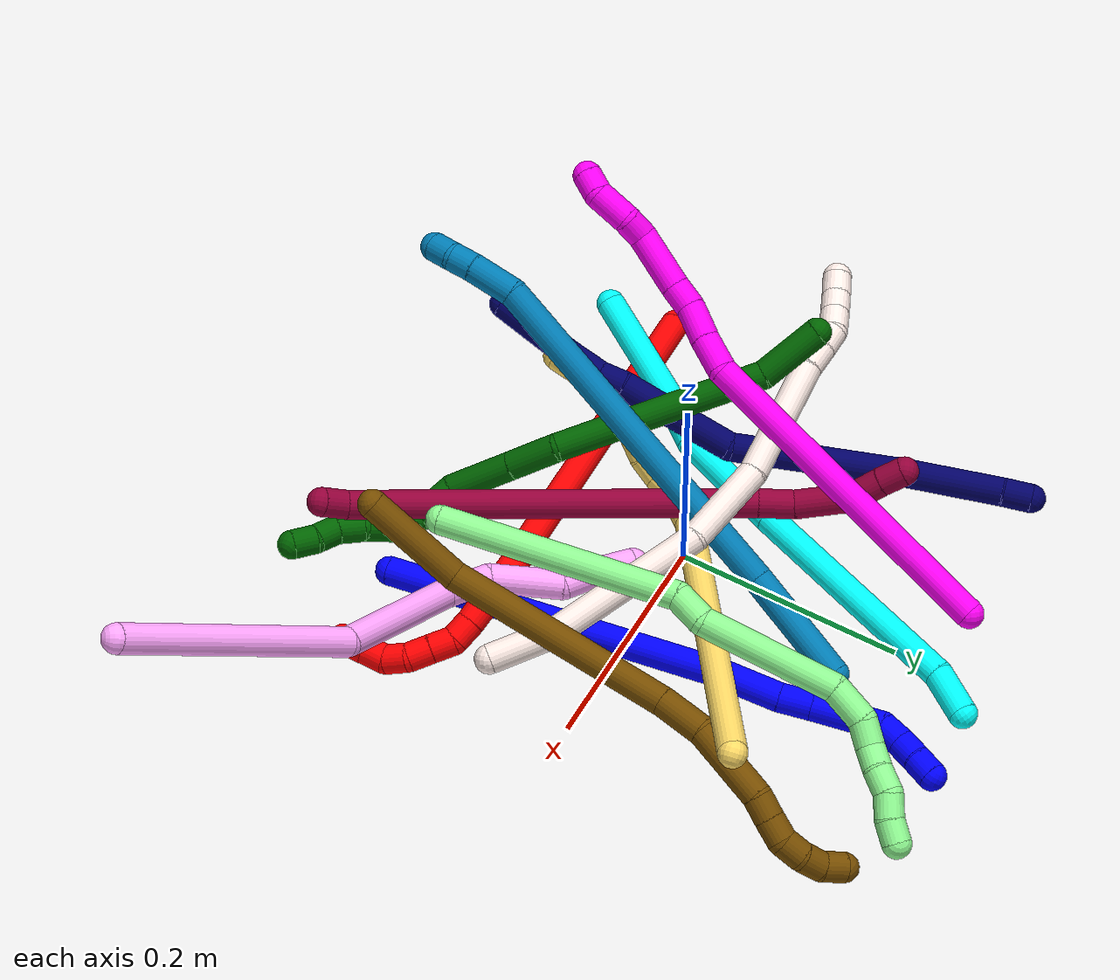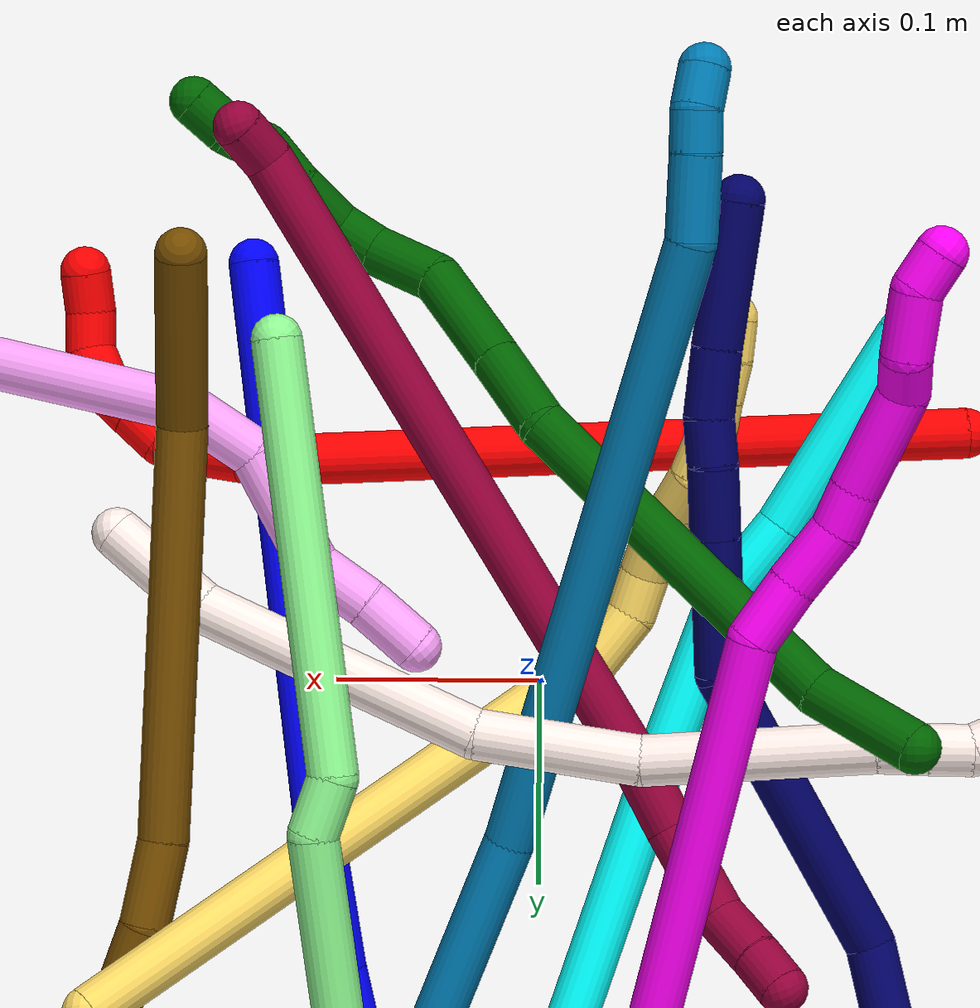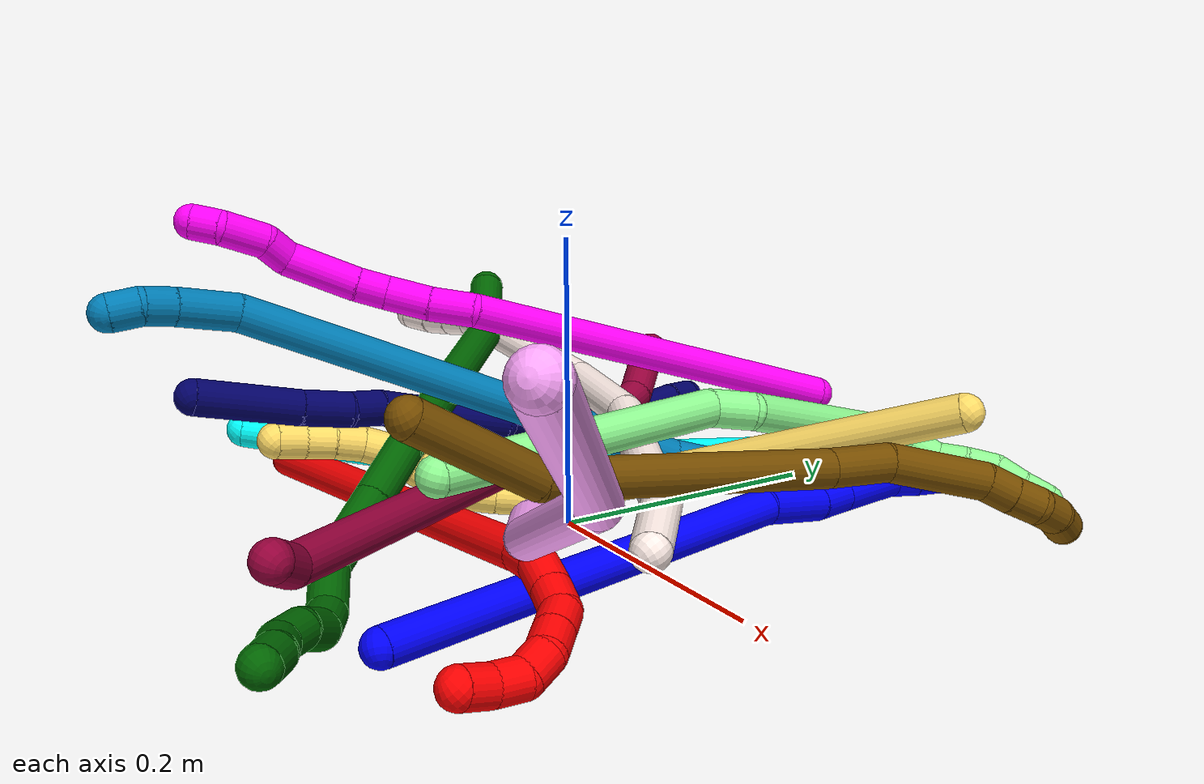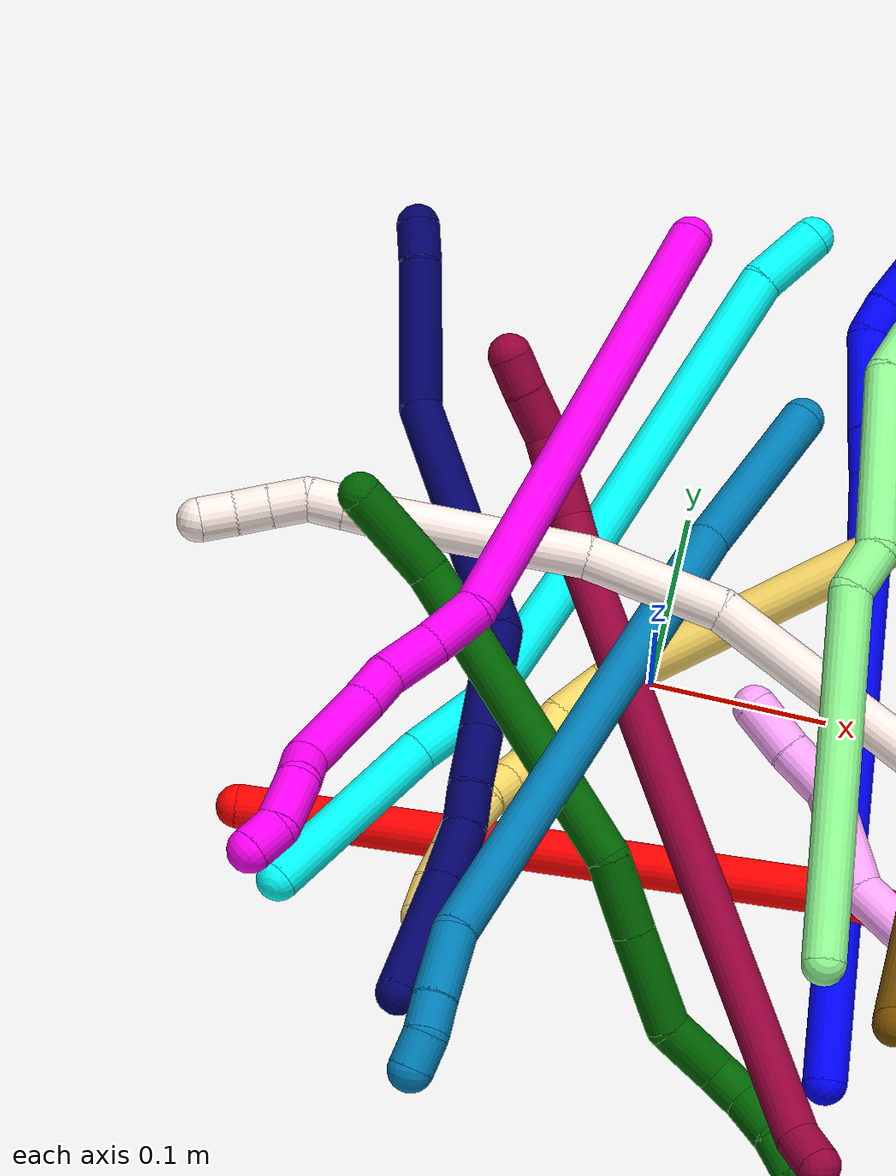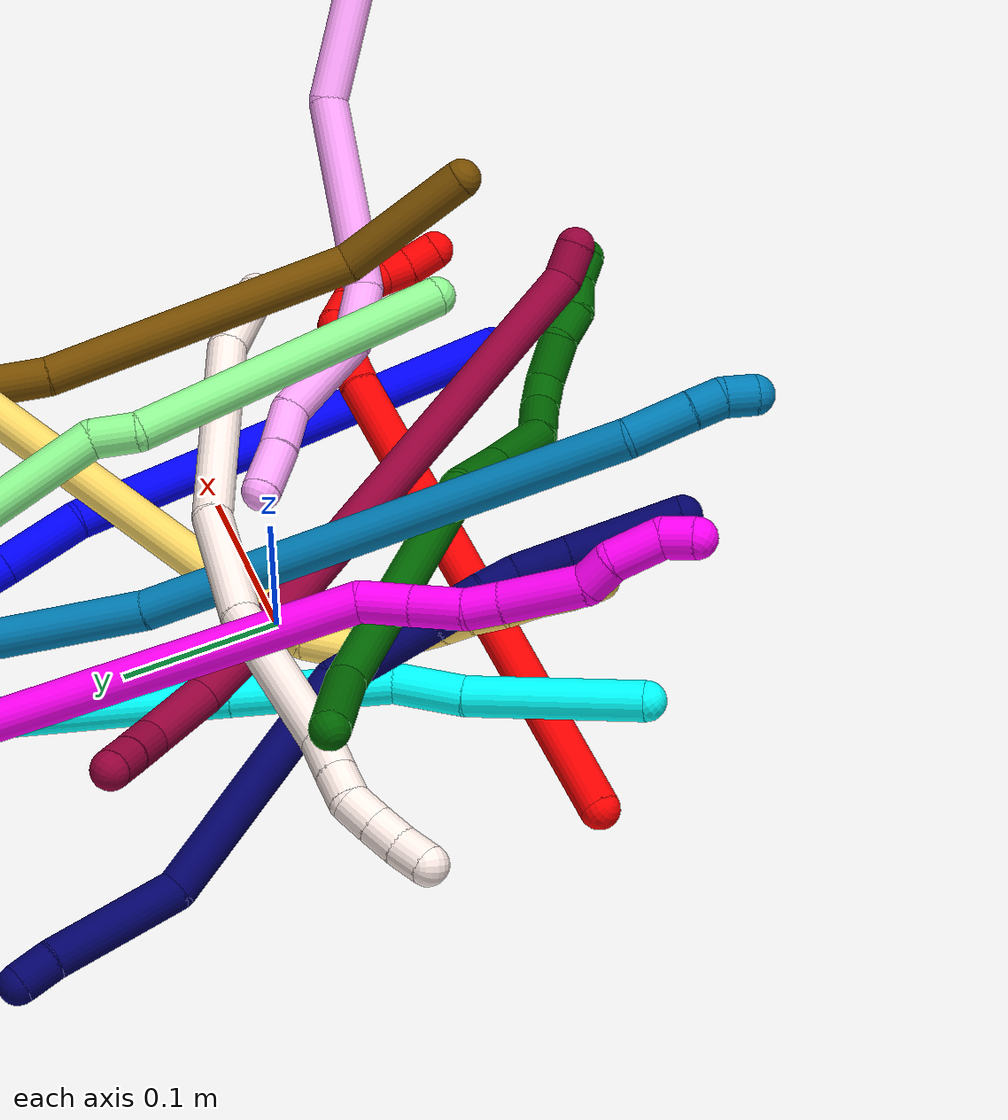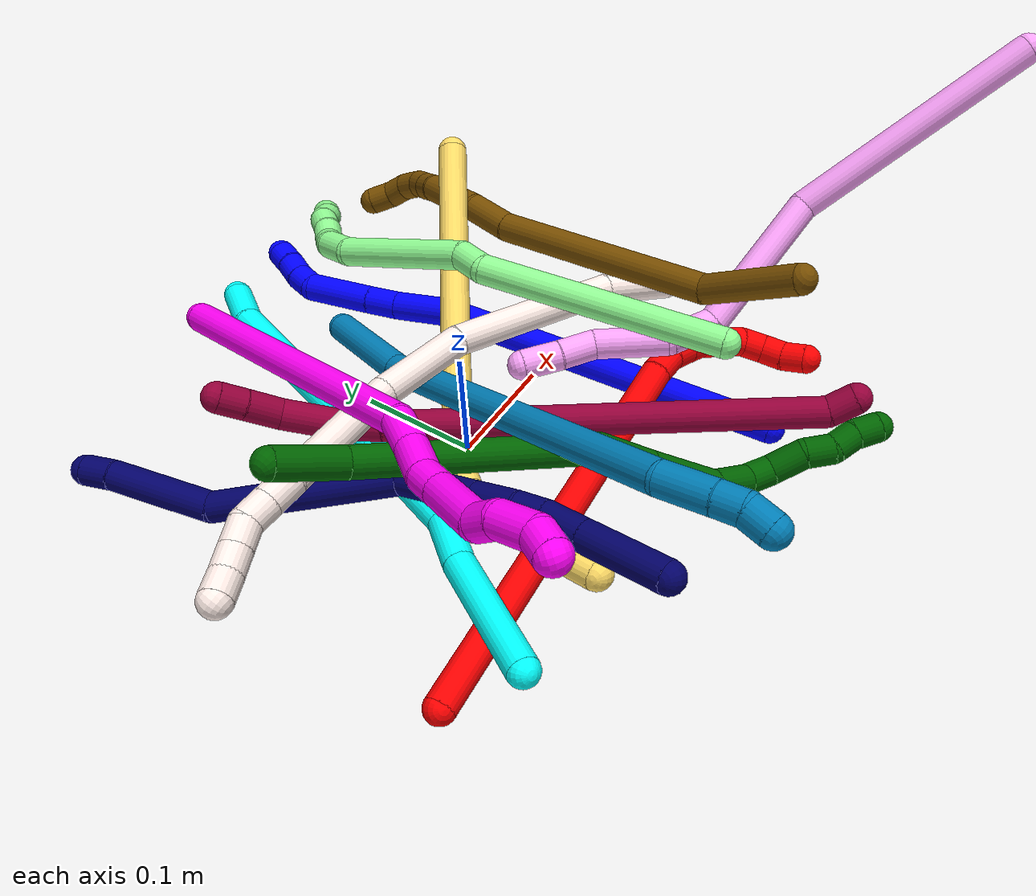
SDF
<sdf version="1.7">
 <world name="default">
  <plugin name="TubeGeneratorPlugin" filename="libtube_generator_plugin.so"/>
  <model name="photoneo_s_sensor">
   <static>1</static>
   <pose>0 0 2 1.57079 1.57079 3.14159</pose>
   <link name="link">
    <inertial><mass>0.1</mass></inertial>
    <sensor name="sensor" type="depth">
     <update_rate>30</update_rate>
     <camera>
      <horizontal_fov>1.22</horizontal_fov>
      <image><width>1920</width><height>1200</height><format>B8G8R8</format></image>
      <clip><near>0.1</near><far>4</far></clip>
      <depth_camera><output>points</output></depth_camera>
     </camera>
     <plugin name="camera_plugin" filename="libgazebo_ros_depth_camera.so">
      <baseline>0.2</baseline>
      <alwaysOn>1</alwaysOn>
      <updateRate>0.0</updateRate>
      <cameraName>camera_ir</cameraName>
      <imageTopicName>/camera/color/image_raw</imageTopicName>
      <cameraInfoTopicName>/camera/color/camera_info</cameraInfoTopicName>
      <depthImageTopicName>/camera/depth/image_raw</depthImageTopicName>
      <depthImageCameraInfoTopicName>/camera/depth/camera_info</depthImageCameraInfoTopicName>
      <pointCloudTopicName>/camera/depth/points</pointCloudTopicName>
      <frameName>fr_optical</frameName>
      <pointCloudCutoff>0.1</pointCloudCutoff>
      <pointCloudCutoffMax>2.0</pointCloudCutoffMax>
      <distortionK1>0</distortionK1>
      <distortionK2>0</distortionK2>
      <distortionK3>0</distortionK3>
      <distortionT1>0</distortionT1>
      <distortionT2>0</distortionT2>
      <CxPrime>0</CxPrime>
      <Cx>0</Cx>
      <Cy>0</Cy>
      <focalLength>0</focalLength>
      <hackBaseline>0</hackBaseline>
     </plugin>
    </sensor>
   </link>
  </model>
  <gravity>0 0 -9.8</gravity>
  <magnetic_field>6e-06 2.3e-05 -4.2e-05</magnetic_field>
  <atmosphere type="adiabatic"/>
  <physics name="default_physics" default="0" type="ode">
   <max_step_size>0.003</max_step_size>
   <real_time_factor>1</real_time_factor>
   <real_time_update_rate>1000</real_time_update_rate>
   <max_contacts>10000</max_contacts>
   <ode>
    <solver>
     <type>quick</type>
     <iters>100</iters>
     <sor>1.3</sor>
     <use_dynamic_moi_rescaling>0</use_dynamic_moi_rescaling>
    </solver>
    <constraints>
     <contact_max_correcting_vel>0</contact_max_correcting_vel>
     <contact_surface_layer>0.001</contact_surface_layer>
     <cfm>0</cfm>
     <erp>0.2</erp>
    </constraints>
   </ode>
  </physics>
  <scene><ambient>0.4 0.4 0.4 1</ambient><background>0.7 0.7 0.7 1</background><shadows>0</shadows></scene>
  <audio><device>default</device></audio>
  <spherical_coordinates>
   <surface_model>EARTH_WGS84</surface_model>
   <latitude_deg>0</latitude_deg>
   <longitude_deg>0</longitude_deg>
   <elevation>0</elevation>
   <heading_deg>0</heading_deg>
  </spherical_coordinates>
  <model name="bin">
   <static>1</static>
   <link name="bottom">
    <collision name="collision-bottom">
     <pose>0 0 -0.01 0 -0 0</pose>
     <geometry><box><size>0.8 0.6 0.02</size></box></geometry>
     <surface>
      <friction><ode><mu>100</mu><mu2>100</mu2></ode></friction>
      <contact><collide_bitmask>65535</collide_bitmask></contact>
     </surface>
    </collision>
   </link>
   <link name="west_wall">
    <collision name="collision-west_wall">
     <pose>-0.41 0 0.1 0 -0 0</pose>
     <geometry><box><size>0.02 0.6 0.2</size></box></geometry>
     <surface>
      <friction><ode><mu>100</mu><mu2>100</mu2></ode></friction>
      <contact><collide_bitmask>65535</collide_bitmask></contact>
     </surface>
    </collision>
   </link>
   <link name="east_wall">
    <collision name="collision-east_wall">
     <pose>0.41 0 0.1 0 -0 0</pose>
     <geometry><box><size>0.02 0.6 0.2</size></box></geometry>
     <surface>
      <friction><ode><mu>100</mu><mu2>100</mu2></ode></friction>
      <contact><collide_bitmask>65535</collide_bitmask></contact>
     </surface>
    </collision>
   </link>
   <link name="south_wall">
    <collision name="collision-south_wall">
     <pose>0 -0.31 0.1 0 -0 0</pose>
     <geometry><box><size>0.8 0.02 0.2</size></box></geometry>
     <surface>
      <friction><ode><mu>100</mu><mu2>100</mu2></ode></friction>
      <contact><collide_bitmask>65535</collide_bitmask></contact>
     </surface>
    </collision>
   </link>
   <link name="north_wall">
    <collision name="collision-north_wall">
     <pose>0 0.31 0.1 0 -0 0</pose>
     <geometry><box><size>0.8 0.02 0.2</size></box></geometry>
     <surface>
      <friction><ode><mu>100</mu><mu2>100</mu2></ode></friction>
      <contact><collide_bitmask>65535</collide_bitmask></contact>
     </surface>
    </collision>
   </link>
  </model>
  <model name="1">
   <static>0</static>
   <link name="1">
    <collision name="collision-cylinder-e_1_1_4">
     <pose>-0.010685 0.138524 0.053815 -1.20025 -0.071778 0.049131</pose>
     <geometry><cylinder><radius>0.0125</radius><length>0.297988</length></cylinder></geometry>
     <surface>
      <friction><ode><mu>1.16</mu><mu2>1.16</mu2><slip1>0</slip1><slip2>0</slip2></ode></friction>
      <contact><ode><kp>1e+06</kp><kd>1</kd><max_vel>0</max_vel><min_depth>0.001</min_depth></ode></contact>
     </surface>
    </collision>
    <visual name="visual-cylinder-e_1_1_4">
     <pose>-0.010685 0.138524 0.053815 -1.20025 -0.071778 0.049131</pose>
     <geometry><cylinder><radius>0.0125</radius><length>0.297988</length></cylinder></geometry>
     <material><ambient>0 0 1 1</ambient></material>
    </visual>
    <collision name="collision-cylinder-e_2_4_5">
     <pose>-0.028234 0.302096 0.113289 -1.34861 -0.261158 0.209169</pose>
     <geometry><cylinder><radius>0.0125</radius><length>0.053158</length></cylinder></geometry>
     <surface>
      <friction><ode><mu>1.16</mu><mu2>1.16</mu2><slip1>0</slip1><slip2>0</slip2></ode></friction>
      <contact><ode><kp>1e+06</kp><kd>1</kd><max_vel>0</max_vel><min_depth>0.001</min_depth></ode></contact>
     </surface>
    </collision>
    <visual name="visual-cylinder-e_2_4_5">
     <pose>-0.028234 0.302096 0.113289 -1.34861 -0.261158 0.209169</pose>
     <geometry><cylinder><radius>0.0125</radius><length>0.053158</length></cylinder></geometry>
     <material><ambient>0 0 1 1</ambient></material>
    </visual>
    <collision name="collision-cylinder-e_3_5_6">
     <pose>-0.038031 0.339903 0.123998 -1.19392 -0.210681 0.143481</pose>
     <geometry><cylinder><radius>0.0125</radius><length>0.028069</length></cylinder></geometry>
     <surface>
      <friction><ode><mu>1.16</mu><mu2>1.16</mu2><slip1>0</slip1><slip2>0</slip2></ode></friction>
      <contact><ode><kp>1e+06</kp><kd>1</kd><max_vel>0</max_vel><min_depth>0.001</min_depth></ode></contact>
     </surface>
    </collision>
    <visual name="visual-cylinder-e_3_5_6">
     <pose>-0.038031 0.339903 0.123998 -1.19392 -0.210681 0.143481</pose>
     <geometry><cylinder><radius>0.0125</radius><length>0.028069</length></cylinder></geometry>
     <material><ambient>0 0 1 1</ambient></material>
    </visual>
    <collision name="collision-cylinder-e_4_6_7">
     <pose>-0.046683 0.380058 0.13945 -1.20792 -0.192671 0.133153</pose>
     <geometry><cylinder><radius>0.0125</radius><length>0.059708</length></cylinder></geometry>
     <surface>
      <friction><ode><mu>1.16</mu><mu2>1.16</mu2><slip1>0</slip1><slip2>0</slip2></ode></friction>
      <contact><ode><kp>1e+06</kp><kd>1</kd><max_vel>0</max_vel><min_depth>0.001</min_depth></ode></contact>
     </surface>
    </collision>
    <visual name="visual-cylinder-e_4_6_7">
     <pose>-0.046683 0.380058 0.13945 -1.20792 -0.192671 0.133153</pose>
     <geometry><cylinder><radius>0.0125</radius><length>0.059708</length></cylinder></geometry>
     <material><ambient>0 0 1 1</ambient></material>
    </visual>
    <collision name="collision-cylinder-e_5_7_8">
     <pose>-0.050781 0.417862 0.149858 -1.57014 0.154168 -0.154067</pose>
     <geometry><cylinder><radius>0.0125</radius><length>0.02107</length></cylinder></geometry>
     <surface>
      <friction><ode><mu>1.16</mu><mu2>1.16</mu2><slip1>0</slip1><slip2>0</slip2></ode></friction>
      <contact><ode><kp>1e+06</kp><kd>1</kd><max_vel>0</max_vel><min_depth>0.001</min_depth></ode></contact>
     </surface>
    </collision>
    <visual name="visual-cylinder-e_5_7_8">
     <pose>-0.050781 0.417862 0.149858 -1.57014 0.154168 -0.154067</pose>
     <geometry><cylinder><radius>0.0125</radius><length>0.02107</length></cylinder></geometry>
     <material><ambient>0 0 1 1</ambient></material>
    </visual>
    <collision name="collision-cylinder-e_6_8_9">
     <pose>-0.04566 0.437638 0.149803 -1.57741 0.357938 -0.360262</pose>
     <geometry><cylinder><radius>0.0125</radius><length>0.020001</length></cylinder></geometry>
     <surface>
      <friction><ode><mu>1.16</mu><mu2>1.16</mu2><slip1>0</slip1><slip2>0</slip2></ode></friction>
      <contact><ode><kp>1e+06</kp><kd>1</kd><max_vel>0</max_vel><min_depth>0.001</min_depth></ode></contact>
     </surface>
    </collision>
    <visual name="visual-cylinder-e_6_8_9">
     <pose>-0.04566 0.437638 0.149803 -1.57741 0.357938 -0.360262</pose>
     <geometry><cylinder><radius>0.0125</radius><length>0.020001</length></cylinder></geometry>
     <material><ambient>0 0 1 1</ambient></material>
    </visual>
    <collision name="collision-cylinder-e_7_9_2">
     <pose>-0.039673 0.456669 0.149053 -1.64185 0.250917 -0.269196</pose>
     <geometry><cylinder><radius>0.0125</radius><length>0.020005</length></cylinder></geometry>
     <surface>
      <friction><ode><mu>1.16</mu><mu2>1.16</mu2><slip1>0</slip1><slip2>0</slip2></ode></friction>
      <contact><ode><kp>1e+06</kp><kd>1</kd><max_vel>0</max_vel><min_depth>0.001</min_depth></ode></contact>
     </surface>
    </collision>
    <visual name="visual-cylinder-e_7_9_2">
     <pose>-0.039673 0.456669 0.149053 -1.64185 0.250917 -0.269196</pose>
     <geometry><cylinder><radius>0.0125</radius><length>0.020005</length></cylinder></geometry>
     <material><ambient>0 0 1 1</ambient></material>
    </visual>
    <collision name="collision-sphere-2">
     <pose>-0.037189 0.466334 0.148365 0 -0 0</pose>
     <geometry><sphere><radius>0.0125</radius></sphere></geometry>
     <surface>
      <friction><ode><mu>1.16</mu><mu2>1.16</mu2><slip1>0</slip1><slip2>0</slip2></ode></friction>
      <contact><ode><kp>1e+06</kp><kd>1</kd><max_vel>0</max_vel><min_depth>0.001</min_depth></ode></contact>
     </surface>
    </collision>
    <visual name="visual-sphere-2">
     <pose>-0.037189 0.466334 0.148365 0 -0 0</pose>
     <geometry><sphere><radius>0.0125</radius></sphere></geometry>
     <material><ambient>0 0 1 1</ambient></material>
    </visual>
    <collision name="collision-sphere-9">
     <pose>-0.042157 0.447004 0.149741 0 -0 0</pose>
     <geometry><sphere><radius>0.0125</radius></sphere></geometry>
     <surface>
      <friction><ode><mu>1.16</mu><mu2>1.16</mu2><slip1>0</slip1><slip2>0</slip2></ode></friction>
      <contact><ode><kp>1e+06</kp><kd>1</kd><max_vel>0</max_vel><min_depth>0.001</min_depth></ode></contact>
     </surface>
    </collision>
    <visual name="visual-sphere-9">
     <pose>-0.042157 0.447004 0.149741 0 -0 0</pose>
     <geometry><sphere><radius>0.0125</radius></sphere></geometry>
     <material><ambient>0 0 1 1</ambient></material>
    </visual>
    <collision name="collision-sphere-4">
     <pose>-0.021371 0.277049 0.107631 0 -0 0</pose>
     <geometry><sphere><radius>0.0125</radius></sphere></geometry>
     <surface>
      <friction><ode><mu>1.16</mu><mu2>1.16</mu2><slip1>0</slip1><slip2>0</slip2></ode></friction>
      <contact><ode><kp>1e+06</kp><kd>1</kd><max_vel>0</max_vel><min_depth>0.001</min_depth></ode></contact>
     </surface>
    </collision>
    <visual name="visual-sphere-4">
     <pose>-0.021371 0.277049 0.107631 0 -0 0</pose>
     <geometry><sphere><radius>0.0125</radius></sphere></geometry>
     <material><ambient>0 0 1 1</ambient></material>
    </visual>
    <collision name="collision-sphere-1">
     <geometry><sphere><radius>0.0125</radius></sphere></geometry>
     <surface>
      <friction><ode><mu>1.16</mu><mu2>1.16</mu2><slip1>0</slip1><slip2>0</slip2></ode></friction>
      <contact><ode><kp>1e+06</kp><kd>1</kd><max_vel>0</max_vel><min_depth>0.001</min_depth></ode></contact>
     </surface>
    </collision>
    <visual name="visual-sphere-1">
     <geometry><sphere><radius>0.0125</radius></sphere></geometry>
     <material><ambient>0 0 1 1</ambient></material>
    </visual>
    <collision name="collision-sphere-8">
     <pose>-0.049164 0.428272 0.149865 0 -0 0</pose>
     <geometry><sphere><radius>0.0125</radius></sphere></geometry>
     <surface>
      <friction><ode><mu>1.16</mu><mu2>1.16</mu2><slip1>0</slip1><slip2>0</slip2></ode></friction>
      <contact><ode><kp>1e+06</kp><kd>1</kd><max_vel>0</max_vel><min_depth>0.001</min_depth></ode></contact>
     </surface>
    </collision>
    <visual name="visual-sphere-8">
     <pose>-0.049164 0.428272 0.149865 0 -0 0</pose>
     <geometry><sphere><radius>0.0125</radius></sphere></geometry>
     <material><ambient>0 0 1 1</ambient></material>
    </visual>
    <collision name="collision-sphere-5">
     <pose>-0.035096 0.327142 0.118947 0 -0 0</pose>
     <geometry><sphere><radius>0.0125</radius></sphere></geometry>
     <surface>
      <friction><ode><mu>1.16</mu><mu2>1.16</mu2><slip1>0</slip1><slip2>0</slip2></ode></friction>
      <contact><ode><kp>1e+06</kp><kd>1</kd><max_vel>0</max_vel><min_depth>0.001</min_depth></ode></contact>
     </surface>
    </collision>
    <visual name="visual-sphere-5">
     <pose>-0.035096 0.327142 0.118947 0 -0 0</pose>
     <geometry><sphere><radius>0.0125</radius></sphere></geometry>
     <material><ambient>0 0 1 1</ambient></material>
    </visual>
    <collision name="collision-sphere-6">
     <pose>-0.040966 0.352664 0.129049 0 -0 0</pose>
     <geometry><sphere><radius>0.0125</radius></sphere></geometry>
     <surface>
      <friction><ode><mu>1.16</mu><mu2>1.16</mu2><slip1>0</slip1><slip2>0</slip2></ode></friction>
      <contact><ode><kp>1e+06</kp><kd>1</kd><max_vel>0</max_vel><min_depth>0.001</min_depth></ode></contact>
     </surface>
    </collision>
    <visual name="visual-sphere-6">
     <pose>-0.040966 0.352664 0.129049 0 -0 0</pose>
     <geometry><sphere><radius>0.0125</radius></sphere></geometry>
     <material><ambient>0 0 1 1</ambient></material>
    </visual>
    <collision name="collision-sphere-7">
     <pose>-0.052399 0.407451 0.149851 0 -0 0</pose>
     <geometry><sphere><radius>0.0125</radius></sphere></geometry>
     <surface>
      <friction><ode><mu>1.16</mu><mu2>1.16</mu2><slip1>0</slip1><slip2>0</slip2></ode></friction>
      <contact><ode><kp>1e+06</kp><kd>1</kd><max_vel>0</max_vel><min_depth>0.001</min_depth></ode></contact>
     </surface>
    </collision>
    <visual name="visual-sphere-7">
     <pose>-0.052399 0.407451 0.149851 0 -0 0</pose>
     <geometry><sphere><radius>0.0125</radius></sphere></geometry>
     <material><ambient>0 0 1 1</ambient></material>
    </visual>
    <inertial>
     <pose>-0.022633 0.232528 0.086002 0 -0 0</pose>
     <mass>0.5</mass>
     <inertia>
      <ixx>0.002359</ixx>
      <ixy>0</ixy>
      <ixz>0</ixz>
      <iyy>0.000972</iyy>
      <iyz>0</iyz>
      <izz>-0.001922</izz>
     </inertia>
    </inertial>
   </link>
   <pose>0.142329 -0.205212 0.011491 -0.236691 -0.744035 -0.017679</pose>
  </model>
  <model name="2">
   <static>0</static>
   <link name="2">
    <collision name="collision-cylinder-e_1_1_4">
     <pose>0.160064 0.027199 -0.039667 -2.54054 1.2789 -2.35192</pose>
     <geometry><cylinder><radius>0.0125</radius><length>0.334267</length></cylinder></geometry>
     <surface>
      <friction><ode><mu>1.16</mu><mu2>1.16</mu2><slip1>0</slip1><slip2>0</slip2></ode></friction>
      <contact><ode><kp>1e+06</kp><kd>1</kd><max_vel>0</max_vel><min_depth>0.001</min_depth></ode></contact>
     </surface>
    </collision>
    <visual name="visual-cylinder-e_1_1_4">
     <pose>0.160064 0.027199 -0.039667 -2.54054 1.2789 -2.35192</pose>
     <geometry><cylinder><radius>0.0125</radius><length>0.334267</length></cylinder></geometry>
     <material><ambient>1 0 0 1</ambient></material>
    </visual>
    <collision name="collision-cylinder-e_2_4_5">
     <pose>0.330928 0.054907 -0.081994 -2.95249 1.32513 -2.89969</pose>
     <geometry><cylinder><radius>0.0125</radius><length>0.022271</length></cylinder></geometry>
     <surface>
      <friction><ode><mu>1.16</mu><mu2>1.16</mu2><slip1>0</slip1><slip2>0</slip2></ode></friction>
      <contact><ode><kp>1e+06</kp><kd>1</kd><max_vel>0</max_vel><min_depth>0.001</min_depth></ode></contact>
     </surface>
    </collision>
    <visual name="visual-cylinder-e_2_4_5">
     <pose>0.330928 0.054907 -0.081994 -2.95249 1.32513 -2.89969</pose>
     <geometry><cylinder><radius>0.0125</radius><length>0.022271</length></cylinder></geometry>
     <material><ambient>1 0 0 1</ambient></material>
    </visual>
    <collision name="collision-cylinder-e_3_5_6">
     <pose>0.351776 0.052471 -0.089406 2.58684 1.06302 2.23964</pose>
     <geometry><cylinder><radius>0.0125</radius><length>0.022994</length></cylinder></geometry>
     <surface>
      <friction><ode><mu>1.16</mu><mu2>1.16</mu2><slip1>0</slip1><slip2>0</slip2></ode></friction>
      <contact><ode><kp>1e+06</kp><kd>1</kd><max_vel>0</max_vel><min_depth>0.001</min_depth></ode></contact>
     </surface>
    </collision>
    <visual name="visual-cylinder-e_3_5_6">
     <pose>0.351776 0.052471 -0.089406 2.58684 1.06302 2.23964</pose>
     <geometry><cylinder><radius>0.0125</radius><length>0.022994</length></cylinder></geometry>
     <material><ambient>1 0 0 1</ambient></material>
    </visual>
    <collision name="collision-cylinder-e_4_6_7">
     <pose>0.370817 0.046605 -0.097511 2.42489 1.11162 2.05639</pose>
     <geometry><cylinder><radius>0.0125</radius><length>0.020069</length></cylinder></geometry>
     <surface>
      <friction><ode><mu>1.16</mu><mu2>1.16</mu2><slip1>0</slip1><slip2>0</slip2></ode></friction>
      <contact><ode><kp>1e+06</kp><kd>1</kd><max_vel>0</max_vel><min_depth>0.001</min_depth></ode></contact>
     </surface>
    </collision>
    <visual name="visual-cylinder-e_4_6_7">
     <pose>0.370817 0.046605 -0.097511 2.42489 1.11162 2.05639</pose>
     <geometry><cylinder><radius>0.0125</radius><length>0.020069</length></cylinder></geometry>
     <material><ambient>1 0 0 1</ambient></material>
    </visual>
    <collision name="collision-cylinder-e_5_7_8">
     <pose>0.388065 0.037784 -0.100328 1.48013 0.948215 0.876437</pose>
     <geometry><cylinder><radius>0.0125</radius><length>0.020316</length></cylinder></geometry>
     <surface>
      <friction><ode><mu>1.16</mu><mu2>1.16</mu2><slip1>0</slip1><slip2>0</slip2></ode></friction>
      <contact><ode><kp>1e+06</kp><kd>1</kd><max_vel>0</max_vel><min_depth>0.001</min_depth></ode></contact>
     </surface>
    </collision>
    <visual name="visual-cylinder-e_5_7_8">
     <pose>0.388065 0.037784 -0.100328 1.48013 0.948215 0.876437</pose>
     <geometry><cylinder><radius>0.0125</radius><length>0.020316</length></cylinder></geometry>
     <material><ambient>1 0 0 1</ambient></material>
    </visual>
    <collision name="collision-cylinder-e_6_8_9">
     <pose>0.404332 0.025901 -0.099403 1.50596 0.928423 0.87749</pose>
     <geometry><cylinder><radius>0.0125</radius><length>0.020021</length></cylinder></geometry>
     <surface>
      <friction><ode><mu>1.16</mu><mu2>1.16</mu2><slip1>0</slip1><slip2>0</slip2></ode></friction>
      <contact><ode><kp>1e+06</kp><kd>1</kd><max_vel>0</max_vel><min_depth>0.001</min_depth></ode></contact>
     </surface>
    </collision>
    <visual name="visual-cylinder-e_6_8_9">
     <pose>0.404332 0.025901 -0.099403 1.50596 0.928423 0.87749</pose>
     <geometry><cylinder><radius>0.0125</radius><length>0.020021</length></cylinder></geometry>
     <material><ambient>1 0 0 1</ambient></material>
    </visual>
    <collision name="collision-cylinder-e_7_9_10">
     <pose>0.417463 0.011496 -0.097259 1.36526 0.536609 0.439823</pose>
     <geometry><cylinder><radius>0.0125</radius><length>0.020015</length></cylinder></geometry>
     <surface>
      <friction><ode><mu>1.16</mu><mu2>1.16</mu2><slip1>0</slip1><slip2>0</slip2></ode></friction>
      <contact><ode><kp>1e+06</kp><kd>1</kd><max_vel>0</max_vel><min_depth>0.001</min_depth></ode></contact>
     </surface>
    </collision>
    <visual name="visual-cylinder-e_7_9_10">
     <pose>0.417463 0.011496 -0.097259 1.36526 0.536609 0.439823</pose>
     <geometry><cylinder><radius>0.0125</radius><length>0.020015</length></cylinder></geometry>
     <material><ambient>1 0 0 1</ambient></material>
    </visual>
    <collision name="collision-cylinder-e_8_10_11">
     <pose>0.425026 -0.00452 -0.089448 0.897745 0.246744 0.119313</pose>
     <geometry><cylinder><radius>0.0125</radius><length>0.020035</length></cylinder></geometry>
     <surface>
      <friction><ode><mu>1.16</mu><mu2>1.16</mu2><slip1>0</slip1><slip2>0</slip2></ode></friction>
      <contact><ode><kp>1e+06</kp><kd>1</kd><max_vel>0</max_vel><min_depth>0.001</min_depth></ode></contact>
     </surface>
    </collision>
    <visual name="visual-cylinder-e_8_10_11">
     <pose>0.425026 -0.00452 -0.089448 0.897745 0.246744 0.119313</pose>
     <geometry><cylinder><radius>0.0125</radius><length>0.020035</length></cylinder></geometry>
     <material><ambient>1 0 0 1</ambient></material>
    </visual>
    <collision name="collision-cylinder-e_9_11_2">
     <pose>0.431206 -0.018155 -0.076342 0.708285 0.382293 0.142849</pose>
     <geometry><cylinder><radius>0.0125</radius><length>0.020011</length></cylinder></geometry>
     <surface>
      <friction><ode><mu>1.16</mu><mu2>1.16</mu2><slip1>0</slip1><slip2>0</slip2></ode></friction>
      <contact><ode><kp>1e+06</kp><kd>1</kd><max_vel>0</max_vel><min_depth>0.001</min_depth></ode></contact>
     </surface>
    </collision>
    <visual name="visual-cylinder-e_9_11_2">
     <pose>0.431206 -0.018155 -0.076342 0.708285 0.382293 0.142849</pose>
     <geometry><cylinder><radius>0.0125</radius><length>0.020011</length></cylinder></geometry>
     <material><ambient>1 0 0 1</ambient></material>
    </visual>
    <collision name="collision-sphere-2">
     <pose>0.434938 -0.024194 -0.069291 0 -0 0</pose>
     <geometry><sphere><radius>0.0125</radius></sphere></geometry>
     <surface>
      <friction><ode><mu>1.16</mu><mu2>1.16</mu2><slip1>0</slip1><slip2>0</slip2></ode></friction>
      <contact><ode><kp>1e+06</kp><kd>1</kd><max_vel>0</max_vel><min_depth>0.001</min_depth></ode></contact>
     </surface>
    </collision>
    <visual name="visual-sphere-2">
     <pose>0.434938 -0.024194 -0.069291 0 -0 0</pose>
     <geometry><sphere><radius>0.0125</radius></sphere></geometry>
     <material><ambient>1 0 0 1</ambient></material>
    </visual>
    <collision name="collision-sphere-11">
     <pose>0.427473 -0.012116 -0.083392 0 -0 0</pose>
     <geometry><sphere><radius>0.0125</radius></sphere></geometry>
     <surface>
      <friction><ode><mu>1.16</mu><mu2>1.16</mu2><slip1>0</slip1><slip2>0</slip2></ode></friction>
      <contact><ode><kp>1e+06</kp><kd>1</kd><max_vel>0</max_vel><min_depth>0.001</min_depth></ode></contact>
     </surface>
    </collision>
    <visual name="visual-sphere-11">
     <pose>0.427473 -0.012116 -0.083392 0 -0 0</pose>
     <geometry><sphere><radius>0.0125</radius></sphere></geometry>
     <material><ambient>1 0 0 1</ambient></material>
    </visual>
    <collision name="collision-sphere-10">
     <pose>0.422579 0.003076 -0.095504 0 -0 0</pose>
     <geometry><sphere><radius>0.0125</radius></sphere></geometry>
     <surface>
      <friction><ode><mu>1.16</mu><mu2>1.16</mu2><slip1>0</slip1><slip2>0</slip2></ode></friction>
      <contact><ode><kp>1e+06</kp><kd>1</kd><max_vel>0</max_vel><min_depth>0.001</min_depth></ode></contact>
     </surface>
    </collision>
    <visual name="visual-sphere-10">
     <pose>0.422579 0.003076 -0.095504 0 -0 0</pose>
     <geometry><sphere><radius>0.0125</radius></sphere></geometry>
     <material><ambient>1 0 0 1</ambient></material>
    </visual>
    <collision name="collision-sphere-9">
     <pose>0.412347 0.019916 -0.099014 0 -0 0</pose>
     <geometry><sphere><radius>0.0125</radius></sphere></geometry>
     <surface>
      <friction><ode><mu>1.16</mu><mu2>1.16</mu2><slip1>0</slip1><slip2>0</slip2></ode></friction>
      <contact><ode><kp>1e+06</kp><kd>1</kd><max_vel>0</max_vel><min_depth>0.001</min_depth></ode></contact>
     </surface>
    </collision>
    <visual name="visual-sphere-9">
     <pose>0.412347 0.019916 -0.099014 0 -0 0</pose>
     <geometry><sphere><radius>0.0125</radius></sphere></geometry>
     <material><ambient>1 0 0 1</ambient></material>
    </visual>
    <collision name="collision-sphere-4">
     <pose>0.320127 0.054398 -0.079334 0 -0 0</pose>
     <geometry><sphere><radius>0.0125</radius></sphere></geometry>
     <surface>
      <friction><ode><mu>1.16</mu><mu2>1.16</mu2><slip1>0</slip1><slip2>0</slip2></ode></friction>
      <contact><ode><kp>1e+06</kp><kd>1</kd><max_vel>0</max_vel><min_depth>0.001</min_depth></ode></contact>
     </surface>
    </collision>
    <visual name="visual-sphere-4">
     <pose>0.320127 0.054398 -0.079334 0 -0 0</pose>
     <geometry><sphere><radius>0.0125</radius></sphere></geometry>
     <material><ambient>1 0 0 1</ambient></material>
    </visual>
    <collision name="collision-sphere-1">
     <geometry><sphere><radius>0.0125</radius></sphere></geometry>
     <surface>
      <friction><ode><mu>1.16</mu><mu2>1.16</mu2><slip1>0</slip1><slip2>0</slip2></ode></friction>
      <contact><ode><kp>1e+06</kp><kd>1</kd><max_vel>0</max_vel><min_depth>0.001</min_depth></ode></contact>
     </surface>
    </collision>
    <visual name="visual-sphere-1">
     <geometry><sphere><radius>0.0125</radius></sphere></geometry>
     <material><ambient>1 0 0 1</ambient></material>
    </visual>
    <collision name="collision-sphere-8">
     <pose>0.396317 0.031885 -0.099791 0 -0 0</pose>
     <geometry><sphere><radius>0.0125</radius></sphere></geometry>
     <surface>
      <friction><ode><mu>1.16</mu><mu2>1.16</mu2><slip1>0</slip1><slip2>0</slip2></ode></friction>
      <contact><ode><kp>1e+06</kp><kd>1</kd><max_vel>0</max_vel><min_depth>0.001</min_depth></ode></contact>
     </surface>
    </collision>
    <visual name="visual-sphere-8">
     <pose>0.396317 0.031885 -0.099791 0 -0 0</pose>
     <geometry><sphere><radius>0.0125</radius></sphere></geometry>
     <material><ambient>1 0 0 1</ambient></material>
    </visual>
    <collision name="collision-sphere-5">
     <pose>0.34173 0.055416 -0.084654 0 -0 0</pose>
     <geometry><sphere><radius>0.0125</radius></sphere></geometry>
     <surface>
      <friction><ode><mu>1.16</mu><mu2>1.16</mu2><slip1>0</slip1><slip2>0</slip2></ode></friction>
      <contact><ode><kp>1e+06</kp><kd>1</kd><max_vel>0</max_vel><min_depth>0.001</min_depth></ode></contact>
     </surface>
    </collision>
    <visual name="visual-sphere-5">
     <pose>0.34173 0.055416 -0.084654 0 -0 0</pose>
     <geometry><sphere><radius>0.0125</radius></sphere></geometry>
     <material><ambient>1 0 0 1</ambient></material>
    </visual>
    <collision name="collision-sphere-6">
     <pose>0.361822 0.049527 -0.094158 0 -0 0</pose>
     <geometry><sphere><radius>0.0125</radius></sphere></geometry>
     <surface>
      <friction><ode><mu>1.16</mu><mu2>1.16</mu2><slip1>0</slip1><slip2>0</slip2></ode></friction>
      <contact><ode><kp>1e+06</kp><kd>1</kd><max_vel>0</max_vel><min_depth>0.001</min_depth></ode></contact>
     </surface>
    </collision>
    <visual name="visual-sphere-6">
     <pose>0.361822 0.049527 -0.094158 0 -0 0</pose>
     <geometry><sphere><radius>0.0125</radius></sphere></geometry>
     <material><ambient>1 0 0 1</ambient></material>
    </visual>
    <collision name="collision-sphere-7">
     <pose>0.379813 0.043684 -0.100864 0 -0 0</pose>
     <geometry><sphere><radius>0.0125</radius></sphere></geometry>
     <surface>
      <friction><ode><mu>1.16</mu><mu2>1.16</mu2><slip1>0</slip1><slip2>0</slip2></ode></friction>
      <contact><ode><kp>1e+06</kp><kd>1</kd><max_vel>0</max_vel><min_depth>0.001</min_depth></ode></contact>
     </surface>
    </collision>
    <visual name="visual-sphere-7">
     <pose>0.379813 0.043684 -0.100864 0 -0 0</pose>
     <geometry><sphere><radius>0.0125</radius></sphere></geometry>
     <material><ambient>1 0 0 1</ambient></material>
    </visual>
    <inertial>
     <pose>0.235768 0.027037 -0.056786 0 -0 0</pose>
     <mass>0.5</mass>
     <inertia>
      <ixx>-0.001231</ixx>
      <ixy>0</ixy>
      <ixz>0</ixz>
      <iyy>0.002389</iyy>
      <iyz>0</iyz>
      <izz>-0.00351</izz>
     </inertia>
    </inertial>
   </link>
   <pose>-0.209514 -0.123667 0.011495 0.675122 -0.1768 -0.228906</pose>
  </model>
  <model name="3">
   <static>0</static>
   <link name="3">
    <collision name="collision-cylinder-e_1_1_4">
     <pose>0.001281 0.025394 0.048931 -0.478716 0.023225 -0.005668</pose>
     <geometry><cylinder><radius>0.0125</radius><length>0.110286</length></cylinder></geometry>
     <surface>
      <friction><ode><mu>1.16</mu><mu2>1.16</mu2><slip1>0</slip1><slip2>0</slip2></ode></friction>
      <contact><ode><kp>1e+06</kp><kd>1</kd><max_vel>0</max_vel><min_depth>0.001</min_depth></ode></contact>
     </surface>
    </collision>
    <visual name="visual-cylinder-e_1_1_4">
     <pose>0.001281 0.025394 0.048931 -0.478716 0.023225 -0.005668</pose>
     <geometry><cylinder><radius>0.0125</radius><length>0.110286</length></cylinder></geometry>
     <material><ambient>0.003922 1 0.996078 1</ambient></material>
    </visual>
    <collision name="collision-cylinder-e_2_4_5">
     <pose>0.001535 0.063502 0.115909 -0.613726 -0.046438 0.014717</pose>
     <geometry><cylinder><radius>0.0125</radius><length>0.044199</length></cylinder></geometry>
     <surface>
      <friction><ode><mu>1.16</mu><mu2>1.16</mu2><slip1>0</slip1><slip2>0</slip2></ode></friction>
      <contact><ode><kp>1e+06</kp><kd>1</kd><max_vel>0</max_vel><min_depth>0.001</min_depth></ode></contact>
     </surface>
    </collision>
    <visual name="visual-cylinder-e_2_4_5">
     <pose>0.001535 0.063502 0.115909 -0.613726 -0.046438 0.014717</pose>
     <geometry><cylinder><radius>0.0125</radius><length>0.044199</length></cylinder></geometry>
     <material><ambient>0.003922 1 0.996078 1</ambient></material>
    </visual>
    <collision name="collision-cylinder-e_3_5_6">
     <pose>0.012571 0.097714 0.177426 -0.459284 0.243779 -0.057255</pose>
     <geometry><cylinder><radius>0.0125</radius><length>0.099946</length></cylinder></geometry>
     <surface>
      <friction><ode><mu>1.16</mu><mu2>1.16</mu2><slip1>0</slip1><slip2>0</slip2></ode></friction>
      <contact><ode><kp>1e+06</kp><kd>1</kd><max_vel>0</max_vel><min_depth>0.001</min_depth></ode></contact>
     </surface>
    </collision>
    <visual name="visual-cylinder-e_3_5_6">
     <pose>0.012571 0.097714 0.177426 -0.459284 0.243779 -0.057255</pose>
     <geometry><cylinder><radius>0.0125</radius><length>0.099946</length></cylinder></geometry>
     <material><ambient>0.003922 1 0.996078 1</ambient></material>
    </visual>
    <collision name="collision-cylinder-e_4_6_7">
     <pose>0.052576 0.163453 0.308596 -0.467201 0.277147 -0.066347</pose>
     <geometry><cylinder><radius>0.0125</radius><length>0.204247</length></cylinder></geometry>
     <surface>
      <friction><ode><mu>1.16</mu><mu2>1.16</mu2><slip1>0</slip1><slip2>0</slip2></ode></friction>
      <contact><ode><kp>1e+06</kp><kd>1</kd><max_vel>0</max_vel><min_depth>0.001</min_depth></ode></contact>
     </surface>
    </collision>
    <visual name="visual-cylinder-e_4_6_7">
     <pose>0.052576 0.163453 0.308596 -0.467201 0.277147 -0.066347</pose>
     <geometry><cylinder><radius>0.0125</radius><length>0.204247</length></cylinder></geometry>
     <material><ambient>0.003922 1 0.996078 1</ambient></material>
    </visual>
    <collision name="collision-cylinder-e_5_7_2">
     <pose>0.081054 0.218838 0.413684 -0.569989 0.025924 -0.007595</pose>
     <geometry><cylinder><radius>0.0125</radius><length>0.041321</length></cylinder></geometry>
     <surface>
      <friction><ode><mu>1.16</mu><mu2>1.16</mu2><slip1>0</slip1><slip2>0</slip2></ode></friction>
      <contact><ode><kp>1e+06</kp><kd>1</kd><max_vel>0</max_vel><min_depth>0.001</min_depth></ode></contact>
     </surface>
    </collision>
    <visual name="visual-cylinder-e_5_7_2">
     <pose>0.081054 0.218838 0.413684 -0.569989 0.025924 -0.007595</pose>
     <geometry><cylinder><radius>0.0125</radius><length>0.041321</length></cylinder></geometry>
     <material><ambient>0.003922 1 0.996078 1</ambient></material>
    </visual>
    <collision name="collision-sphere-2">
     <pose>0.081589 0.229984 0.431073 0 -0 0</pose>
     <geometry><sphere><radius>0.0125</radius></sphere></geometry>
     <surface>
      <friction><ode><mu>1.16</mu><mu2>1.16</mu2><slip1>0</slip1><slip2>0</slip2></ode></friction>
      <contact><ode><kp>1e+06</kp><kd>1</kd><max_vel>0</max_vel><min_depth>0.001</min_depth></ode></contact>
     </surface>
    </collision>
    <visual name="visual-sphere-2">
     <pose>0.081589 0.229984 0.431073 0 -0 0</pose>
     <geometry><sphere><radius>0.0125</radius></sphere></geometry>
     <material><ambient>0.003922 1 0.996078 1</ambient></material>
    </visual>
    <collision name="collision-sphere-7">
     <pose>0.080518 0.207693 0.396296 0 -0 0</pose>
     <geometry><sphere><radius>0.0125</radius></sphere></geometry>
     <surface>
      <friction><ode><mu>1.16</mu><mu2>1.16</mu2><slip1>0</slip1><slip2>0</slip2></ode></friction>
      <contact><ode><kp>1e+06</kp><kd>1</kd><max_vel>0</max_vel><min_depth>0.001</min_depth></ode></contact>
     </surface>
    </collision>
    <visual name="visual-sphere-7">
     <pose>0.080518 0.207693 0.396296 0 -0 0</pose>
     <geometry><sphere><radius>0.0125</radius></sphere></geometry>
     <material><ambient>0.003922 1 0.996078 1</ambient></material>
    </visual>
    <collision name="collision-sphere-6">
     <pose>0.024633 0.119213 0.220896 0 -0 0</pose>
     <geometry><sphere><radius>0.0125</radius></sphere></geometry>
     <surface>
      <friction><ode><mu>1.16</mu><mu2>1.16</mu2><slip1>0</slip1><slip2>0</slip2></ode></friction>
      <contact><ode><kp>1e+06</kp><kd>1</kd><max_vel>0</max_vel><min_depth>0.001</min_depth></ode></contact>
     </surface>
    </collision>
    <visual name="visual-sphere-6">
     <pose>0.024633 0.119213 0.220896 0 -0 0</pose>
     <geometry><sphere><radius>0.0125</radius></sphere></geometry>
     <material><ambient>0.003922 1 0.996078 1</ambient></material>
    </visual>
    <collision name="collision-sphere-5">
     <pose>0.000509 0.076216 0.133957 0 -0 0</pose>
     <geometry><sphere><radius>0.0125</radius></sphere></geometry>
     <surface>
      <friction><ode><mu>1.16</mu><mu2>1.16</mu2><slip1>0</slip1><slip2>0</slip2></ode></friction>
      <contact><ode><kp>1e+06</kp><kd>1</kd><max_vel>0</max_vel><min_depth>0.001</min_depth></ode></contact>
     </surface>
    </collision>
    <visual name="visual-sphere-5">
     <pose>0.000509 0.076216 0.133957 0 -0 0</pose>
     <geometry><sphere><radius>0.0125</radius></sphere></geometry>
     <material><ambient>0.003922 1 0.996078 1</ambient></material>
    </visual>
    <collision name="collision-sphere-1">
     <geometry><sphere><radius>0.0125</radius></sphere></geometry>
     <surface>
      <friction><ode><mu>1.16</mu><mu2>1.16</mu2><slip1>0</slip1><slip2>0</slip2></ode></friction>
      <contact><ode><kp>1e+06</kp><kd>1</kd><max_vel>0</max_vel><min_depth>0.001</min_depth></ode></contact>
     </surface>
    </collision>
    <visual name="visual-sphere-1">
     <geometry><sphere><radius>0.0125</radius></sphere></geometry>
     <material><ambient>0.003922 1 0.996078 1</ambient></material>
    </visual>
    <collision name="collision-sphere-4">
     <pose>0.002561 0.050789 0.097862 0 -0 0</pose>
     <geometry><sphere><radius>0.0125</radius></sphere></geometry>
     <surface>
      <friction><ode><mu>1.16</mu><mu2>1.16</mu2><slip1>0</slip1><slip2>0</slip2></ode></friction>
      <contact><ode><kp>1e+06</kp><kd>1</kd><max_vel>0</max_vel><min_depth>0.001</min_depth></ode></contact>
     </surface>
    </collision>
    <visual name="visual-sphere-4">
     <pose>0.002561 0.050789 0.097862 0 -0 0</pose>
     <geometry><sphere><radius>0.0125</radius></sphere></geometry>
     <material><ambient>0.003922 1 0.996078 1</ambient></material>
    </visual>
    <inertial>
     <pose>0.031107 0.115602 0.216753 0 -0 0</pose>
     <mass>0.5</mass>
     <inertia>
      <ixx>0.000861</ixx>
      <ixy>0</ixy>
      <ixz>0</ixz>
      <iyy>0.000807</iyy>
      <iyz>0</iyz>
      <izz>-0.000597</izz>
     </inertia>
    </inertial>
   </link>
   <pose>-0.174009 -0.168888 0.051253 2.2451 -0.497046 2.47387</pose>
  </model>
  <model name="4">
   <static>0</static>
   <link name="4">
    <collision name="collision-cylinder-e_1_1_4">
     <pose>-0.02856 -0.010671 -0.100435 3.03574 -0.27558 -2.41178</pose>
     <geometry><cylinder><radius>0.0125</radius><length>0.209922</length></cylinder></geometry>
     <surface>
      <friction><ode><mu>1.16</mu><mu2>1.16</mu2><slip1>0</slip1><slip2>0</slip2></ode></friction>
      <contact><ode><kp>1e+06</kp><kd>1</kd><max_vel>0</max_vel><min_depth>0.001</min_depth></ode></contact>
     </surface>
    </collision>
    <visual name="visual-cylinder-e_1_1_4">
     <pose>-0.02856 -0.010671 -0.100435 3.03574 -0.27558 -2.41178</pose>
     <geometry><cylinder><radius>0.0125</radius><length>0.209922</length></cylinder></geometry>
     <material><ambient>1 0.65098 0.996078 1</ambient></material>
    </visual>
    <collision name="collision-cylinder-e_2_4_5">
     <pose>-0.09325 -0.012881 -0.251097 -2.97471 -0.616965 2.62824</pose>
     <geometry><cylinder><radius>0.0125</radius><length>0.124894</length></cylinder></geometry>
     <surface>
      <friction><ode><mu>1.16</mu><mu2>1.16</mu2><slip1>0</slip1><slip2>0</slip2></ode></friction>
      <contact><ode><kp>1e+06</kp><kd>1</kd><max_vel>0</max_vel><min_depth>0.001</min_depth></ode></contact>
     </surface>
    </collision>
    <visual name="visual-cylinder-e_2_4_5">
     <pose>-0.09325 -0.012881 -0.251097 -2.97471 -0.616965 2.62824</pose>
     <geometry><cylinder><radius>0.0125</radius><length>0.124894</length></cylinder></geometry>
     <material><ambient>1 0.65098 0.996078 1</ambient></material>
    </visual>
    <collision name="collision-cylinder-e_3_5_6">
     <pose>-0.13207 0.001736 -0.320558 -2.83183 -0.132438 0.803311</pose>
     <geometry><cylinder><radius>0.0125</radius><length>0.040748</length></cylinder></geometry>
     <surface>
      <friction><ode><mu>1.16</mu><mu2>1.16</mu2><slip1>0</slip1><slip2>0</slip2></ode></friction>
      <contact><ode><kp>1e+06</kp><kd>1</kd><max_vel>0</max_vel><min_depth>0.001</min_depth></ode></contact>
     </surface>
    </collision>
    <visual name="visual-cylinder-e_3_5_6">
     <pose>-0.13207 0.001736 -0.320558 -2.83183 -0.132438 0.803311</pose>
     <geometry><cylinder><radius>0.0125</radius><length>0.040748</length></cylinder></geometry>
     <material><ambient>1 0.65098 0.996078 1</ambient></material>
    </visual>
    <collision name="collision-cylinder-e_4_6_7">
     <pose>-0.126564 0.008329 -0.369463 -3.12689 0.269516 -3.03324</pose>
     <geometry><cylinder><radius>0.0125</radius><length>0.061569</length></cylinder></geometry>
     <surface>
      <friction><ode><mu>1.16</mu><mu2>1.16</mu2><slip1>0</slip1><slip2>0</slip2></ode></friction>
      <contact><ode><kp>1e+06</kp><kd>1</kd><max_vel>0</max_vel><min_depth>0.001</min_depth></ode></contact>
     </surface>
    </collision>
    <visual name="visual-cylinder-e_4_6_7">
     <pose>-0.126564 0.008329 -0.369463 -3.12689 0.269516 -3.03324</pose>
     <geometry><cylinder><radius>0.0125</radius><length>0.061569</length></cylinder></geometry>
     <material><ambient>1 0.65098 0.996078 1</ambient></material>
    </visual>
    <collision name="collision-cylinder-e_5_7_8">
     <pose>-0.119174 0.014376 -0.41354 -2.77022 -0.052138 0.275849</pose>
     <geometry><cylinder><radius>0.0125</radius><length>0.030964</length></cylinder></geometry>
     <surface>
      <friction><ode><mu>1.16</mu><mu2>1.16</mu2><slip1>0</slip1><slip2>0</slip2></ode></friction>
      <contact><ode><kp>1e+06</kp><kd>1</kd><max_vel>0</max_vel><min_depth>0.001</min_depth></ode></contact>
     </surface>
    </collision>
    <visual name="visual-cylinder-e_5_7_8">
     <pose>-0.119174 0.014376 -0.41354 -2.77022 -0.052138 0.275849</pose>
     <geometry><cylinder><radius>0.0125</radius><length>0.030964</length></cylinder></geometry>
     <material><ambient>1 0.65098 0.996078 1</ambient></material>
    </visual>
    <collision name="collision-cylinder-e_6_8_2">
     <pose>-0.119777 0.024454 -0.443258 -2.85768 0.012791 -0.089439</pose>
     <geometry><cylinder><radius>0.0125</radius><length>0.031902</length></cylinder></geometry>
     <surface>
      <friction><ode><mu>1.16</mu><mu2>1.16</mu2><slip1>0</slip1><slip2>0</slip2></ode></friction>
      <contact><ode><kp>1e+06</kp><kd>1</kd><max_vel>0</max_vel><min_depth>0.001</min_depth></ode></contact>
     </surface>
    </collision>
    <visual name="visual-cylinder-e_6_8_2">
     <pose>-0.119777 0.024454 -0.443258 -2.85768 0.012791 -0.089439</pose>
     <geometry><cylinder><radius>0.0125</radius><length>0.031902</length></cylinder></geometry>
     <material><ambient>1 0.65098 0.996078 1</ambient></material>
    </visual>
    <collision name="collision-sphere-2">
     <pose>-0.119573 0.028922 -0.45857 0 -0 0</pose>
     <geometry><sphere><radius>0.0125</radius></sphere></geometry>
     <surface>
      <friction><ode><mu>1.16</mu><mu2>1.16</mu2><slip1>0</slip1><slip2>0</slip2></ode></friction>
      <contact><ode><kp>1e+06</kp><kd>1</kd><max_vel>0</max_vel><min_depth>0.001</min_depth></ode></contact>
     </surface>
    </collision>
    <visual name="visual-sphere-2">
     <pose>-0.119573 0.028922 -0.45857 0 -0 0</pose>
     <geometry><sphere><radius>0.0125</radius></sphere></geometry>
     <material><ambient>1 0.65098 0.996078 1</ambient></material>
    </visual>
    <collision name="collision-sphere-4">
     <pose>-0.057121 -0.021342 -0.200871 0 -0 0</pose>
     <geometry><sphere><radius>0.0125</radius></sphere></geometry>
     <surface>
      <friction><ode><mu>1.16</mu><mu2>1.16</mu2><slip1>0</slip1><slip2>0</slip2></ode></friction>
      <contact><ode><kp>1e+06</kp><kd>1</kd><max_vel>0</max_vel><min_depth>0.001</min_depth></ode></contact>
     </surface>
    </collision>
    <visual name="visual-sphere-4">
     <pose>-0.057121 -0.021342 -0.200871 0 -0 0</pose>
     <geometry><sphere><radius>0.0125</radius></sphere></geometry>
     <material><ambient>1 0.65098 0.996078 1</ambient></material>
    </visual>
    <collision name="collision-sphere-1">
     <geometry><sphere><radius>0.0125</radius></sphere></geometry>
     <surface>
      <friction><ode><mu>1.16</mu><mu2>1.16</mu2><slip1>0</slip1><slip2>0</slip2></ode></friction>
      <contact><ode><kp>1e+06</kp><kd>1</kd><max_vel>0</max_vel><min_depth>0.001</min_depth></ode></contact>
     </surface>
    </collision>
    <visual name="visual-sphere-1">
     <geometry><sphere><radius>0.0125</radius></sphere></geometry>
     <material><ambient>1 0.65098 0.996078 1</ambient></material>
    </visual>
    <collision name="collision-sphere-8">
     <pose>-0.119981 0.019986 -0.427947 0 -0 0</pose>
     <geometry><sphere><radius>0.0125</radius></sphere></geometry>
     <surface>
      <friction><ode><mu>1.16</mu><mu2>1.16</mu2><slip1>0</slip1><slip2>0</slip2></ode></friction>
      <contact><ode><kp>1e+06</kp><kd>1</kd><max_vel>0</max_vel><min_depth>0.001</min_depth></ode></contact>
     </surface>
    </collision>
    <visual name="visual-sphere-8">
     <pose>-0.119981 0.019986 -0.427947 0 -0 0</pose>
     <geometry><sphere><radius>0.0125</radius></sphere></geometry>
     <material><ambient>1 0.65098 0.996078 1</ambient></material>
    </visual>
    <collision name="collision-sphere-5">
     <pose>-0.12938 -0.00442 -0.301324 0 -0 0</pose>
     <geometry><sphere><radius>0.0125</radius></sphere></geometry>
     <surface>
      <friction><ode><mu>1.16</mu><mu2>1.16</mu2><slip1>0</slip1><slip2>0</slip2></ode></friction>
      <contact><ode><kp>1e+06</kp><kd>1</kd><max_vel>0</max_vel><min_depth>0.001</min_depth></ode></contact>
     </surface>
    </collision>
    <visual name="visual-sphere-5">
     <pose>-0.12938 -0.00442 -0.301324 0 -0 0</pose>
     <geometry><sphere><radius>0.0125</radius></sphere></geometry>
     <material><ambient>1 0.65098 0.996078 1</ambient></material>
    </visual>
    <collision name="collision-sphere-6">
     <pose>-0.134761 0.007892 -0.339793 0 -0 0</pose>
     <geometry><sphere><radius>0.0125</radius></sphere></geometry>
     <surface>
      <friction><ode><mu>1.16</mu><mu2>1.16</mu2><slip1>0</slip1><slip2>0</slip2></ode></friction>
      <contact><ode><kp>1e+06</kp><kd>1</kd><max_vel>0</max_vel><min_depth>0.001</min_depth></ode></contact>
     </surface>
    </collision>
    <visual name="visual-sphere-6">
     <pose>-0.134761 0.007892 -0.339793 0 -0 0</pose>
     <geometry><sphere><radius>0.0125</radius></sphere></geometry>
     <material><ambient>1 0.65098 0.996078 1</ambient></material>
    </visual>
    <collision name="collision-sphere-7">
     <pose>-0.118367 0.008765 -0.399133 0 -0 0</pose>
     <geometry><sphere><radius>0.0125</radius></sphere></geometry>
     <surface>
      <friction><ode><mu>1.16</mu><mu2>1.16</mu2><slip1>0</slip1><slip2>0</slip2></ode></friction>
      <contact><ode><kp>1e+06</kp><kd>1</kd><max_vel>0</max_vel><min_depth>0.001</min_depth></ode></contact>
     </surface>
    </collision>
    <visual name="visual-sphere-7">
     <pose>-0.118367 0.008765 -0.399133 0 -0 0</pose>
     <geometry><sphere><radius>0.0125</radius></sphere></geometry>
     <material><ambient>1 0.65098 0.996078 1</ambient></material>
    </visual>
    <inertial>
     <pose>-0.076654 -0.00408 -0.230399 0 -0 0</pose>
     <mass>0.5</mass>
     <inertia>
      <ixx>-0.001125</ixx>
      <ixy>0</ixy>
      <ixz>0</ixz>
      <iyy>0.000327</iyy>
      <iyz>0</iyz>
      <izz>0.00032</izz>
     </inertia>
    </inertial>
   </link>
   <pose>0.423929 -0.264028 0.232875 1.20919 -0.574379 0.910595</pose>
  </model>
  <model name="5">
   <static>0</static>
   <link name="5">
    <collision name="collision-cylinder-e_1_1_4">
     <pose>-0.067582 -0.102955 -0.090907 2.29413 -0.457275 -0.952592</pose>
     <geometry><cylinder><radius>0.0125</radius><length>0.306144</length></cylinder></geometry>
     <surface>
      <friction><ode><mu>1.16</mu><mu2>1.16</mu2><slip1>0</slip1><slip2>0</slip2></ode></friction>
      <contact><ode><kp>1e+06</kp><kd>1</kd><max_vel>0</max_vel><min_depth>0.001</min_depth></ode></contact>
     </surface>
    </collision>
    <visual name="visual-cylinder-e_1_1_4">
     <pose>-0.067582 -0.102955 -0.090907 2.29413 -0.457275 -0.952592</pose>
     <geometry><cylinder><radius>0.0125</radius><length>0.306144</length></cylinder></geometry>
     <material><ambient>1 0.858824 0.4 1</ambient></material>
    </visual>
    <collision name="collision-cylinder-e_2_4_5">
     <pose>-0.14579 -0.210552 -0.192295 2.72468 -0.747483 -2.15229</pose>
     <geometry><cylinder><radius>0.0125</radius><length>0.031262</length></cylinder></geometry>
     <surface>
      <friction><ode><mu>1.16</mu><mu2>1.16</mu2><slip1>0</slip1><slip2>0</slip2></ode></friction>
      <contact><ode><kp>1e+06</kp><kd>1</kd><max_vel>0</max_vel><min_depth>0.001</min_depth></ode></contact>
     </surface>
    </collision>
    <visual name="visual-cylinder-e_2_4_5">
     <pose>-0.14579 -0.210552 -0.192295 2.72468 -0.747483 -2.15229</pose>
     <geometry><cylinder><radius>0.0125</radius><length>0.031262</length></cylinder></geometry>
     <material><ambient>1 0.858824 0.4 1</ambient></material>
    </visual>
    <collision name="collision-cylinder-e_3_5_6">
     <pose>-0.165973 -0.215208 -0.208303 3.13921 -1.04656 -3.13746</pose>
     <geometry><cylinder><radius>0.0125</radius><length>0.022079</length></cylinder></geometry>
     <surface>
      <friction><ode><mu>1.16</mu><mu2>1.16</mu2><slip1>0</slip1><slip2>0</slip2></ode></friction>
      <contact><ode><kp>1e+06</kp><kd>1</kd><max_vel>0</max_vel><min_depth>0.001</min_depth></ode></contact>
     </surface>
    </collision>
    <visual name="visual-cylinder-e_3_5_6">
     <pose>-0.165973 -0.215208 -0.208303 3.13921 -1.04656 -3.13746</pose>
     <geometry><cylinder><radius>0.0125</radius><length>0.022079</length></cylinder></geometry>
     <material><ambient>1 0.858824 0.4 1</ambient></material>
    </visual>
    <collision name="collision-cylinder-e_4_6_7">
     <pose>-0.183265 -0.212731 -0.219906 -2.75272 -0.866851 2.33695</pose>
     <geometry><cylinder><radius>0.0125</radius><length>0.020295</length></cylinder></geometry>
     <surface>
      <friction><ode><mu>1.16</mu><mu2>1.16</mu2><slip1>0</slip1><slip2>0</slip2></ode></friction>
      <contact><ode><kp>1e+06</kp><kd>1</kd><max_vel>0</max_vel><min_depth>0.001</min_depth></ode></contact>
     </surface>
    </collision>
    <visual name="visual-cylinder-e_4_6_7">
     <pose>-0.183265 -0.212731 -0.219906 -2.75272 -0.866851 2.33695</pose>
     <geometry><cylinder><radius>0.0125</radius><length>0.020295</length></cylinder></geometry>
     <material><ambient>1 0.858824 0.4 1</ambient></material>
    </visual>
    <collision name="collision-cylinder-e_5_7_8">
     <pose>-0.197184 -0.20788 -0.233485 -2.83669 -0.666329 2.30594</pose>
     <geometry><cylinder><radius>0.0125</radius><length>0.020008</length></cylinder></geometry>
     <surface>
      <friction><ode><mu>1.16</mu><mu2>1.16</mu2><slip1>0</slip1><slip2>0</slip2></ode></friction>
      <contact><ode><kp>1e+06</kp><kd>1</kd><max_vel>0</max_vel><min_depth>0.001</min_depth></ode></contact>
     </surface>
    </collision>
    <visual name="visual-cylinder-e_5_7_8">
     <pose>-0.197184 -0.20788 -0.233485 -2.83669 -0.666329 2.30594</pose>
     <geometry><cylinder><radius>0.0125</radius><length>0.020008</length></cylinder></geometry>
     <material><ambient>1 0.858824 0.4 1</ambient></material>
    </visual>
    <collision name="collision-cylinder-e_6_8_9">
     <pose>-0.209387 -0.20256 -0.248487 -2.76582 -0.641226 2.1016</pose>
     <geometry><cylinder><radius>0.0125</radius><length>0.020125</length></cylinder></geometry>
     <surface>
      <friction><ode><mu>1.16</mu><mu2>1.16</mu2><slip1>0</slip1><slip2>0</slip2></ode></friction>
      <contact><ode><kp>1e+06</kp><kd>1</kd><max_vel>0</max_vel><min_depth>0.001</min_depth></ode></contact>
     </surface>
    </collision>
    <visual name="visual-cylinder-e_6_8_9">
     <pose>-0.209387 -0.20256 -0.248487 -2.76582 -0.641226 2.1016</pose>
     <geometry><cylinder><radius>0.0125</radius><length>0.020125</length></cylinder></geometry>
     <material><ambient>1 0.858824 0.4 1</ambient></material>
    </visual>
    <collision name="collision-cylinder-e_7_9_10">
     <pose>-0.223437 -0.198854 -0.261932 -3.0166 -0.929959 2.8934</pose>
     <geometry><cylinder><radius>0.0125</radius><length>0.020038</length></cylinder></geometry>
     <surface>
      <friction><ode><mu>1.16</mu><mu2>1.16</mu2><slip1>0</slip1><slip2>0</slip2></ode></friction>
      <contact><ode><kp>1e+06</kp><kd>1</kd><max_vel>0</max_vel><min_depth>0.001</min_depth></ode></contact>
     </surface>
    </collision>
    <visual name="visual-cylinder-e_7_9_10">
     <pose>-0.223437 -0.198854 -0.261932 -3.0166 -0.929959 2.8934</pose>
     <geometry><cylinder><radius>0.0125</radius><length>0.020038</length></cylinder></geometry>
     <material><ambient>1 0.858824 0.4 1</ambient></material>
    </visual>
    <collision name="collision-cylinder-e_8_10_11">
     <pose>-0.240625 -0.197334 -0.271853 -2.9498 -1.15417 2.8482</pose>
     <geometry><cylinder><radius>0.0125</radius><length>0.020027</length></cylinder></geometry>
     <surface>
      <friction><ode><mu>1.16</mu><mu2>1.16</mu2><slip1>0</slip1><slip2>0</slip2></ode></friction>
      <contact><ode><kp>1e+06</kp><kd>1</kd><max_vel>0</max_vel><min_depth>0.001</min_depth></ode></contact>
     </surface>
    </collision>
    <visual name="visual-cylinder-e_8_10_11">
     <pose>-0.240625 -0.197334 -0.271853 -2.9498 -1.15417 2.8482</pose>
     <geometry><cylinder><radius>0.0125</radius><length>0.020027</length></cylinder></geometry>
     <material><ambient>1 0.858824 0.4 1</ambient></material>
    </visual>
    <collision name="collision-cylinder-e_9_11_12">
     <pose>-0.258951 -0.196929 -0.279825 3.05001 -1.15838 -3.0017</pose>
     <geometry><cylinder><radius>0.0125</radius><length>0.020015</length></cylinder></geometry>
     <surface>
      <friction><ode><mu>1.16</mu><mu2>1.16</mu2><slip1>0</slip1><slip2>0</slip2></ode></friction>
      <contact><ode><kp>1e+06</kp><kd>1</kd><max_vel>0</max_vel><min_depth>0.001</min_depth></ode></contact>
     </surface>
    </collision>
    <visual name="visual-cylinder-e_9_11_12">
     <pose>-0.258951 -0.196929 -0.279825 3.05001 -1.15838 -3.0017</pose>
     <geometry><cylinder><radius>0.0125</radius><length>0.020015</length></cylinder></geometry>
     <material><ambient>1 0.858824 0.4 1</ambient></material>
    </visual>
    <collision name="collision-cylinder-e_10_12_2">
     <pose>-0.277637 -0.196895 -0.286871 -3.01116 -1.25811 2.96257</pose>
     <geometry><cylinder><radius>0.0125</radius><length>0.020006</length></cylinder></geometry>
     <surface>
      <friction><ode><mu>1.16</mu><mu2>1.16</mu2><slip1>0</slip1><slip2>0</slip2></ode></friction>
      <contact><ode><kp>1e+06</kp><kd>1</kd><max_vel>0</max_vel><min_depth>0.001</min_depth></ode></contact>
     </surface>
    </collision>
    <visual name="visual-cylinder-e_10_12_2">
     <pose>-0.277637 -0.196895 -0.286871 -3.01116 -1.25811 2.96257</pose>
     <geometry><cylinder><radius>0.0125</radius><length>0.020006</length></cylinder></geometry>
     <material><ambient>1 0.858824 0.4 1</ambient></material>
    </visual>
    <collision name="collision-sphere-2">
     <pose>-0.287156 -0.196495 -0.289922 0 -0 0</pose>
     <geometry><sphere><radius>0.0125</radius></sphere></geometry>
     <surface>
      <friction><ode><mu>1.16</mu><mu2>1.16</mu2><slip1>0</slip1><slip2>0</slip2></ode></friction>
      <contact><ode><kp>1e+06</kp><kd>1</kd><max_vel>0</max_vel><min_depth>0.001</min_depth></ode></contact>
     </surface>
    </collision>
    <visual name="visual-sphere-2">
     <pose>-0.287156 -0.196495 -0.289922 0 -0 0</pose>
     <geometry><sphere><radius>0.0125</radius></sphere></geometry>
     <material><ambient>1 0.858824 0.4 1</ambient></material>
    </visual>
    <collision name="collision-sphere-12">
     <pose>-0.268119 -0.197296 -0.28382 0 -0 0</pose>
     <geometry><sphere><radius>0.0125</radius></sphere></geometry>
     <surface>
      <friction><ode><mu>1.16</mu><mu2>1.16</mu2><slip1>0</slip1><slip2>0</slip2></ode></friction>
      <contact><ode><kp>1e+06</kp><kd>1</kd><max_vel>0</max_vel><min_depth>0.001</min_depth></ode></contact>
     </surface>
    </collision>
    <visual name="visual-sphere-12">
     <pose>-0.268119 -0.197296 -0.28382 0 -0 0</pose>
     <geometry><sphere><radius>0.0125</radius></sphere></geometry>
     <material><ambient>1 0.858824 0.4 1</ambient></material>
    </visual>
    <collision name="collision-sphere-11">
     <pose>-0.249782 -0.196562 -0.275831 0 -0 0</pose>
     <geometry><sphere><radius>0.0125</radius></sphere></geometry>
     <surface>
      <friction><ode><mu>1.16</mu><mu2>1.16</mu2><slip1>0</slip1><slip2>0</slip2></ode></friction>
      <contact><ode><kp>1e+06</kp><kd>1</kd><max_vel>0</max_vel><min_depth>0.001</min_depth></ode></contact>
     </surface>
    </collision>
    <visual name="visual-sphere-11">
     <pose>-0.249782 -0.196562 -0.275831 0 -0 0</pose>
     <geometry><sphere><radius>0.0125</radius></sphere></geometry>
     <material><ambient>1 0.858824 0.4 1</ambient></material>
    </visual>
    <collision name="collision-sphere-10">
     <pose>-0.231469 -0.198107 -0.267875 0 -0 0</pose>
     <geometry><sphere><radius>0.0125</radius></sphere></geometry>
     <surface>
      <friction><ode><mu>1.16</mu><mu2>1.16</mu2><slip1>0</slip1><slip2>0</slip2></ode></friction>
      <contact><ode><kp>1e+06</kp><kd>1</kd><max_vel>0</max_vel><min_depth>0.001</min_depth></ode></contact>
     </surface>
    </collision>
    <visual name="visual-sphere-10">
     <pose>-0.231469 -0.198107 -0.267875 0 -0 0</pose>
     <geometry><sphere><radius>0.0125</radius></sphere></geometry>
     <material><ambient>1 0.858824 0.4 1</ambient></material>
    </visual>
    <collision name="collision-sphere-9">
     <pose>-0.215406 -0.1996 -0.255988 0 -0 0</pose>
     <geometry><sphere><radius>0.0125</radius></sphere></geometry>
     <surface>
      <friction><ode><mu>1.16</mu><mu2>1.16</mu2><slip1>0</slip1><slip2>0</slip2></ode></friction>
      <contact><ode><kp>1e+06</kp><kd>1</kd><max_vel>0</max_vel><min_depth>0.001</min_depth></ode></contact>
     </surface>
    </collision>
    <visual name="visual-sphere-9">
     <pose>-0.215406 -0.1996 -0.255988 0 -0 0</pose>
     <geometry><sphere><radius>0.0125</radius></sphere></geometry>
     <material><ambient>1 0.858824 0.4 1</ambient></material>
    </visual>
    <collision name="collision-sphere-4">
     <pose>-0.135164 -0.20591 -0.181813 0 -0 0</pose>
     <geometry><sphere><radius>0.0125</radius></sphere></geometry>
     <surface>
      <friction><ode><mu>1.16</mu><mu2>1.16</mu2><slip1>0</slip1><slip2>0</slip2></ode></friction>
      <contact><ode><kp>1e+06</kp><kd>1</kd><max_vel>0</max_vel><min_depth>0.001</min_depth></ode></contact>
     </surface>
    </collision>
    <visual name="visual-sphere-4">
     <pose>-0.135164 -0.20591 -0.181813 0 -0 0</pose>
     <geometry><sphere><radius>0.0125</radius></sphere></geometry>
     <material><ambient>1 0.858824 0.4 1</ambient></material>
    </visual>
    <collision name="collision-sphere-1">
     <geometry><sphere><radius>0.0125</radius></sphere></geometry>
     <surface>
      <friction><ode><mu>1.16</mu><mu2>1.16</mu2><slip1>0</slip1><slip2>0</slip2></ode></friction>
      <contact><ode><kp>1e+06</kp><kd>1</kd><max_vel>0</max_vel><min_depth>0.001</min_depth></ode></contact>
     </surface>
    </collision>
    <visual name="visual-sphere-1">
     <geometry><sphere><radius>0.0125</radius></sphere></geometry>
     <material><ambient>1 0.858824 0.4 1</ambient></material>
    </visual>
    <collision name="collision-sphere-8">
     <pose>-0.203368 -0.205519 -0.240986 0 -0 0</pose>
     <geometry><sphere><radius>0.0125</radius></sphere></geometry>
     <surface>
      <friction><ode><mu>1.16</mu><mu2>1.16</mu2><slip1>0</slip1><slip2>0</slip2></ode></friction>
      <contact><ode><kp>1e+06</kp><kd>1</kd><max_vel>0</max_vel><min_depth>0.001</min_depth></ode></contact>
     </surface>
    </collision>
    <visual name="visual-sphere-8">
     <pose>-0.203368 -0.205519 -0.240986 0 -0 0</pose>
     <geometry><sphere><radius>0.0125</radius></sphere></geometry>
     <material><ambient>1 0.858824 0.4 1</ambient></material>
    </visual>
    <collision name="collision-sphere-5">
     <pose>-0.156416 -0.215194 -0.202777 0 -0 0</pose>
     <geometry><sphere><radius>0.0125</radius></sphere></geometry>
     <surface>
      <friction><ode><mu>1.16</mu><mu2>1.16</mu2><slip1>0</slip1><slip2>0</slip2></ode></friction>
      <contact><ode><kp>1e+06</kp><kd>1</kd><max_vel>0</max_vel><min_depth>0.001</min_depth></ode></contact>
     </surface>
    </collision>
    <visual name="visual-sphere-5">
     <pose>-0.156416 -0.215194 -0.202777 0 -0 0</pose>
     <geometry><sphere><radius>0.0125</radius></sphere></geometry>
     <material><ambient>1 0.858824 0.4 1</ambient></material>
    </visual>
    <collision name="collision-sphere-6">
     <pose>-0.17553 -0.215221 -0.213829 0 -0 0</pose>
     <geometry><sphere><radius>0.0125</radius></sphere></geometry>
     <surface>
      <friction><ode><mu>1.16</mu><mu2>1.16</mu2><slip1>0</slip1><slip2>0</slip2></ode></friction>
      <contact><ode><kp>1e+06</kp><kd>1</kd><max_vel>0</max_vel><min_depth>0.001</min_depth></ode></contact>
     </surface>
    </collision>
    <visual name="visual-sphere-6">
     <pose>-0.17553 -0.215221 -0.213829 0 -0 0</pose>
     <geometry><sphere><radius>0.0125</radius></sphere></geometry>
     <material><ambient>1 0.858824 0.4 1</ambient></material>
    </visual>
    <collision name="collision-sphere-7">
     <pose>-0.191 -0.21024 -0.225983 0 -0 0</pose>
     <geometry><sphere><radius>0.0125</radius></sphere></geometry>
     <surface>
      <friction><ode><mu>1.16</mu><mu2>1.16</mu2><slip1>0</slip1><slip2>0</slip2></ode></friction>
      <contact><ode><kp>1e+06</kp><kd>1</kd><max_vel>0</max_vel><min_depth>0.001</min_depth></ode></contact>
     </surface>
    </collision>
    <visual name="visual-sphere-7">
     <pose>-0.191 -0.21024 -0.225983 0 -0 0</pose>
     <geometry><sphere><radius>0.0125</radius></sphere></geometry>
     <material><ambient>1 0.858824 0.4 1</ambient></material>
    </visual>
    <inertial>
     <pose>-0.121649 -0.142447 -0.149219 0 -0 0</pose>
     <mass>0.5</mass>
     <inertia>
      <ixx>-0.000536</ixx>
      <ixy>0</ixy>
      <ixz>0</ixz>
      <iyy>-0.002032</iyy>
      <iyz>0</iyz>
      <izz>0.002667</izz>
     </inertia>
    </inertial>
   </link>
   <pose>0.213303 0.157756 0.106703 2.09259 -0.055209 1.71647</pose>
  </model>
  <model name="6">
   <static>0</static>
   <link name="6">
    <collision name="collision-cylinder-e_1_1_4">
     <pose>0.009574 -0.014535 -0.022976 2.57756 0.33859 1.06598</pose>
     <geometry><cylinder><radius>0.0125</radius><length>0.057649</length></cylinder></geometry>
     <surface>
      <friction><ode><mu>1.16</mu><mu2>1.16</mu2><slip1>0</slip1><slip2>0</slip2></ode></friction>
      <contact><ode><kp>1e+06</kp><kd>1</kd><max_vel>0</max_vel><min_depth>0.001</min_depth></ode></contact>
     </surface>
    </collision>
    <visual name="visual-cylinder-e_1_1_4">
     <pose>0.009574 -0.014535 -0.022976 2.57756 0.33859 1.06598</pose>
     <geometry><cylinder><radius>0.0125</radius><length>0.057649</length></cylinder></geometry>
     <material><ambient>0 0.392157 0.003922 1</ambient></material>
    </visual>
    <collision name="collision-cylinder-e_2_4_5">
     <pose>0.076182 -0.057494 -0.112889 2.74001 0.665081 2.07653</pose>
     <geometry><cylinder><radius>0.0125</radius><length>0.184837</length></cylinder></geometry>
     <surface>
      <friction><ode><mu>1.16</mu><mu2>1.16</mu2><slip1>0</slip1><slip2>0</slip2></ode></friction>
      <contact><ode><kp>1e+06</kp><kd>1</kd><max_vel>0</max_vel><min_depth>0.001</min_depth></ode></contact>
     </surface>
    </collision>
    <visual name="visual-cylinder-e_2_4_5">
     <pose>0.076182 -0.057494 -0.112889 2.74001 0.665081 2.07653</pose>
     <geometry><cylinder><radius>0.0125</radius><length>0.184837</length></cylinder></geometry>
     <material><ambient>0 0.392157 0.003922 1</ambient></material>
    </visual>
    <collision name="collision-cylinder-e_3_5_6">
     <pose>0.146083 -0.099615 -0.191554 2.27898 0.619792 1.21581</pose>
     <geometry><cylinder><radius>0.0125</radius><length>0.044305</length></cylinder></geometry>
     <surface>
      <friction><ode><mu>1.16</mu><mu2>1.16</mu2><slip1>0</slip1><slip2>0</slip2></ode></friction>
      <contact><ode><kp>1e+06</kp><kd>1</kd><max_vel>0</max_vel><min_depth>0.001</min_depth></ode></contact>
     </surface>
    </collision>
    <visual name="visual-cylinder-e_3_5_6">
     <pose>0.146083 -0.099615 -0.191554 2.27898 0.619792 1.21581</pose>
     <geometry><cylinder><radius>0.0125</radius><length>0.044305</length></cylinder></geometry>
     <material><ambient>0 0.392157 0.003922 1</ambient></material>
    </visual>
    <collision name="collision-cylinder-e_4_6_7">
     <pose>0.175883 -0.13046 -0.219118 2.31638 0.627562 1.27585</pose>
     <geometry><cylinder><radius>0.0125</radius><length>0.057674</length></cylinder></geometry>
     <surface>
      <friction><ode><mu>1.16</mu><mu2>1.16</mu2><slip1>0</slip1><slip2>0</slip2></ode></friction>
      <contact><ode><kp>1e+06</kp><kd>1</kd><max_vel>0</max_vel><min_depth>0.001</min_depth></ode></contact>
     </surface>
    </collision>
    <visual name="visual-cylinder-e_4_6_7">
     <pose>0.175883 -0.13046 -0.219118 2.31638 0.627562 1.27585</pose>
     <geometry><cylinder><radius>0.0125</radius><length>0.057674</length></cylinder></geometry>
     <material><ambient>0 0.392157 0.003922 1</ambient></material>
    </visual>
    <collision name="collision-cylinder-e_5_7_8">
     <pose>0.198165 -0.155725 -0.25085 2.66956 0.291229 1.09517</pose>
     <geometry><cylinder><radius>0.0125</radius><length>0.037266</length></cylinder></geometry>
     <surface>
      <friction><ode><mu>1.16</mu><mu2>1.16</mu2><slip1>0</slip1><slip2>0</slip2></ode></friction>
      <contact><ode><kp>1e+06</kp><kd>1</kd><max_vel>0</max_vel><min_depth>0.001</min_depth></ode></contact>
     </surface>
    </collision>
    <visual name="visual-cylinder-e_5_7_8">
     <pose>0.198165 -0.155725 -0.25085 2.66956 0.291229 1.09517</pose>
     <geometry><cylinder><radius>0.0125</radius><length>0.037266</length></cylinder></geometry>
     <material><ambient>0 0.392157 0.003922 1</ambient></material>
    </visual>
    <collision name="collision-cylinder-e_6_8_9">
     <pose>0.209376 -0.164771 -0.276455 3.04607 0.541087 2.80025</pose>
     <geometry><cylinder><radius>0.0125</radius><length>0.022756</length></cylinder></geometry>
     <surface>
      <friction><ode><mu>1.16</mu><mu2>1.16</mu2><slip1>0</slip1><slip2>0</slip2></ode></friction>
      <contact><ode><kp>1e+06</kp><kd>1</kd><max_vel>0</max_vel><min_depth>0.001</min_depth></ode></contact>
     </surface>
    </collision>
    <visual name="visual-cylinder-e_6_8_9">
     <pose>0.209376 -0.164771 -0.276455 3.04607 0.541087 2.80025</pose>
     <geometry><cylinder><radius>0.0125</radius><length>0.022756</length></cylinder></geometry>
     <material><ambient>0 0.392157 0.003922 1</ambient></material>
    </visual>
    <collision name="collision-cylinder-e_7_9_10">
     <pose>0.225773 -0.161486 -0.29583 -2.73039 0.784981 -2.20826</pose>
     <geometry><cylinder><radius>0.0125</radius><length>0.029814</length></cylinder></geometry>
     <surface>
      <friction><ode><mu>1.16</mu><mu2>1.16</mu2><slip1>0</slip1><slip2>0</slip2></ode></friction>
      <contact><ode><kp>1e+06</kp><kd>1</kd><max_vel>0</max_vel><min_depth>0.001</min_depth></ode></contact>
     </surface>
    </collision>
    <visual name="visual-cylinder-e_7_9_10">
     <pose>0.225773 -0.161486 -0.29583 -2.73039 0.784981 -2.20826</pose>
     <geometry><cylinder><radius>0.0125</radius><length>0.029814</length></cylinder></geometry>
     <material><ambient>0 0.392157 0.003922 1</ambient></material>
    </visual>
    <collision name="collision-cylinder-e_8_10_11">
     <pose>0.24523 -0.158033 -0.313033 3.04093 0.866758 2.92472</pose>
     <geometry><cylinder><radius>0.0125</radius><length>0.023408</length></cylinder></geometry>
     <surface>
      <friction><ode><mu>1.16</mu><mu2>1.16</mu2><slip1>0</slip1><slip2>0</slip2></ode></friction>
      <contact><ode><kp>1e+06</kp><kd>1</kd><max_vel>0</max_vel><min_depth>0.001</min_depth></ode></contact>
     </surface>
    </collision>
    <visual name="visual-cylinder-e_8_10_11">
     <pose>0.24523 -0.158033 -0.313033 3.04093 0.866758 2.92472</pose>
     <geometry><cylinder><radius>0.0125</radius><length>0.023408</length></cylinder></geometry>
     <material><ambient>0 0.392157 0.003922 1</ambient></material>
    </visual>
    <collision name="collision-cylinder-e_9_11_12">
     <pose>0.258813 -0.157465 -0.330085 -3.0028 0.451718 -2.55409</pose>
     <geometry><cylinder><radius>0.0125</radius><length>0.021356</length></cylinder></geometry>
     <surface>
      <friction><ode><mu>1.16</mu><mu2>1.16</mu2><slip1>0</slip1><slip2>0</slip2></ode></friction>
      <contact><ode><kp>1e+06</kp><kd>1</kd><max_vel>0</max_vel><min_depth>0.001</min_depth></ode></contact>
     </surface>
    </collision>
    <visual name="visual-cylinder-e_9_11_12">
     <pose>0.258813 -0.157465 -0.330085 -3.0028 0.451718 -2.55409</pose>
     <geometry><cylinder><radius>0.0125</radius><length>0.021356</length></cylinder></geometry>
     <material><ambient>0 0.392157 0.003922 1</ambient></material>
    </visual>
    <collision name="collision-cylinder-e_10_12_2">
     <pose>0.270268 -0.156331 -0.347561 3.11706 0.706375 3.07506</pose>
     <geometry><cylinder><radius>0.0125</radius><length>0.020936</length></cylinder></geometry>
     <surface>
      <friction><ode><mu>1.16</mu><mu2>1.16</mu2><slip1>0</slip1><slip2>0</slip2></ode></friction>
      <contact><ode><kp>1e+06</kp><kd>1</kd><max_vel>0</max_vel><min_depth>0.001</min_depth></ode></contact>
     </surface>
    </collision>
    <visual name="visual-cylinder-e_10_12_2">
     <pose>0.270268 -0.156331 -0.347561 3.11706 0.706375 3.07506</pose>
     <geometry><cylinder><radius>0.0125</radius><length>0.020936</length></cylinder></geometry>
     <material><ambient>0 0.392157 0.003922 1</ambient></material>
    </visual>
    <collision name="collision-sphere-2">
     <pose>0.277063 -0.156526 -0.355521 0 -0 0</pose>
     <geometry><sphere><radius>0.0125</radius></sphere></geometry>
     <surface>
      <friction><ode><mu>1.16</mu><mu2>1.16</mu2><slip1>0</slip1><slip2>0</slip2></ode></friction>
      <contact><ode><kp>1e+06</kp><kd>1</kd><max_vel>0</max_vel><min_depth>0.001</min_depth></ode></contact>
     </surface>
    </collision>
    <visual name="visual-sphere-2">
     <pose>0.277063 -0.156526 -0.355521 0 -0 0</pose>
     <geometry><sphere><radius>0.0125</radius></sphere></geometry>
     <material><ambient>0 0.392157 0.003922 1</ambient></material>
    </visual>
    <collision name="collision-sphere-12">
     <pose>0.263474 -0.156136 -0.3396 0 -0 0</pose>
     <geometry><sphere><radius>0.0125</radius></sphere></geometry>
     <surface>
      <friction><ode><mu>1.16</mu><mu2>1.16</mu2><slip1>0</slip1><slip2>0</slip2></ode></friction>
      <contact><ode><kp>1e+06</kp><kd>1</kd><max_vel>0</max_vel><min_depth>0.001</min_depth></ode></contact>
     </surface>
    </collision>
    <visual name="visual-sphere-12">
     <pose>0.263474 -0.156136 -0.3396 0 -0 0</pose>
     <geometry><sphere><radius>0.0125</radius></sphere></geometry>
     <material><ambient>0 0.392157 0.003922 1</ambient></material>
    </visual>
    <collision name="collision-sphere-11">
     <pose>0.254152 -0.158794 -0.320571 0 -0 0</pose>
     <geometry><sphere><radius>0.0125</radius></sphere></geometry>
     <surface>
      <friction><ode><mu>1.16</mu><mu2>1.16</mu2><slip1>0</slip1><slip2>0</slip2></ode></friction>
      <contact><ode><kp>1e+06</kp><kd>1</kd><max_vel>0</max_vel><min_depth>0.001</min_depth></ode></contact>
     </surface>
    </collision>
    <visual name="visual-sphere-11">
     <pose>0.254152 -0.158794 -0.320571 0 -0 0</pose>
     <geometry><sphere><radius>0.0125</radius></sphere></geometry>
     <material><ambient>0 0.392157 0.003922 1</ambient></material>
    </visual>
    <collision name="collision-sphere-10">
     <pose>0.236309 -0.157271 -0.305496 0 -0 0</pose>
     <geometry><sphere><radius>0.0125</radius></sphere></geometry>
     <surface>
      <friction><ode><mu>1.16</mu><mu2>1.16</mu2><slip1>0</slip1><slip2>0</slip2></ode></friction>
      <contact><ode><kp>1e+06</kp><kd>1</kd><max_vel>0</max_vel><min_depth>0.001</min_depth></ode></contact>
     </surface>
    </collision>
    <visual name="visual-sphere-10">
     <pose>0.236309 -0.157271 -0.305496 0 -0 0</pose>
     <geometry><sphere><radius>0.0125</radius></sphere></geometry>
     <material><ambient>0 0.392157 0.003922 1</ambient></material>
    </visual>
    <collision name="collision-sphere-9">
     <pose>0.215237 -0.165701 -0.286164 0 -0 0</pose>
     <geometry><sphere><radius>0.0125</radius></sphere></geometry>
     <surface>
      <friction><ode><mu>1.16</mu><mu2>1.16</mu2><slip1>0</slip1><slip2>0</slip2></ode></friction>
      <contact><ode><kp>1e+06</kp><kd>1</kd><max_vel>0</max_vel><min_depth>0.001</min_depth></ode></contact>
     </surface>
    </collision>
    <visual name="visual-sphere-9">
     <pose>0.215237 -0.165701 -0.286164 0 -0 0</pose>
     <geometry><sphere><radius>0.0125</radius></sphere></geometry>
     <material><ambient>0 0.392157 0.003922 1</ambient></material>
    </visual>
    <collision name="collision-sphere-4">
     <pose>0.019148 -0.029069 -0.045953 0 -0 0</pose>
     <geometry><sphere><radius>0.0125</radius></sphere></geometry>
     <surface>
      <friction><ode><mu>1.16</mu><mu2>1.16</mu2><slip1>0</slip1><slip2>0</slip2></ode></friction>
      <contact><ode><kp>1e+06</kp><kd>1</kd><max_vel>0</max_vel><min_depth>0.001</min_depth></ode></contact>
     </surface>
    </collision>
    <visual name="visual-sphere-4">
     <pose>0.019148 -0.029069 -0.045953 0 -0 0</pose>
     <geometry><sphere><radius>0.0125</radius></sphere></geometry>
     <material><ambient>0 0.392157 0.003922 1</ambient></material>
    </visual>
    <collision name="collision-sphere-1">
     <geometry><sphere><radius>0.0125</radius></sphere></geometry>
     <surface>
      <friction><ode><mu>1.16</mu><mu2>1.16</mu2><slip1>0</slip1><slip2>0</slip2></ode></friction>
      <contact><ode><kp>1e+06</kp><kd>1</kd><max_vel>0</max_vel><min_depth>0.001</min_depth></ode></contact>
     </surface>
    </collision>
    <visual name="visual-sphere-1">
     <geometry><sphere><radius>0.0125</radius></sphere></geometry>
     <material><ambient>0 0.392157 0.003922 1</ambient></material>
    </visual>
    <collision name="collision-sphere-8">
     <pose>0.203516 -0.163841 -0.266747 0 -0 0</pose>
     <geometry><sphere><radius>0.0125</radius></sphere></geometry>
     <surface>
      <friction><ode><mu>1.16</mu><mu2>1.16</mu2><slip1>0</slip1><slip2>0</slip2></ode></friction>
      <contact><ode><kp>1e+06</kp><kd>1</kd><max_vel>0</max_vel><min_depth>0.001</min_depth></ode></contact>
     </surface>
    </collision>
    <visual name="visual-sphere-8">
     <pose>0.203516 -0.163841 -0.266747 0 -0 0</pose>
     <geometry><sphere><radius>0.0125</radius></sphere></geometry>
     <material><ambient>0 0.392157 0.003922 1</ambient></material>
    </visual>
    <collision name="collision-sphere-5">
     <pose>0.133216 -0.085918 -0.179825 0 -0 0</pose>
     <geometry><sphere><radius>0.0125</radius></sphere></geometry>
     <surface>
      <friction><ode><mu>1.16</mu><mu2>1.16</mu2><slip1>0</slip1><slip2>0</slip2></ode></friction>
      <contact><ode><kp>1e+06</kp><kd>1</kd><max_vel>0</max_vel><min_depth>0.001</min_depth></ode></contact>
     </surface>
    </collision>
    <visual name="visual-sphere-5">
     <pose>0.133216 -0.085918 -0.179825 0 -0 0</pose>
     <geometry><sphere><radius>0.0125</radius></sphere></geometry>
     <material><ambient>0 0.392157 0.003922 1</ambient></material>
    </visual>
    <collision name="collision-sphere-6">
     <pose>0.158951 -0.113311 -0.203283 0 -0 0</pose>
     <geometry><sphere><radius>0.0125</radius></sphere></geometry>
     <surface>
      <friction><ode><mu>1.16</mu><mu2>1.16</mu2><slip1>0</slip1><slip2>0</slip2></ode></friction>
      <contact><ode><kp>1e+06</kp><kd>1</kd><max_vel>0</max_vel><min_depth>0.001</min_depth></ode></contact>
     </surface>
    </collision>
    <visual name="visual-sphere-6">
     <pose>0.158951 -0.113311 -0.203283 0 -0 0</pose>
     <geometry><sphere><radius>0.0125</radius></sphere></geometry>
     <material><ambient>0 0.392157 0.003922 1</ambient></material>
    </visual>
    <collision name="collision-sphere-7">
     <pose>0.192815 -0.14761 -0.234953 0 -0 0</pose>
     <geometry><sphere><radius>0.0125</radius></sphere></geometry>
     <surface>
      <friction><ode><mu>1.16</mu><mu2>1.16</mu2><slip1>0</slip1><slip2>0</slip2></ode></friction>
      <contact><ode><kp>1e+06</kp><kd>1</kd><max_vel>0</max_vel><min_depth>0.001</min_depth></ode></contact>
     </surface>
    </collision>
    <visual name="visual-sphere-7">
     <pose>0.192815 -0.14761 -0.234953 0 -0 0</pose>
     <geometry><sphere><radius>0.0125</radius></sphere></geometry>
     <material><ambient>0 0.392157 0.003922 1</ambient></material>
    </visual>
    <inertial>
     <pose>0.134111 -0.096209 -0.178854 0 -0 0</pose>
     <mass>0.5</mass>
     <inertia>
      <ixx>0.000236</ixx>
      <ixy>0</ixy>
      <ixz>0</ixz>
      <iyy>0.000753</iyy>
      <iyz>0</iyz>
      <izz>-0.000196</izz>
     </inertia>
    </inertial>
   </link>
   <pose>-0.172952 0.030755 0.13494 1.50546 -0.256342 -1.57142</pose>
  </model>
  <model name="7">
   <static>0</static>
   <link name="7">
    <collision name="collision-cylinder-e_1_1_4">
     <pose>-0.002572 -0.01116 -0.00393 1.90938 -0.214044 -0.301165</pose>
     <geometry><cylinder><radius>0.0125</radius><length>0.024216</length></cylinder></geometry>
     <surface>
      <friction><ode><mu>1.16</mu><mu2>1.16</mu2><slip1>0</slip1><slip2>0</slip2></ode></friction>
      <contact><ode><kp>1e+06</kp><kd>1</kd><max_vel>0</max_vel><min_depth>0.001</min_depth></ode></contact>
     </surface>
    </collision>
    <visual name="visual-cylinder-e_1_1_4">
     <pose>-0.002572 -0.01116 -0.00393 1.90938 -0.214044 -0.301165</pose>
     <geometry><cylinder><radius>0.0125</radius><length>0.024216</length></cylinder></geometry>
     <material><ambient>0.003922 0 0.403922 1</ambient></material>
    </visual>
    <collision name="collision-cylinder-e_2_4_5">
     <pose>-0.019803 -0.06017 -0.022692 1.94428 -0.346087 -0.501665</pose>
     <geometry><cylinder><radius>0.0125</radius><length>0.086431</length></cylinder></geometry>
     <surface>
      <friction><ode><mu>1.16</mu><mu2>1.16</mu2><slip1>0</slip1><slip2>0</slip2></ode></friction>
      <contact><ode><kp>1e+06</kp><kd>1</kd><max_vel>0</max_vel><min_depth>0.001</min_depth></ode></contact>
     </surface>
    </collision>
    <visual name="visual-cylinder-e_2_4_5">
     <pose>-0.019803 -0.06017 -0.022692 1.94428 -0.346087 -0.501665</pose>
     <geometry><cylinder><radius>0.0125</radius><length>0.086431</length></cylinder></geometry>
     <material><ambient>0.003922 0 0.403922 1</ambient></material>
    </visual>
    <collision name="collision-cylinder-e_3_5_6">
     <pose>-0.027548 -0.170156 -0.068357 1.97471 0.087918 0.133077</pose>
     <geometry><cylinder><radius>0.0125</radius><length>0.157505</length></cylinder></geometry>
     <surface>
      <friction><ode><mu>1.16</mu><mu2>1.16</mu2><slip1>0</slip1><slip2>0</slip2></ode></friction>
      <contact><ode><kp>1e+06</kp><kd>1</kd><max_vel>0</max_vel><min_depth>0.001</min_depth></ode></contact>
     </surface>
    </collision>
    <visual name="visual-cylinder-e_3_5_6">
     <pose>-0.027548 -0.170156 -0.068357 1.97471 0.087918 0.133077</pose>
     <geometry><cylinder><radius>0.0125</radius><length>0.157505</length></cylinder></geometry>
     <material><ambient>0.003922 0 0.403922 1</ambient></material>
    </visual>
    <collision name="collision-cylinder-e_4_6_7">
     <pose>-0.026699 -0.275946 -0.100274 1.60306 -0.178251 -0.184064</pose>
     <geometry><cylinder><radius>0.0125</radius><length>0.068427</length></cylinder></geometry>
     <surface>
      <friction><ode><mu>1.16</mu><mu2>1.16</mu2><slip1>0</slip1><slip2>0</slip2></ode></friction>
      <contact><ode><kp>1e+06</kp><kd>1</kd><max_vel>0</max_vel><min_depth>0.001</min_depth></ode></contact>
     </surface>
    </collision>
    <visual name="visual-cylinder-e_4_6_7">
     <pose>-0.026699 -0.275946 -0.100274 1.60306 -0.178251 -0.184064</pose>
     <geometry><cylinder><radius>0.0125</radius><length>0.068427</length></cylinder></geometry>
     <material><ambient>0.003922 0 0.403922 1</ambient></material>
    </visual>
    <collision name="collision-cylinder-e_5_7_8">
     <pose>-0.035696 -0.326818 -0.101801 1.59636 -0.168528 -0.17287</pose>
     <geometry><cylinder><radius>0.0125</radius><length>0.034942</length></cylinder></geometry>
     <surface>
      <friction><ode><mu>1.16</mu><mu2>1.16</mu2><slip1>0</slip1><slip2>0</slip2></ode></friction>
      <contact><ode><kp>1e+06</kp><kd>1</kd><max_vel>0</max_vel><min_depth>0.001</min_depth></ode></contact>
     </surface>
    </collision>
    <visual name="visual-cylinder-e_5_7_8">
     <pose>-0.035696 -0.326818 -0.101801 1.59636 -0.168528 -0.17287</pose>
     <geometry><cylinder><radius>0.0125</radius><length>0.034942</length></cylinder></geometry>
     <material><ambient>0.003922 0 0.403922 1</ambient></material>
    </visual>
    <collision name="collision-cylinder-e_6_8_9">
     <pose>-0.041827 -0.354926 -0.103949 1.72633 -0.28251 -0.329462</pose>
     <geometry><cylinder><radius>0.0125</radius><length>0.022958</length></cylinder></geometry>
     <surface>
      <friction><ode><mu>1.16</mu><mu2>1.16</mu2><slip1>0</slip1><slip2>0</slip2></ode></friction>
      <contact><ode><kp>1e+06</kp><kd>1</kd><max_vel>0</max_vel><min_depth>0.001</min_depth></ode></contact>
     </surface>
    </collision>
    <visual name="visual-cylinder-e_6_8_9">
     <pose>-0.041827 -0.354926 -0.103949 1.72633 -0.28251 -0.329462</pose>
     <geometry><cylinder><radius>0.0125</radius><length>0.022958</length></cylinder></geometry>
     <material><ambient>0.003922 0 0.403922 1</ambient></material>
    </visual>
    <collision name="collision-cylinder-e_7_9_10">
     <pose>-0.050817 -0.381855 -0.104841 1.51998 -0.346048 -0.32921</pose>
     <geometry><cylinder><radius>0.0125</radius><length>0.034142</length></cylinder></geometry>
     <surface>
      <friction><ode><mu>1.16</mu><mu2>1.16</mu2><slip1>0</slip1><slip2>0</slip2></ode></friction>
      <contact><ode><kp>1e+06</kp><kd>1</kd><max_vel>0</max_vel><min_depth>0.001</min_depth></ode></contact>
     </surface>
    </collision>
    <visual name="visual-cylinder-e_7_9_10">
     <pose>-0.050817 -0.381855 -0.104841 1.51998 -0.346048 -0.32921</pose>
     <geometry><cylinder><radius>0.0125</radius><length>0.034142</length></cylinder></geometry>
     <material><ambient>0.003922 0 0.403922 1</ambient></material>
    </visual>
    <collision name="collision-cylinder-e_8_10_2">
     <pose>-0.067679 -0.431626 -0.100381 1.46319 -0.315441 -0.283656</pose>
     <geometry><cylinder><radius>0.0125</radius><length>0.07138</length></cylinder></geometry>
     <surface>
      <friction><ode><mu>1.16</mu><mu2>1.16</mu2><slip1>0</slip1><slip2>0</slip2></ode></friction>
      <contact><ode><kp>1e+06</kp><kd>1</kd><max_vel>0</max_vel><min_depth>0.001</min_depth></ode></contact>
     </surface>
    </collision>
    <visual name="visual-cylinder-e_8_10_2">
     <pose>-0.067679 -0.431626 -0.100381 1.46319 -0.315441 -0.283656</pose>
     <geometry><cylinder><radius>0.0125</radius><length>0.07138</length></cylinder></geometry>
     <material><ambient>0.003922 0 0.403922 1</ambient></material>
    </visual>
    <collision name="collision-sphere-2">
     <pose>-0.078751 -0.465359 -0.096737 0 -0 0</pose>
     <geometry><sphere><radius>0.0125</radius></sphere></geometry>
     <surface>
      <friction><ode><mu>1.16</mu><mu2>1.16</mu2><slip1>0</slip1><slip2>0</slip2></ode></friction>
      <contact><ode><kp>1e+06</kp><kd>1</kd><max_vel>0</max_vel><min_depth>0.001</min_depth></ode></contact>
     </surface>
    </collision>
    <visual name="visual-sphere-2">
     <pose>-0.078751 -0.465359 -0.096737 0 -0 0</pose>
     <geometry><sphere><radius>0.0125</radius></sphere></geometry>
     <material><ambient>0.003922 0 0.403922 1</ambient></material>
    </visual>
    <collision name="collision-sphere-10">
     <pose>-0.056607 -0.397894 -0.104025 0 -0 0</pose>
     <geometry><sphere><radius>0.0125</radius></sphere></geometry>
     <surface>
      <friction><ode><mu>1.16</mu><mu2>1.16</mu2><slip1>0</slip1><slip2>0</slip2></ode></friction>
      <contact><ode><kp>1e+06</kp><kd>1</kd><max_vel>0</max_vel><min_depth>0.001</min_depth></ode></contact>
     </surface>
    </collision>
    <visual name="visual-sphere-10">
     <pose>-0.056607 -0.397894 -0.104025 0 -0 0</pose>
     <geometry><sphere><radius>0.0125</radius></sphere></geometry>
     <material><ambient>0.003922 0 0.403922 1</ambient></material>
    </visual>
    <collision name="collision-sphere-9">
     <pose>-0.045027 -0.365817 -0.105656 0 -0 0</pose>
     <geometry><sphere><radius>0.0125</radius></sphere></geometry>
     <surface>
      <friction><ode><mu>1.16</mu><mu2>1.16</mu2><slip1>0</slip1><slip2>0</slip2></ode></friction>
      <contact><ode><kp>1e+06</kp><kd>1</kd><max_vel>0</max_vel><min_depth>0.001</min_depth></ode></contact>
     </surface>
    </collision>
    <visual name="visual-sphere-9">
     <pose>-0.045027 -0.365817 -0.105656 0 -0 0</pose>
     <geometry><sphere><radius>0.0125</radius></sphere></geometry>
     <material><ambient>0.003922 0 0.403922 1</ambient></material>
    </visual>
    <collision name="collision-sphere-4">
     <pose>-0.005144 -0.022319 -0.00786 0 -0 0</pose>
     <geometry><sphere><radius>0.0125</radius></sphere></geometry>
     <surface>
      <friction><ode><mu>1.16</mu><mu2>1.16</mu2><slip1>0</slip1><slip2>0</slip2></ode></friction>
      <contact><ode><kp>1e+06</kp><kd>1</kd><max_vel>0</max_vel><min_depth>0.001</min_depth></ode></contact>
     </surface>
    </collision>
    <visual name="visual-sphere-4">
     <pose>-0.005144 -0.022319 -0.00786 0 -0 0</pose>
     <geometry><sphere><radius>0.0125</radius></sphere></geometry>
     <material><ambient>0.003922 0 0.403922 1</ambient></material>
    </visual>
    <collision name="collision-sphere-1">
     <geometry><sphere><radius>0.0125</radius></sphere></geometry>
     <surface>
      <friction><ode><mu>1.16</mu><mu2>1.16</mu2><slip1>0</slip1><slip2>0</slip2></ode></friction>
      <contact><ode><kp>1e+06</kp><kd>1</kd><max_vel>0</max_vel><min_depth>0.001</min_depth></ode></contact>
     </surface>
    </collision>
    <visual name="visual-sphere-1">
     <geometry><sphere><radius>0.0125</radius></sphere></geometry>
     <material><ambient>0.003922 0 0.403922 1</ambient></material>
    </visual>
    <collision name="collision-sphere-8">
     <pose>-0.038627 -0.344036 -0.102241 0 -0 0</pose>
     <geometry><sphere><radius>0.0125</radius></sphere></geometry>
     <surface>
      <friction><ode><mu>1.16</mu><mu2>1.16</mu2><slip1>0</slip1><slip2>0</slip2></ode></friction>
      <contact><ode><kp>1e+06</kp><kd>1</kd><max_vel>0</max_vel><min_depth>0.001</min_depth></ode></contact>
     </surface>
    </collision>
    <visual name="visual-sphere-8">
     <pose>-0.038627 -0.344036 -0.102241 0 -0 0</pose>
     <geometry><sphere><radius>0.0125</radius></sphere></geometry>
     <material><ambient>0.003922 0 0.403922 1</ambient></material>
    </visual>
    <collision name="collision-sphere-5">
     <pose>-0.034463 -0.098021 -0.037525 0 -0 0</pose>
     <geometry><sphere><radius>0.0125</radius></sphere></geometry>
     <surface>
      <friction><ode><mu>1.16</mu><mu2>1.16</mu2><slip1>0</slip1><slip2>0</slip2></ode></friction>
      <contact><ode><kp>1e+06</kp><kd>1</kd><max_vel>0</max_vel><min_depth>0.001</min_depth></ode></contact>
     </surface>
    </collision>
    <visual name="visual-sphere-5">
     <pose>-0.034463 -0.098021 -0.037525 0 -0 0</pose>
     <geometry><sphere><radius>0.0125</radius></sphere></geometry>
     <material><ambient>0.003922 0 0.403922 1</ambient></material>
    </visual>
    <collision name="collision-sphere-6">
     <pose>-0.020633 -0.242292 -0.099188 0 -0 0</pose>
     <geometry><sphere><radius>0.0125</radius></sphere></geometry>
     <surface>
      <friction><ode><mu>1.16</mu><mu2>1.16</mu2><slip1>0</slip1><slip2>0</slip2></ode></friction>
      <contact><ode><kp>1e+06</kp><kd>1</kd><max_vel>0</max_vel><min_depth>0.001</min_depth></ode></contact>
     </surface>
    </collision>
    <visual name="visual-sphere-6">
     <pose>-0.020633 -0.242292 -0.099188 0 -0 0</pose>
     <geometry><sphere><radius>0.0125</radius></sphere></geometry>
     <material><ambient>0.003922 0 0.403922 1</ambient></material>
    </visual>
    <collision name="collision-sphere-7">
     <pose>-0.032766 -0.3096 -0.101361 0 -0 0</pose>
     <geometry><sphere><radius>0.0125</radius></sphere></geometry>
     <surface>
      <friction><ode><mu>1.16</mu><mu2>1.16</mu2><slip1>0</slip1><slip2>0</slip2></ode></friction>
      <contact><ode><kp>1e+06</kp><kd>1</kd><max_vel>0</max_vel><min_depth>0.001</min_depth></ode></contact>
     </surface>
    </collision>
    <visual name="visual-sphere-7">
     <pose>-0.032766 -0.3096 -0.101361 0 -0 0</pose>
     <geometry><sphere><radius>0.0125</radius></sphere></geometry>
     <material><ambient>0.003922 0 0.403922 1</ambient></material>
    </visual>
    <inertial>
     <pose>-0.033426 -0.229136 -0.072745 0 -0 0</pose>
     <mass>0.5</mass>
     <inertia>
      <ixx>0.00044</ixx>
      <ixy>0</ixy>
      <ixz>0</ixz>
      <iyy>-0.000165</iyy>
      <iyz>0</iyz>
      <izz>0.000429</izz>
     </inertia>
    </inertial>
   </link>
   <pose>-0.189393 0.235103 0.015035 -0.700652 -0.858649 0.696439</pose>
  </model>
  <model name="8">
   <static>0</static>
   <link name="8">
    <collision name="collision-cylinder-e_1_1_4">
     <pose>-0.000722 0.011332 -0.002665 -1.80177 -0.061938 0.078179</pose>
     <geometry><cylinder><radius>0.0125</radius><length>0.023328</length></cylinder></geometry>
     <surface>
      <friction><ode><mu>1.16</mu><mu2>1.16</mu2><slip1>0</slip1><slip2>0</slip2></ode></friction>
      <contact><ode><kp>1e+06</kp><kd>1</kd><max_vel>0</max_vel><min_depth>0.001</min_depth></ode></contact>
     </surface>
    </collision>
    <visual name="visual-cylinder-e_1_1_4">
     <pose>-0.000722 0.011332 -0.002665 -1.80177 -0.061938 0.078179</pose>
     <geometry><cylinder><radius>0.0125</radius><length>0.023328</length></cylinder></geometry>
     <material><ambient>0.584314 0 0.227451 1</ambient></material>
    </visual>
    <collision name="collision-cylinder-e_2_4_5">
     <pose>-0.088695 0.168476 -0.037538 -1.7882 -0.528793 0.650208</pose>
     <geometry><cylinder><radius>0.0125</radius><length>0.345896</length></cylinder></geometry>
     <surface>
      <friction><ode><mu>1.16</mu><mu2>1.16</mu2><slip1>0</slip1><slip2>0</slip2></ode></friction>
      <contact><ode><kp>1e+06</kp><kd>1</kd><max_vel>0</max_vel><min_depth>0.001</min_depth></ode></contact>
     </surface>
    </collision>
    <visual name="visual-cylinder-e_2_4_5">
     <pose>-0.088695 0.168476 -0.037538 -1.7882 -0.528793 0.650208</pose>
     <geometry><cylinder><radius>0.0125</radius><length>0.345896</length></cylinder></geometry>
     <material><ambient>0.584314 0 0.227451 1</ambient></material>
    </visual>
    <collision name="collision-cylinder-e_3_5_6">
     <pose>-0.184325 0.327286 -0.071655 -1.71657 -0.567755 0.651384</pose>
     <geometry><cylinder><radius>0.0125</radius><length>0.031165</length></cylinder></geometry>
     <surface>
      <friction><ode><mu>1.16</mu><mu2>1.16</mu2><slip1>0</slip1><slip2>0</slip2></ode></friction>
      <contact><ode><kp>1e+06</kp><kd>1</kd><max_vel>0</max_vel><min_depth>0.001</min_depth></ode></contact>
     </surface>
    </collision>
    <visual name="visual-cylinder-e_3_5_6">
     <pose>-0.184325 0.327286 -0.071655 -1.71657 -0.567755 0.651384</pose>
     <geometry><cylinder><radius>0.0125</radius><length>0.031165</length></cylinder></geometry>
     <material><ambient>0.584314 0 0.227451 1</ambient></material>
    </visual>
    <collision name="collision-cylinder-e_4_6_7">
     <pose>-0.210167 0.356907 -0.07853 -1.86112 -0.788663 1.01888</pose>
     <geometry><cylinder><radius>0.0125</radius><length>0.049231</length></cylinder></geometry>
     <surface>
      <friction><ode><mu>1.16</mu><mu2>1.16</mu2><slip1>0</slip1><slip2>0</slip2></ode></friction>
      <contact><ode><kp>1e+06</kp><kd>1</kd><max_vel>0</max_vel><min_depth>0.001</min_depth></ode></contact>
     </surface>
    </collision>
    <visual name="visual-cylinder-e_4_6_7">
     <pose>-0.210167 0.356907 -0.07853 -1.86112 -0.788663 1.01888</pose>
     <geometry><cylinder><radius>0.0125</radius><length>0.049231</length></cylinder></geometry>
     <material><ambient>0.584314 0 0.227451 1</ambient></material>
    </visual>
    <collision name="collision-cylinder-e_5_7_8">
     <pose>-0.239463 0.378831 -0.089792 -2.44177 -0.963029 1.92232</pose>
     <geometry><cylinder><radius>0.0125</radius><length>0.02883</length></cylinder></geometry>
     <surface>
      <friction><ode><mu>1.16</mu><mu2>1.16</mu2><slip1>0</slip1><slip2>0</slip2></ode></friction>
      <contact><ode><kp>1e+06</kp><kd>1</kd><max_vel>0</max_vel><min_depth>0.001</min_depth></ode></contact>
     </surface>
    </collision>
    <visual name="visual-cylinder-e_5_7_8">
     <pose>-0.239463 0.378831 -0.089792 -2.44177 -0.963029 1.92232</pose>
     <geometry><cylinder><radius>0.0125</radius><length>0.02883</length></cylinder></geometry>
     <material><ambient>0.584314 0 0.227451 1</ambient></material>
    </visual>
    <collision name="collision-cylinder-e_6_8_2">
     <pose>-0.260077 0.38874 -0.100305 -2.31189 -0.952616 1.72839</pose>
     <geometry><cylinder><radius>0.0125</radius><length>0.021551</length></cylinder></geometry>
     <surface>
      <friction><ode><mu>1.16</mu><mu2>1.16</mu2><slip1>0</slip1><slip2>0</slip2></ode></friction>
      <contact><ode><kp>1e+06</kp><kd>1</kd><max_vel>0</max_vel><min_depth>0.001</min_depth></ode></contact>
     </surface>
    </collision>
    <visual name="visual-cylinder-e_6_8_2">
     <pose>-0.260077 0.38874 -0.100305 -2.31189 -0.952616 1.72839</pose>
     <geometry><cylinder><radius>0.0125</radius><length>0.021551</length></cylinder></geometry>
     <material><ambient>0.584314 0 0.227451 1</ambient></material>
    </visual>
    <collision name="collision-sphere-2">
     <pose>-0.268859 0.393347 -0.104521 0 -0 0</pose>
     <geometry><sphere><radius>0.0125</radius></sphere></geometry>
     <surface>
      <friction><ode><mu>1.16</mu><mu2>1.16</mu2><slip1>0</slip1><slip2>0</slip2></ode></friction>
      <contact><ode><kp>1e+06</kp><kd>1</kd><max_vel>0</max_vel><min_depth>0.001</min_depth></ode></contact>
     </surface>
    </collision>
    <visual name="visual-sphere-2">
     <pose>-0.268859 0.393347 -0.104521 0 -0 0</pose>
     <geometry><sphere><radius>0.0125</radius></sphere></geometry>
     <material><ambient>0.584314 0 0.227451 1</ambient></material>
    </visual>
    <collision name="collision-sphere-4">
     <pose>-0.001444 0.022665 -0.00533 0 -0 0</pose>
     <geometry><sphere><radius>0.0125</radius></sphere></geometry>
     <surface>
      <friction><ode><mu>1.16</mu><mu2>1.16</mu2><slip1>0</slip1><slip2>0</slip2></ode></friction>
      <contact><ode><kp>1e+06</kp><kd>1</kd><max_vel>0</max_vel><min_depth>0.001</min_depth></ode></contact>
     </surface>
    </collision>
    <visual name="visual-sphere-4">
     <pose>-0.001444 0.022665 -0.00533 0 -0 0</pose>
     <geometry><sphere><radius>0.0125</radius></sphere></geometry>
     <material><ambient>0.584314 0 0.227451 1</ambient></material>
    </visual>
    <collision name="collision-sphere-1">
     <geometry><sphere><radius>0.0125</radius></sphere></geometry>
     <surface>
      <friction><ode><mu>1.16</mu><mu2>1.16</mu2><slip1>0</slip1><slip2>0</slip2></ode></friction>
      <contact><ode><kp>1e+06</kp><kd>1</kd><max_vel>0</max_vel><min_depth>0.001</min_depth></ode></contact>
     </surface>
    </collision>
    <visual name="visual-sphere-1">
     <geometry><sphere><radius>0.0125</radius></sphere></geometry>
     <material><ambient>0.584314 0 0.227451 1</ambient></material>
    </visual>
    <collision name="collision-sphere-8">
     <pose>-0.251296 0.384133 -0.096089 0 -0 0</pose>
     <geometry><sphere><radius>0.0125</radius></sphere></geometry>
     <surface>
      <friction><ode><mu>1.16</mu><mu2>1.16</mu2><slip1>0</slip1><slip2>0</slip2></ode></friction>
      <contact><ode><kp>1e+06</kp><kd>1</kd><max_vel>0</max_vel><min_depth>0.001</min_depth></ode></contact>
     </surface>
    </collision>
    <visual name="visual-sphere-8">
     <pose>-0.251296 0.384133 -0.096089 0 -0 0</pose>
     <geometry><sphere><radius>0.0125</radius></sphere></geometry>
     <material><ambient>0.584314 0 0.227451 1</ambient></material>
    </visual>
    <collision name="collision-sphere-5">
     <pose>-0.175946 0.314287 -0.069747 0 -0 0</pose>
     <geometry><sphere><radius>0.0125</radius></sphere></geometry>
     <surface>
      <friction><ode><mu>1.16</mu><mu2>1.16</mu2><slip1>0</slip1><slip2>0</slip2></ode></friction>
      <contact><ode><kp>1e+06</kp><kd>1</kd><max_vel>0</max_vel><min_depth>0.001</min_depth></ode></contact>
     </surface>
    </collision>
    <visual name="visual-sphere-5">
     <pose>-0.175946 0.314287 -0.069747 0 -0 0</pose>
     <geometry><sphere><radius>0.0125</radius></sphere></geometry>
     <material><ambient>0.584314 0 0.227451 1</ambient></material>
    </visual>
    <collision name="collision-sphere-6">
     <pose>-0.192704 0.340284 -0.073563 0 -0 0</pose>
     <geometry><sphere><radius>0.0125</radius></sphere></geometry>
     <surface>
      <friction><ode><mu>1.16</mu><mu2>1.16</mu2><slip1>0</slip1><slip2>0</slip2></ode></friction>
      <contact><ode><kp>1e+06</kp><kd>1</kd><max_vel>0</max_vel><min_depth>0.001</min_depth></ode></contact>
     </surface>
    </collision>
    <visual name="visual-sphere-6">
     <pose>-0.192704 0.340284 -0.073563 0 -0 0</pose>
     <geometry><sphere><radius>0.0125</radius></sphere></geometry>
     <material><ambient>0.584314 0 0.227451 1</ambient></material>
    </visual>
    <collision name="collision-sphere-7">
     <pose>-0.227629 0.37353 -0.083496 0 -0 0</pose>
     <geometry><sphere><radius>0.0125</radius></sphere></geometry>
     <surface>
      <friction><ode><mu>1.16</mu><mu2>1.16</mu2><slip1>0</slip1><slip2>0</slip2></ode></friction>
      <contact><ode><kp>1e+06</kp><kd>1</kd><max_vel>0</max_vel><min_depth>0.001</min_depth></ode></contact>
     </surface>
    </collision>
    <visual name="visual-sphere-7">
     <pose>-0.227629 0.37353 -0.083496 0 -0 0</pose>
     <geometry><sphere><radius>0.0125</radius></sphere></geometry>
     <material><ambient>0.584314 0 0.227451 1</ambient></material>
    </visual>
    <inertial>
     <pose>-0.118591 0.211219 -0.047792 0 -0 0</pose>
     <mass>0.5</mass>
     <inertia>
      <ixx>0.004188</ixx>
      <ixy>0</ixy>
      <ixz>0</ixz>
      <iyy>0.002299</iyy>
      <iyz>0</iyz>
      <izz>-0.001181</izz>
     </inertia>
    </inertial>
   </link>
   <pose>0.14757 -0.265142 0.076394 -1.9615 0.892545 -1.53169</pose>
  </model>
  <model name="9">
   <static>0</static>
   <link name="9">
    <collision name="collision-cylinder-e_1_1_4">
     <pose>-0.028452 -0.038121 0.019203 1.10416 -0.587931 -0.368718</pose>
     <geometry><cylinder><radius>0.0125</radius><length>0.102595</length></cylinder></geometry>
     <surface>
      <friction><ode><mu>1.16</mu><mu2>1.16</mu2><slip1>0</slip1><slip2>0</slip2></ode></friction>
      <contact><ode><kp>1e+06</kp><kd>1</kd><max_vel>0</max_vel><min_depth>0.001</min_depth></ode></contact>
     </surface>
    </collision>
    <visual name="visual-cylinder-e_1_1_4">
     <pose>-0.028452 -0.038121 0.019203 1.10416 -0.587931 -0.368718</pose>
     <geometry><cylinder><radius>0.0125</radius><length>0.102595</length></cylinder></geometry>
     <material><ambient>0 0.490196 0.709804 1</ambient></material>
    </visual>
    <collision name="collision-cylinder-e_2_4_5">
     <pose>-0.132716 -0.20806 0.082506 1.24795 -0.499314 -0.363086</pose>
     <geometry><cylinder><radius>0.0125</radius><length>0.31666</length></cylinder></geometry>
     <surface>
      <friction><ode><mu>1.16</mu><mu2>1.16</mu2><slip1>0</slip1><slip2>0</slip2></ode></friction>
      <contact><ode><kp>1e+06</kp><kd>1</kd><max_vel>0</max_vel><min_depth>0.001</min_depth></ode></contact>
     </surface>
    </collision>
    <visual name="visual-cylinder-e_2_4_5">
     <pose>-0.132716 -0.20806 0.082506 1.24795 -0.499314 -0.363086</pose>
     <geometry><cylinder><radius>0.0125</radius><length>0.31666</length></cylinder></geometry>
     <material><ambient>0 0.490196 0.709804 1</ambient></material>
    </visual>
    <collision name="collision-cylinder-e_3_5_6">
     <pose>-0.222083 -0.354976 0.127815 1.49095 -0.730034 -0.678308</pose>
     <geometry><cylinder><radius>0.0125</radius><length>0.040652</length></cylinder></geometry>
     <surface>
      <friction><ode><mu>1.16</mu><mu2>1.16</mu2><slip1>0</slip1><slip2>0</slip2></ode></friction>
      <contact><ode><kp>1e+06</kp><kd>1</kd><max_vel>0</max_vel><min_depth>0.001</min_depth></ode></contact>
     </surface>
    </collision>
    <visual name="visual-cylinder-e_3_5_6">
     <pose>-0.222083 -0.354976 0.127815 1.49095 -0.730034 -0.678308</pose>
     <geometry><cylinder><radius>0.0125</radius><length>0.040652</length></cylinder></geometry>
     <material><ambient>0 0.490196 0.709804 1</ambient></material>
    </visual>
    <collision name="collision-cylinder-e_4_6_7">
     <pose>-0.242838 -0.37702 0.129262 1.53636 -0.803021 -0.778539</pose>
     <geometry><cylinder><radius>0.0125</radius><length>0.020013</length></cylinder></geometry>
     <surface>
      <friction><ode><mu>1.16</mu><mu2>1.16</mu2><slip1>0</slip1><slip2>0</slip2></ode></friction>
      <contact><ode><kp>1e+06</kp><kd>1</kd><max_vel>0</max_vel><min_depth>0.001</min_depth></ode></contact>
     </surface>
    </collision>
    <visual name="visual-cylinder-e_4_6_7">
     <pose>-0.242838 -0.37702 0.129262 1.53636 -0.803021 -0.778539</pose>
     <geometry><cylinder><radius>0.0125</radius><length>0.020013</length></cylinder></geometry>
     <material><ambient>0 0.490196 0.709804 1</ambient></material>
    </visual>
    <collision name="collision-cylinder-e_5_7_2">
     <pose>-0.258669 -0.388653 0.131577 1.154 -1.03484 -0.70955</pose>
     <geometry><cylinder><radius>0.0125</radius><length>0.020079</length></cylinder></geometry>
     <surface>
      <friction><ode><mu>1.16</mu><mu2>1.16</mu2><slip1>0</slip1><slip2>0</slip2></ode></friction>
      <contact><ode><kp>1e+06</kp><kd>1</kd><max_vel>0</max_vel><min_depth>0.001</min_depth></ode></contact>
     </surface>
    </collision>
    <visual name="visual-cylinder-e_5_7_2">
     <pose>-0.258669 -0.388653 0.131577 1.154 -1.03484 -0.70955</pose>
     <geometry><cylinder><radius>0.0125</radius><length>0.020079</length></cylinder></geometry>
     <material><ambient>0 0.490196 0.709804 1</ambient></material>
    </visual>
    <collision name="collision-sphere-2">
     <pose>-0.267301 -0.393341 0.133652 0 -0 0</pose>
     <geometry><sphere><radius>0.0125</radius></sphere></geometry>
     <surface>
      <friction><ode><mu>1.16</mu><mu2>1.16</mu2><slip1>0</slip1><slip2>0</slip2></ode></friction>
      <contact><ode><kp>1e+06</kp><kd>1</kd><max_vel>0</max_vel><min_depth>0.001</min_depth></ode></contact>
     </surface>
    </collision>
    <visual name="visual-sphere-2">
     <pose>-0.267301 -0.393341 0.133652 0 -0 0</pose>
     <geometry><sphere><radius>0.0125</radius></sphere></geometry>
     <material><ambient>0 0.490196 0.709804 1</ambient></material>
    </visual>
    <collision name="collision-sphere-7">
     <pose>-0.250037 -0.383965 0.129501 0 -0 0</pose>
     <geometry><sphere><radius>0.0125</radius></sphere></geometry>
     <surface>
      <friction><ode><mu>1.16</mu><mu2>1.16</mu2><slip1>0</slip1><slip2>0</slip2></ode></friction>
      <contact><ode><kp>1e+06</kp><kd>1</kd><max_vel>0</max_vel><min_depth>0.001</min_depth></ode></contact>
     </surface>
    </collision>
    <visual name="visual-sphere-7">
     <pose>-0.250037 -0.383965 0.129501 0 -0 0</pose>
     <geometry><sphere><radius>0.0125</radius></sphere></geometry>
     <material><ambient>0 0.490196 0.709804 1</ambient></material>
    </visual>
    <collision name="collision-sphere-6">
     <pose>-0.235638 -0.370074 0.129023 0 -0 0</pose>
     <geometry><sphere><radius>0.0125</radius></sphere></geometry>
     <surface>
      <friction><ode><mu>1.16</mu><mu2>1.16</mu2><slip1>0</slip1><slip2>0</slip2></ode></friction>
      <contact><ode><kp>1e+06</kp><kd>1</kd><max_vel>0</max_vel><min_depth>0.001</min_depth></ode></contact>
     </surface>
    </collision>
    <visual name="visual-sphere-6">
     <pose>-0.235638 -0.370074 0.129023 0 -0 0</pose>
     <geometry><sphere><radius>0.0125</radius></sphere></geometry>
     <material><ambient>0 0.490196 0.709804 1</ambient></material>
    </visual>
    <collision name="collision-sphere-5">
     <pose>-0.208528 -0.339878 0.126607 0 -0 0</pose>
     <geometry><sphere><radius>0.0125</radius></sphere></geometry>
     <surface>
      <friction><ode><mu>1.16</mu><mu2>1.16</mu2><slip1>0</slip1><slip2>0</slip2></ode></friction>
      <contact><ode><kp>1e+06</kp><kd>1</kd><max_vel>0</max_vel><min_depth>0.001</min_depth></ode></contact>
     </surface>
    </collision>
    <visual name="visual-sphere-5">
     <pose>-0.208528 -0.339878 0.126607 0 -0 0</pose>
     <geometry><sphere><radius>0.0125</radius></sphere></geometry>
     <material><ambient>0 0.490196 0.709804 1</ambient></material>
    </visual>
    <collision name="collision-sphere-1">
     <geometry><sphere><radius>0.0125</radius></sphere></geometry>
     <surface>
      <friction><ode><mu>1.16</mu><mu2>1.16</mu2><slip1>0</slip1><slip2>0</slip2></ode></friction>
      <contact><ode><kp>1e+06</kp><kd>1</kd><max_vel>0</max_vel><min_depth>0.001</min_depth></ode></contact>
     </surface>
    </collision>
    <visual name="visual-sphere-1">
     <geometry><sphere><radius>0.0125</radius></sphere></geometry>
     <material><ambient>0 0.490196 0.709804 1</ambient></material>
    </visual>
    <collision name="collision-sphere-4">
     <pose>-0.056903 -0.076241 0.038406 0 -0 0</pose>
     <geometry><sphere><radius>0.0125</radius></sphere></geometry>
     <surface>
      <friction><ode><mu>1.16</mu><mu2>1.16</mu2><slip1>0</slip1><slip2>0</slip2></ode></friction>
      <contact><ode><kp>1e+06</kp><kd>1</kd><max_vel>0</max_vel><min_depth>0.001</min_depth></ode></contact>
     </surface>
    </collision>
    <visual name="visual-sphere-4">
     <pose>-0.056903 -0.076241 0.038406 0 -0 0</pose>
     <geometry><sphere><radius>0.0125</radius></sphere></geometry>
     <material><ambient>0 0.490196 0.709804 1</ambient></material>
    </visual>
    <inertial>
     <pose>-0.128054 -0.19915 0.077043 0 -0 0</pose>
     <mass>0.5</mass>
     <inertia>
      <ixx>0.001378</ixx>
      <ixy>0</ixy>
      <ixz>0</ixz>
      <iyy>0.000386</iyy>
      <iyz>0</iyz>
      <izz>0.003633</izz>
     </inertia>
    </inertial>
   </link>
   <pose>0.050802 0.169793 0.01149 -1.55498 -0.640724 1.58157</pose>
  </model>
  <model name="10">
   <static>0</static>
   <link name="10">
    <collision name="collision-cylinder-e_1_1_4">
     <pose>-0.002345 -0.124272 -0.07312 2.10263 -0.01626 -0.028431</pose>
     <geometry><cylinder><radius>0.0125</radius><length>0.288413</length></cylinder></geometry>
     <surface>
      <friction><ode><mu>1.16</mu><mu2>1.16</mu2><slip1>0</slip1><slip2>0</slip2></ode></friction>
      <contact><ode><kp>1e+06</kp><kd>1</kd><max_vel>0</max_vel><min_depth>0.001</min_depth></ode></contact>
     </surface>
    </collision>
    <visual name="visual-cylinder-e_1_1_4">
     <pose>-0.002345 -0.124272 -0.07312 2.10263 -0.01626 -0.028431</pose>
     <geometry><cylinder><radius>0.0125</radius><length>0.288413</length></cylinder></geometry>
     <material><ambient>1 0 0.964706 1</ambient></material>
    </visual>
    <collision name="collision-cylinder-e_2_4_5">
     <pose>-0.006958 -0.264348 -0.148684 1.72429 -0.140933 -0.164314</pose>
     <geometry><cylinder><radius>0.0125</radius><length>0.032303</length></cylinder></geometry>
     <surface>
      <friction><ode><mu>1.16</mu><mu2>1.16</mu2><slip1>0</slip1><slip2>0</slip2></ode></friction>
      <contact><ode><kp>1e+06</kp><kd>1</kd><max_vel>0</max_vel><min_depth>0.001</min_depth></ode></contact>
     </surface>
    </collision>
    <visual name="visual-cylinder-e_2_4_5">
     <pose>-0.006958 -0.264348 -0.148684 1.72429 -0.140933 -0.164314</pose>
     <geometry><cylinder><radius>0.0125</radius><length>0.032303</length></cylinder></geometry>
     <material><ambient>1 0 0.964706 1</ambient></material>
    </visual>
    <collision name="collision-cylinder-e_3_5_6">
     <pose>-0.009945 -0.296306 -0.152937 1.68223 -0.044128 -0.049339</pose>
     <geometry><cylinder><radius>0.0125</radius><length>0.032542</length></cylinder></geometry>
     <surface>
      <friction><ode><mu>1.16</mu><mu2>1.16</mu2><slip1>0</slip1><slip2>0</slip2></ode></friction>
      <contact><ode><kp>1e+06</kp><kd>1</kd><max_vel>0</max_vel><min_depth>0.001</min_depth></ode></contact>
     </surface>
    </collision>
    <visual name="visual-cylinder-e_3_5_6">
     <pose>-0.009945 -0.296306 -0.152937 1.68223 -0.044128 -0.049339</pose>
     <geometry><cylinder><radius>0.0125</radius><length>0.032542</length></cylinder></geometry>
     <material><ambient>1 0 0.964706 1</ambient></material>
    </visual>
    <collision name="collision-cylinder-e_4_6_7">
     <pose>-0.010629 -0.32284 -0.158775 1.94122 0.003007 0.004394</pose>
     <geometry><cylinder><radius>0.0125</radius><length>0.022271</length></cylinder></geometry>
     <surface>
      <friction><ode><mu>1.16</mu><mu2>1.16</mu2><slip1>0</slip1><slip2>0</slip2></ode></friction>
      <contact><ode><kp>1e+06</kp><kd>1</kd><max_vel>0</max_vel><min_depth>0.001</min_depth></ode></contact>
     </surface>
    </collision>
    <visual name="visual-cylinder-e_4_6_7">
     <pose>-0.010629 -0.32284 -0.158775 1.94122 0.003007 0.004394</pose>
     <geometry><cylinder><radius>0.0125</radius><length>0.022271</length></cylinder></geometry>
     <material><ambient>1 0 0.964706 1</ambient></material>
    </visual>
    <collision name="collision-cylinder-e_5_7_8">
     <pose>-0.008374 -0.357635 -0.171434 1.91046 0.085597 0.120957</pose>
     <geometry><cylinder><radius>0.0125</radius><length>0.051978</length></cylinder></geometry>
     <surface>
      <friction><ode><mu>1.16</mu><mu2>1.16</mu2><slip1>0</slip1><slip2>0</slip2></ode></friction>
      <contact><ode><kp>1e+06</kp><kd>1</kd><max_vel>0</max_vel><min_depth>0.001</min_depth></ode></contact>
     </surface>
    </collision>
    <visual name="visual-cylinder-e_5_7_8">
     <pose>-0.008374 -0.357635 -0.171434 1.91046 0.085597 0.120957</pose>
     <geometry><cylinder><radius>0.0125</radius><length>0.051978</length></cylinder></geometry>
     <material><ambient>1 0 0.964706 1</ambient></material>
    </visual>
    <collision name="collision-cylinder-e_6_8_9">
     <pose>-0.002031 -0.388868 -0.186501 2.32769 0.413932 0.906656</pose>
     <geometry><cylinder><radius>0.0125</radius><length>0.020489</length></cylinder></geometry>
     <surface>
      <friction><ode><mu>1.16</mu><mu2>1.16</mu2><slip1>0</slip1><slip2>0</slip2></ode></friction>
      <contact><ode><kp>1e+06</kp><kd>1</kd><max_vel>0</max_vel><min_depth>0.001</min_depth></ode></contact>
     </surface>
    </collision>
    <visual name="visual-cylinder-e_6_8_9">
     <pose>-0.002031 -0.388868 -0.186501 2.32769 0.413932 0.906656</pose>
     <geometry><cylinder><radius>0.0125</radius><length>0.020489</length></cylinder></geometry>
     <material><ambient>1 0 0.964706 1</ambient></material>
    </visual>
    <collision name="collision-cylinder-e_7_9_10">
     <pose>0.002828 -0.408555 -0.202381 2.20366 0.046282 0.091299</pose>
     <geometry><cylinder><radius>0.0125</radius><length>0.031952</length></cylinder></geometry>
     <surface>
      <friction><ode><mu>1.16</mu><mu2>1.16</mu2><slip1>0</slip1><slip2>0</slip2></ode></friction>
      <contact><ode><kp>1e+06</kp><kd>1</kd><max_vel>0</max_vel><min_depth>0.001</min_depth></ode></contact>
     </surface>
    </collision>
    <visual name="visual-cylinder-e_7_9_10">
     <pose>0.002828 -0.408555 -0.202381 2.20366 0.046282 0.091299</pose>
     <geometry><cylinder><radius>0.0125</radius><length>0.031952</length></cylinder></geometry>
     <material><ambient>1 0 0.964706 1</ambient></material>
    </visual>
    <collision name="collision-cylinder-e_8_10_2">
     <pose>0.002711 -0.431223 -0.213751 1.76531 -0.085589 -0.104065</pose>
     <geometry><cylinder><radius>0.0125</radius><length>0.020051</length></cylinder></geometry>
     <surface>
      <friction><ode><mu>1.16</mu><mu2>1.16</mu2><slip1>0</slip1><slip2>0</slip2></ode></friction>
      <contact><ode><kp>1e+06</kp><kd>1</kd><max_vel>0</max_vel><min_depth>0.001</min_depth></ode></contact>
     </surface>
    </collision>
    <visual name="visual-cylinder-e_8_10_2">
     <pose>0.002711 -0.431223 -0.213751 1.76531 -0.085589 -0.104065</pose>
     <geometry><cylinder><radius>0.0125</radius><length>0.020051</length></cylinder></geometry>
     <material><ambient>1 0 0.964706 1</ambient></material>
    </visual>
    <collision name="collision-sphere-2">
     <pose>0.001854 -0.441024 -0.215681 0 -0 0</pose>
     <geometry><sphere><radius>0.0125</radius></sphere></geometry>
     <surface>
      <friction><ode><mu>1.16</mu><mu2>1.16</mu2><slip1>0</slip1><slip2>0</slip2></ode></friction>
      <contact><ode><kp>1e+06</kp><kd>1</kd><max_vel>0</max_vel><min_depth>0.001</min_depth></ode></contact>
     </surface>
    </collision>
    <visual name="visual-sphere-2">
     <pose>0.001854 -0.441024 -0.215681 0 -0 0</pose>
     <geometry><sphere><radius>0.0125</radius></sphere></geometry>
     <material><ambient>1 0 0.964706 1</ambient></material>
    </visual>
    <collision name="collision-sphere-10">
     <pose>0.003568 -0.421423 -0.21182 0 -0 0</pose>
     <geometry><sphere><radius>0.0125</radius></sphere></geometry>
     <surface>
      <friction><ode><mu>1.16</mu><mu2>1.16</mu2><slip1>0</slip1><slip2>0</slip2></ode></friction>
      <contact><ode><kp>1e+06</kp><kd>1</kd><max_vel>0</max_vel><min_depth>0.001</min_depth></ode></contact>
     </surface>
    </collision>
    <visual name="visual-sphere-10">
     <pose>0.003568 -0.421423 -0.21182 0 -0 0</pose>
     <geometry><sphere><radius>0.0125</radius></sphere></geometry>
     <material><ambient>1 0 0.964706 1</ambient></material>
    </visual>
    <collision name="collision-sphere-9">
     <pose>0.002089 -0.395686 -0.192942 0 -0 0</pose>
     <geometry><sphere><radius>0.0125</radius></sphere></geometry>
     <surface>
      <friction><ode><mu>1.16</mu><mu2>1.16</mu2><slip1>0</slip1><slip2>0</slip2></ode></friction>
      <contact><ode><kp>1e+06</kp><kd>1</kd><max_vel>0</max_vel><min_depth>0.001</min_depth></ode></contact>
     </surface>
    </collision>
    <visual name="visual-sphere-9">
     <pose>0.002089 -0.395686 -0.192942 0 -0 0</pose>
     <geometry><sphere><radius>0.0125</radius></sphere></geometry>
     <material><ambient>1 0 0.964706 1</ambient></material>
    </visual>
    <collision name="collision-sphere-4">
     <pose>-0.004689 -0.248544 -0.146239 0 -0 0</pose>
     <geometry><sphere><radius>0.0125</radius></sphere></geometry>
     <surface>
      <friction><ode><mu>1.16</mu><mu2>1.16</mu2><slip1>0</slip1><slip2>0</slip2></ode></friction>
      <contact><ode><kp>1e+06</kp><kd>1</kd><max_vel>0</max_vel><min_depth>0.001</min_depth></ode></contact>
     </surface>
    </collision>
    <visual name="visual-sphere-4">
     <pose>-0.004689 -0.248544 -0.146239 0 -0 0</pose>
     <geometry><sphere><radius>0.0125</radius></sphere></geometry>
     <material><ambient>1 0 0.964706 1</ambient></material>
    </visual>
    <collision name="collision-sphere-1">
     <geometry><sphere><radius>0.0125</radius></sphere></geometry>
     <surface>
      <friction><ode><mu>1.16</mu><mu2>1.16</mu2><slip1>0</slip1><slip2>0</slip2></ode></friction>
      <contact><ode><kp>1e+06</kp><kd>1</kd><max_vel>0</max_vel><min_depth>0.001</min_depth></ode></contact>
     </surface>
    </collision>
    <visual name="visual-sphere-1">
     <geometry><sphere><radius>0.0125</radius></sphere></geometry>
     <material><ambient>1 0 0.964706 1</ambient></material>
    </visual>
    <collision name="collision-sphere-8">
     <pose>-0.006152 -0.382049 -0.180061 0 -0 0</pose>
     <geometry><sphere><radius>0.0125</radius></sphere></geometry>
     <surface>
      <friction><ode><mu>1.16</mu><mu2>1.16</mu2><slip1>0</slip1><slip2>0</slip2></ode></friction>
      <contact><ode><kp>1e+06</kp><kd>1</kd><max_vel>0</max_vel><min_depth>0.001</min_depth></ode></contact>
     </surface>
    </collision>
    <visual name="visual-sphere-8">
     <pose>-0.006152 -0.382049 -0.180061 0 -0 0</pose>
     <geometry><sphere><radius>0.0125</radius></sphere></geometry>
     <material><ambient>1 0 0.964706 1</ambient></material>
    </visual>
    <collision name="collision-sphere-5">
     <pose>-0.009227 -0.280152 -0.151129 0 -0 0</pose>
     <geometry><sphere><radius>0.0125</radius></sphere></geometry>
     <surface>
      <friction><ode><mu>1.16</mu><mu2>1.16</mu2><slip1>0</slip1><slip2>0</slip2></ode></friction>
      <contact><ode><kp>1e+06</kp><kd>1</kd><max_vel>0</max_vel><min_depth>0.001</min_depth></ode></contact>
     </surface>
    </collision>
    <visual name="visual-sphere-5">
     <pose>-0.009227 -0.280152 -0.151129 0 -0 0</pose>
     <geometry><sphere><radius>0.0125</radius></sphere></geometry>
     <material><ambient>1 0 0.964706 1</ambient></material>
    </visual>
    <collision name="collision-sphere-6">
     <pose>-0.010662 -0.31246 -0.154744 0 -0 0</pose>
     <geometry><sphere><radius>0.0125</radius></sphere></geometry>
     <surface>
      <friction><ode><mu>1.16</mu><mu2>1.16</mu2><slip1>0</slip1><slip2>0</slip2></ode></friction>
      <contact><ode><kp>1e+06</kp><kd>1</kd><max_vel>0</max_vel><min_depth>0.001</min_depth></ode></contact>
     </surface>
    </collision>
    <visual name="visual-sphere-6">
     <pose>-0.010662 -0.31246 -0.154744 0 -0 0</pose>
     <geometry><sphere><radius>0.0125</radius></sphere></geometry>
     <material><ambient>1 0 0.964706 1</ambient></material>
    </visual>
    <collision name="collision-sphere-7">
     <pose>-0.010595 -0.333221 -0.162807 0 -0 0</pose>
     <geometry><sphere><radius>0.0125</radius></sphere></geometry>
     <surface>
      <friction><ode><mu>1.16</mu><mu2>1.16</mu2><slip1>0</slip1><slip2>0</slip2></ode></friction>
      <contact><ode><kp>1e+06</kp><kd>1</kd><max_vel>0</max_vel><min_depth>0.001</min_depth></ode></contact>
     </surface>
    </collision>
    <visual name="visual-sphere-7">
     <pose>-0.010595 -0.333221 -0.162807 0 -0 0</pose>
     <geometry><sphere><radius>0.0125</radius></sphere></geometry>
     <material><ambient>1 0 0.964706 1</ambient></material>
    </visual>
    <inertial>
     <pose>-0.003587 -0.218942 -0.115778 0 -0 0</pose>
     <mass>0.5</mass>
     <inertia>
      <ixx>0.001984</ixx>
      <ixy>0</ixy>
      <ixz>0</ixz>
      <iyy>-0.001117</iyy>
      <iyz>0</iyz>
      <izz>0.001776</izz>
     </inertia>
    </inertial>
   </link>
   <pose>-0.033101 0.249079 0.05006 -2.19315 -1.2518 1.43149</pose>
  </model>
  <model name="11">
   <static>0</static>
   <link name="11">
    <collision name="collision-cylinder-e_1_1_4">
     <pose>-0.019503 -0.007516 -0.018575 2.75708 -0.77187 -2.24802</pose>
     <geometry><cylinder><radius>0.0125</radius><length>0.055924</length></cylinder></geometry>
     <surface>
      <friction><ode><mu>1.16</mu><mu2>1.16</mu2><slip1>0</slip1><slip2>0</slip2></ode></friction>
      <contact><ode><kp>1e+06</kp><kd>1</kd><max_vel>0</max_vel><min_depth>0.001</min_depth></ode></contact>
     </surface>
    </collision>
    <visual name="visual-cylinder-e_1_1_4">
     <pose>-0.019503 -0.007516 -0.018575 2.75708 -0.77187 -2.24802</pose>
     <geometry><cylinder><radius>0.0125</radius><length>0.055924</length></cylinder></geometry>
     <material><ambient>1 0.933333 0.909804 1</ambient></material>
    </visual>
    <collision name="collision-cylinder-e_2_4_5">
     <pose>-0.101413 -0.03329 -0.069127 2.62281 -1.03773 -2.27157</pose>
     <geometry><cylinder><radius>0.0125</radius><length>0.144922</length></cylinder></geometry>
     <surface>
      <friction><ode><mu>1.16</mu><mu2>1.16</mu2><slip1>0</slip1><slip2>0</slip2></ode></friction>
      <contact><ode><kp>1e+06</kp><kd>1</kd><max_vel>0</max_vel><min_depth>0.001</min_depth></ode></contact>
     </surface>
    </collision>
    <visual name="visual-cylinder-e_2_4_5">
     <pose>-0.101413 -0.03329 -0.069127 2.62281 -1.03773 -2.27157</pose>
     <geometry><cylinder><radius>0.0125</radius><length>0.144922</length></cylinder></geometry>
     <material><ambient>1 0.933333 0.909804 1</ambient></material>
    </visual>
    <collision name="collision-cylinder-e_3_5_6">
     <pose>-0.202277 -0.059975 -0.108508 2.29159 -1.287 -2.0557</pose>
     <geometry><cylinder><radius>0.0125</radius><length>0.080119</length></cylinder></geometry>
     <surface>
      <friction><ode><mu>1.16</mu><mu2>1.16</mu2><slip1>0</slip1><slip2>0</slip2></ode></friction>
      <contact><ode><kp>1e+06</kp><kd>1</kd><max_vel>0</max_vel><min_depth>0.001</min_depth></ode></contact>
     </surface>
    </collision>
    <visual name="visual-cylinder-e_3_5_6">
     <pose>-0.202277 -0.059975 -0.108508 2.29159 -1.287 -2.0557</pose>
     <geometry><cylinder><radius>0.0125</radius><length>0.080119</length></cylinder></geometry>
     <material><ambient>1 0.933333 0.909804 1</ambient></material>
    </visual>
    <collision name="collision-cylinder-e_4_6_7">
     <pose>-0.296552 -0.071667 -0.116909 1.86761 -1.50969 -1.80865</pose>
     <geometry><cylinder><radius>0.0125</radius><length>0.111844</length></cylinder></geometry>
     <surface>
      <friction><ode><mu>1.16</mu><mu2>1.16</mu2><slip1>0</slip1><slip2>0</slip2></ode></friction>
      <contact><ode><kp>1e+06</kp><kd>1</kd><max_vel>0</max_vel><min_depth>0.001</min_depth></ode></contact>
     </surface>
    </collision>
    <visual name="visual-cylinder-e_4_6_7">
     <pose>-0.296552 -0.071667 -0.116909 1.86761 -1.50969 -1.80865</pose>
     <geometry><cylinder><radius>0.0125</radius><length>0.111844</length></cylinder></geometry>
     <material><ambient>1 0.933333 0.909804 1</ambient></material>
    </visual>
    <collision name="collision-cylinder-e_5_7_8">
     <pose>-0.364199 -0.077515 -0.118536 1.80942 -1.34985 -1.58895</pose>
     <geometry><cylinder><radius>0.0125</radius><length>0.024249</length></cylinder></geometry>
     <surface>
      <friction><ode><mu>1.16</mu><mu2>1.16</mu2><slip1>0</slip1><slip2>0</slip2></ode></friction>
      <contact><ode><kp>1e+06</kp><kd>1</kd><max_vel>0</max_vel><min_depth>0.001</min_depth></ode></contact>
     </surface>
    </collision>
    <visual name="visual-cylinder-e_5_7_8">
     <pose>-0.364199 -0.077515 -0.118536 1.80942 -1.34985 -1.58895</pose>
     <geometry><cylinder><radius>0.0125</radius><length>0.024249</length></cylinder></geometry>
     <material><ambient>1 0.933333 0.909804 1</ambient></material>
    </visual>
    <collision name="collision-cylinder-e_6_8_9">
     <pose>-0.386412 -0.082162 -0.119633 1.794 -1.36964 -1.59334</pose>
     <geometry><cylinder><radius>0.0125</radius><length>0.021194</length></cylinder></geometry>
     <surface>
      <friction><ode><mu>1.16</mu><mu2>1.16</mu2><slip1>0</slip1><slip2>0</slip2></ode></friction>
      <contact><ode><kp>1e+06</kp><kd>1</kd><max_vel>0</max_vel><min_depth>0.001</min_depth></ode></contact>
     </surface>
    </collision>
    <visual name="visual-cylinder-e_6_8_9">
     <pose>-0.386412 -0.082162 -0.119633 1.794 -1.36964 -1.59334</pose>
     <geometry><cylinder><radius>0.0125</radius><length>0.021194</length></cylinder></geometry>
     <material><ambient>1 0.933333 0.909804 1</ambient></material>
    </visual>
    <collision name="collision-cylinder-e_7_9_10">
     <pose>-0.406578 -0.085391 -0.116272 0.295272 -1.18236 -0.198999</pose>
     <geometry><cylinder><radius>0.0125</radius><length>0.02114</length></cylinder></geometry>
     <surface>
      <friction><ode><mu>1.16</mu><mu2>1.16</mu2><slip1>0</slip1><slip2>0</slip2></ode></friction>
      <contact><ode><kp>1e+06</kp><kd>1</kd><max_vel>0</max_vel><min_depth>0.001</min_depth></ode></contact>
     </surface>
    </collision>
    <visual name="visual-cylinder-e_7_9_10">
     <pose>-0.406578 -0.085391 -0.116272 0.295272 -1.18236 -0.198999</pose>
     <geometry><cylinder><radius>0.0125</radius><length>0.02114</length></cylinder></geometry>
     <material><ambient>1 0.933333 0.909804 1</ambient></material>
    </visual>
    <collision name="collision-cylinder-e_8_10_11">
     <pose>-0.425647 -0.087393 -0.108757 0.223344 -1.18436 -0.15059</pose>
     <geometry><cylinder><radius>0.0125</radius><length>0.02005</length></cylinder></geometry>
     <surface>
      <friction><ode><mu>1.16</mu><mu2>1.16</mu2><slip1>0</slip1><slip2>0</slip2></ode></friction>
      <contact><ode><kp>1e+06</kp><kd>1</kd><max_vel>0</max_vel><min_depth>0.001</min_depth></ode></contact>
     </surface>
    </collision>
    <visual name="visual-cylinder-e_8_10_11">
     <pose>-0.425647 -0.087393 -0.108757 0.223344 -1.18436 -0.15059</pose>
     <geometry><cylinder><radius>0.0125</radius><length>0.02005</length></cylinder></geometry>
     <material><ambient>1 0.933333 0.909804 1</ambient></material>
    </visual>
    <collision name="collision-cylinder-e_9_11_2">
     <pose>-0.444616 -0.087703 -0.101665 -0.153466 -1.22871 0.108364</pose>
     <geometry><cylinder><radius>0.0125</radius><length>0.020558</length></cylinder></geometry>
     <surface>
      <friction><ode><mu>1.16</mu><mu2>1.16</mu2><slip1>0</slip1><slip2>0</slip2></ode></friction>
      <contact><ode><kp>1e+06</kp><kd>1</kd><max_vel>0</max_vel><min_depth>0.001</min_depth></ode></contact>
     </surface>
    </collision>
    <visual name="visual-cylinder-e_9_11_2">
     <pose>-0.444616 -0.087703 -0.101665 -0.153466 -1.22871 0.108364</pose>
     <geometry><cylinder><radius>0.0125</radius><length>0.020558</length></cylinder></geometry>
     <material><ambient>1 0.933333 0.909804 1</ambient></material>
    </visual>
    <collision name="collision-sphere-2">
     <pose>-0.454299 -0.087176 -0.098257 0 -0 0</pose>
     <geometry><sphere><radius>0.0125</radius></sphere></geometry>
     <surface>
      <friction><ode><mu>1.16</mu><mu2>1.16</mu2><slip1>0</slip1><slip2>0</slip2></ode></friction>
      <contact><ode><kp>1e+06</kp><kd>1</kd><max_vel>0</max_vel><min_depth>0.001</min_depth></ode></contact>
     </surface>
    </collision>
    <visual name="visual-sphere-2">
     <pose>-0.454299 -0.087176 -0.098257 0 -0 0</pose>
     <geometry><sphere><radius>0.0125</radius></sphere></geometry>
     <material><ambient>1 0.933333 0.909804 1</ambient></material>
    </visual>
    <collision name="collision-sphere-11">
     <pose>-0.434933 -0.08823 -0.105072 0 -0 0</pose>
     <geometry><sphere><radius>0.0125</radius></sphere></geometry>
     <surface>
      <friction><ode><mu>1.16</mu><mu2>1.16</mu2><slip1>0</slip1><slip2>0</slip2></ode></friction>
      <contact><ode><kp>1e+06</kp><kd>1</kd><max_vel>0</max_vel><min_depth>0.001</min_depth></ode></contact>
     </surface>
    </collision>
    <visual name="visual-sphere-11">
     <pose>-0.434933 -0.08823 -0.105072 0 -0 0</pose>
     <geometry><sphere><radius>0.0125</radius></sphere></geometry>
     <material><ambient>1 0.933333 0.909804 1</ambient></material>
    </visual>
    <collision name="collision-sphere-10">
     <pose>-0.416361 -0.086556 -0.112441 0 -0 0</pose>
     <geometry><sphere><radius>0.0125</radius></sphere></geometry>
     <surface>
      <friction><ode><mu>1.16</mu><mu2>1.16</mu2><slip1>0</slip1><slip2>0</slip2></ode></friction>
      <contact><ode><kp>1e+06</kp><kd>1</kd><max_vel>0</max_vel><min_depth>0.001</min_depth></ode></contact>
     </surface>
    </collision>
    <visual name="visual-sphere-10">
     <pose>-0.416361 -0.086556 -0.112441 0 -0 0</pose>
     <geometry><sphere><radius>0.0125</radius></sphere></geometry>
     <material><ambient>1 0.933333 0.909804 1</ambient></material>
    </visual>
    <collision name="collision-sphere-9">
     <pose>-0.396796 -0.084226 -0.120102 0 -0 0</pose>
     <geometry><sphere><radius>0.0125</radius></sphere></geometry>
     <surface>
      <friction><ode><mu>1.16</mu><mu2>1.16</mu2><slip1>0</slip1><slip2>0</slip2></ode></friction>
      <contact><ode><kp>1e+06</kp><kd>1</kd><max_vel>0</max_vel><min_depth>0.001</min_depth></ode></contact>
     </surface>
    </collision>
    <visual name="visual-sphere-9">
     <pose>-0.396796 -0.084226 -0.120102 0 -0 0</pose>
     <geometry><sphere><radius>0.0125</radius></sphere></geometry>
     <material><ambient>1 0.933333 0.909804 1</ambient></material>
    </visual>
    <collision name="collision-sphere-4">
     <pose>-0.039006 -0.015033 -0.037149 0 -0 0</pose>
     <geometry><sphere><radius>0.0125</radius></sphere></geometry>
     <surface>
      <friction><ode><mu>1.16</mu><mu2>1.16</mu2><slip1>0</slip1><slip2>0</slip2></ode></friction>
      <contact><ode><kp>1e+06</kp><kd>1</kd><max_vel>0</max_vel><min_depth>0.001</min_depth></ode></contact>
     </surface>
    </collision>
    <visual name="visual-sphere-4">
     <pose>-0.039006 -0.015033 -0.037149 0 -0 0</pose>
     <geometry><sphere><radius>0.0125</radius></sphere></geometry>
     <material><ambient>1 0.933333 0.909804 1</ambient></material>
    </visual>
    <collision name="collision-sphere-1">
     <geometry><sphere><radius>0.0125</radius></sphere></geometry>
     <surface>
      <friction><ode><mu>1.16</mu><mu2>1.16</mu2><slip1>0</slip1><slip2>0</slip2></ode></friction>
      <contact><ode><kp>1e+06</kp><kd>1</kd><max_vel>0</max_vel><min_depth>0.001</min_depth></ode></contact>
     </surface>
    </collision>
    <visual name="visual-sphere-1">
     <geometry><sphere><radius>0.0125</radius></sphere></geometry>
     <material><ambient>1 0.933333 0.909804 1</ambient></material>
    </visual>
    <collision name="collision-sphere-8">
     <pose>-0.376029 -0.080097 -0.119164 0 -0 0</pose>
     <geometry><sphere><radius>0.0125</radius></sphere></geometry>
     <surface>
      <friction><ode><mu>1.16</mu><mu2>1.16</mu2><slip1>0</slip1><slip2>0</slip2></ode></friction>
      <contact><ode><kp>1e+06</kp><kd>1</kd><max_vel>0</max_vel><min_depth>0.001</min_depth></ode></contact>
     </surface>
    </collision>
    <visual name="visual-sphere-8">
     <pose>-0.376029 -0.080097 -0.119164 0 -0 0</pose>
     <geometry><sphere><radius>0.0125</radius></sphere></geometry>
     <material><ambient>1 0.933333 0.909804 1</ambient></material>
    </visual>
    <collision name="collision-sphere-5">
     <pose>-0.16382 -0.051548 -0.101105 0 -0 0</pose>
     <geometry><sphere><radius>0.0125</radius></sphere></geometry>
     <surface>
      <friction><ode><mu>1.16</mu><mu2>1.16</mu2><slip1>0</slip1><slip2>0</slip2></ode></friction>
      <contact><ode><kp>1e+06</kp><kd>1</kd><max_vel>0</max_vel><min_depth>0.001</min_depth></ode></contact>
     </surface>
    </collision>
    <visual name="visual-sphere-5">
     <pose>-0.16382 -0.051548 -0.101105 0 -0 0</pose>
     <geometry><sphere><radius>0.0125</radius></sphere></geometry>
     <material><ambient>1 0.933333 0.909804 1</ambient></material>
    </visual>
    <collision name="collision-sphere-6">
     <pose>-0.240734 -0.068401 -0.115911 0 -0 0</pose>
     <geometry><sphere><radius>0.0125</radius></sphere></geometry>
     <surface>
      <friction><ode><mu>1.16</mu><mu2>1.16</mu2><slip1>0</slip1><slip2>0</slip2></ode></friction>
      <contact><ode><kp>1e+06</kp><kd>1</kd><max_vel>0</max_vel><min_depth>0.001</min_depth></ode></contact>
     </surface>
    </collision>
    <visual name="visual-sphere-6">
     <pose>-0.240734 -0.068401 -0.115911 0 -0 0</pose>
     <geometry><sphere><radius>0.0125</radius></sphere></geometry>
     <material><ambient>1 0.933333 0.909804 1</ambient></material>
    </visual>
    <collision name="collision-sphere-7">
     <pose>-0.352369 -0.074933 -0.117908 0 -0 0</pose>
     <geometry><sphere><radius>0.0125</radius></sphere></geometry>
     <surface>
      <friction><ode><mu>1.16</mu><mu2>1.16</mu2><slip1>0</slip1><slip2>0</slip2></ode></friction>
      <contact><ode><kp>1e+06</kp><kd>1</kd><max_vel>0</max_vel><min_depth>0.001</min_depth></ode></contact>
     </surface>
    </collision>
    <visual name="visual-sphere-7">
     <pose>-0.352369 -0.074933 -0.117908 0 -0 0</pose>
     <geometry><sphere><radius>0.0125</radius></sphere></geometry>
     <material><ambient>1 0.933333 0.909804 1</ambient></material>
    </visual>
    <inertial>
     <pose>-0.216905 -0.054094 -0.089929 0 -0 0</pose>
     <mass>0.5</mass>
     <inertia>
      <ixx>-0.000264</ixx>
      <ixy>0</ixy>
      <ixz>0</ixz>
      <iyy>0.000279</iyy>
      <iyz>0</iyz>
      <izz>0.000488</izz>
     </inertia>
    </inertial>
   </link>
   <pose>0.205067 -0.069711 0.06009 1.99383 0.178223 0.105522</pose>
  </model>
  <model name="12">
   <static>0</static>
   <link name="12">
    <collision name="collision-cylinder-e_1_1_4">
     <pose>-0.001961 0.023528 -0.038125 -2.58867 -0.043747 0.153906</pose>
     <geometry><cylinder><radius>0.0125</radius><length>0.089686</length></cylinder></geometry>
     <surface>
      <friction><ode><mu>1.16</mu><mu2>1.16</mu2><slip1>0</slip1><slip2>0</slip2></ode></friction>
      <contact><ode><kp>1e+06</kp><kd>1</kd><max_vel>0</max_vel><min_depth>0.001</min_depth></ode></contact>
     </surface>
    </collision>
    <visual name="visual-cylinder-e_1_1_4">
     <pose>-0.001961 0.023528 -0.038125 -2.58867 -0.043747 0.153906</pose>
     <geometry><cylinder><radius>0.0125</radius><length>0.089686</length></cylinder></geometry>
     <material><ambient>0.466667 0.301961 0 1</ambient></material>
    </visual>
    <collision name="collision-cylinder-e_2_4_5">
     <pose>-0.004797 0.129359 -0.132779 -2.17264 -0.008762 0.016648</pose>
     <geometry><cylinder><radius>0.0125</radius><length>0.199701</length></cylinder></geometry>
     <surface>
      <friction><ode><mu>1.16</mu><mu2>1.16</mu2><slip1>0</slip1><slip2>0</slip2></ode></friction>
      <contact><ode><kp>1e+06</kp><kd>1</kd><max_vel>0</max_vel><min_depth>0.001</min_depth></ode></contact>
     </surface>
    </collision>
    <visual name="visual-cylinder-e_2_4_5">
     <pose>-0.004797 0.129359 -0.132779 -2.17264 -0.008762 0.016648</pose>
     <geometry><cylinder><radius>0.0125</radius><length>0.199701</length></cylinder></geometry>
     <material><ambient>0.466667 0.301961 0 1</ambient></material>
    </visual>
    <collision name="collision-cylinder-e_3_5_6">
     <pose>-0.002402 0.229831 -0.199204 -2.0695 0.156737 -0.262855</pose>
     <geometry><cylinder><radius>0.0125</radius><length>0.041891</length></cylinder></geometry>
     <surface>
      <friction><ode><mu>1.16</mu><mu2>1.16</mu2><slip1>0</slip1><slip2>0</slip2></ode></friction>
      <contact><ode><kp>1e+06</kp><kd>1</kd><max_vel>0</max_vel><min_depth>0.001</min_depth></ode></contact>
     </surface>
    </collision>
    <visual name="visual-cylinder-e_3_5_6">
     <pose>-0.002402 0.229831 -0.199204 -2.0695 0.156737 -0.262855</pose>
     <geometry><cylinder><radius>0.0125</radius><length>0.041891</length></cylinder></geometry>
     <material><ambient>0.466667 0.301961 0 1</ambient></material>
    </visual>
    <collision name="collision-cylinder-e_4_6_7">
     <pose>0.010418 0.272024 -0.231356 -2.31802 0.283751 -0.632149</pose>
     <geometry><cylinder><radius>0.0125</radius><length>0.068228</length></cylinder></geometry>
     <surface>
      <friction><ode><mu>1.16</mu><mu2>1.16</mu2><slip1>0</slip1><slip2>0</slip2></ode></friction>
      <contact><ode><kp>1e+06</kp><kd>1</kd><max_vel>0</max_vel><min_depth>0.001</min_depth></ode></contact>
     </surface>
    </collision>
    <visual name="visual-cylinder-e_4_6_7">
     <pose>0.010418 0.272024 -0.231356 -2.31802 0.283751 -0.632149</pose>
     <geometry><cylinder><radius>0.0125</radius><length>0.068228</length></cylinder></geometry>
     <material><ambient>0.466667 0.301961 0 1</ambient></material>
    </visual>
    <collision name="collision-cylinder-e_5_7_8">
     <pose>0.023757 0.301084 -0.261591 -2.57857 0.381933 -1.17853</pose>
     <geometry><cylinder><radius>0.0125</radius><length>0.020332</length></cylinder></geometry>
     <surface>
      <friction><ode><mu>1.16</mu><mu2>1.16</mu2><slip1>0</slip1><slip2>0</slip2></ode></friction>
      <contact><ode><kp>1e+06</kp><kd>1</kd><max_vel>0</max_vel><min_depth>0.001</min_depth></ode></contact>
     </surface>
    </collision>
    <visual name="visual-cylinder-e_5_7_8">
     <pose>0.023757 0.301084 -0.261591 -2.57857 0.381933 -1.17853</pose>
     <geometry><cylinder><radius>0.0125</radius><length>0.020332</length></cylinder></geometry>
     <material><ambient>0.466667 0.301961 0 1</ambient></material>
    </visual>
    <collision name="collision-cylinder-e_6_8_9">
     <pose>0.031212 0.311565 -0.277179 -2.52059 0.373319 -1.06393</pose>
     <geometry><cylinder><radius>0.0125</radius><length>0.020101</length></cylinder></geometry>
     <surface>
      <friction><ode><mu>1.16</mu><mu2>1.16</mu2><slip1>0</slip1><slip2>0</slip2></ode></friction>
      <contact><ode><kp>1e+06</kp><kd>1</kd><max_vel>0</max_vel><min_depth>0.001</min_depth></ode></contact>
     </surface>
    </collision>
    <visual name="visual-cylinder-e_6_8_9">
     <pose>0.031212 0.311565 -0.277179 -2.52059 0.373319 -1.06393</pose>
     <geometry><cylinder><radius>0.0125</radius><length>0.020101</length></cylinder></geometry>
     <material><ambient>0.466667 0.301961 0 1</ambient></material>
    </visual>
    <collision name="collision-cylinder-e_7_9_10">
     <pose>0.034145 0.322569 -0.293083 -2.55106 -0.073185 0.239572</pose>
     <geometry><cylinder><radius>0.0125</radius><length>0.020021</length></cylinder></geometry>
     <surface>
      <friction><ode><mu>1.16</mu><mu2>1.16</mu2><slip1>0</slip1><slip2>0</slip2></ode></friction>
      <contact><ode><kp>1e+06</kp><kd>1</kd><max_vel>0</max_vel><min_depth>0.001</min_depth></ode></contact>
     </surface>
    </collision>
    <visual name="visual-cylinder-e_7_9_10">
     <pose>0.034145 0.322569 -0.293083 -2.55106 -0.073185 0.239572</pose>
     <geometry><cylinder><radius>0.0125</radius><length>0.020021</length></cylinder></geometry>
     <material><ambient>0.466667 0.301961 0 1</ambient></material>
    </visual>
    <collision name="collision-cylinder-e_8_10_11">
     <pose>0.030016 0.332045 -0.30993 -2.71211 -0.346533 1.35249</pose>
     <geometry><cylinder><radius>0.0125</radius><length>0.020006</length></cylinder></geometry>
     <surface>
      <friction><ode><mu>1.16</mu><mu2>1.16</mu2><slip1>0</slip1><slip2>0</slip2></ode></friction>
      <contact><ode><kp>1e+06</kp><kd>1</kd><max_vel>0</max_vel><min_depth>0.001</min_depth></ode></contact>
     </surface>
    </collision>
    <visual name="visual-cylinder-e_8_10_11">
     <pose>0.030016 0.332045 -0.30993 -2.71211 -0.346533 1.35249</pose>
     <geometry><cylinder><radius>0.0125</radius><length>0.020006</length></cylinder></geometry>
     <material><ambient>0.466667 0.301961 0 1</ambient></material>
    </visual>
    <collision name="collision-cylinder-e_9_11_2">
     <pose>0.020329 0.340978 -0.324452 -2.44278 -0.678853 1.53939</pose>
     <geometry><cylinder><radius>0.0125</radius><length>0.020033</length></cylinder></geometry>
     <surface>
      <friction><ode><mu>1.16</mu><mu2>1.16</mu2><slip1>0</slip1><slip2>0</slip2></ode></friction>
      <contact><ode><kp>1e+06</kp><kd>1</kd><max_vel>0</max_vel><min_depth>0.001</min_depth></ode></contact>
     </surface>
    </collision>
    <visual name="visual-cylinder-e_9_11_2">
     <pose>0.020329 0.340978 -0.324452 -2.44278 -0.678853 1.53939</pose>
     <geometry><cylinder><radius>0.0125</radius><length>0.020033</length></cylinder></geometry>
     <material><ambient>0.466667 0.301961 0 1</ambient></material>
    </visual>
    <collision name="collision-sphere-2">
     <pose>0.01404 0.345993 -0.330421 0 -0 0</pose>
     <geometry><sphere><radius>0.0125</radius></sphere></geometry>
     <surface>
      <friction><ode><mu>1.16</mu><mu2>1.16</mu2><slip1>0</slip1><slip2>0</slip2></ode></friction>
      <contact><ode><kp>1e+06</kp><kd>1</kd><max_vel>0</max_vel><min_depth>0.001</min_depth></ode></contact>
     </surface>
    </collision>
    <visual name="visual-sphere-2">
     <pose>0.01404 0.345993 -0.330421 0 -0 0</pose>
     <geometry><sphere><radius>0.0125</radius></sphere></geometry>
     <material><ambient>0.466667 0.301961 0 1</ambient></material>
    </visual>
    <collision name="collision-sphere-11">
     <pose>0.026619 0.335963 -0.318484 0 -0 0</pose>
     <geometry><sphere><radius>0.0125</radius></sphere></geometry>
     <surface>
      <friction><ode><mu>1.16</mu><mu2>1.16</mu2><slip1>0</slip1><slip2>0</slip2></ode></friction>
      <contact><ode><kp>1e+06</kp><kd>1</kd><max_vel>0</max_vel><min_depth>0.001</min_depth></ode></contact>
     </surface>
    </collision>
    <visual name="visual-sphere-11">
     <pose>0.026619 0.335963 -0.318484 0 -0 0</pose>
     <geometry><sphere><radius>0.0125</radius></sphere></geometry>
     <material><ambient>0.466667 0.301961 0 1</ambient></material>
    </visual>
    <collision name="collision-sphere-10">
     <pose>0.033413 0.328128 -0.301376 0 -0 0</pose>
     <geometry><sphere><radius>0.0125</radius></sphere></geometry>
     <surface>
      <friction><ode><mu>1.16</mu><mu2>1.16</mu2><slip1>0</slip1><slip2>0</slip2></ode></friction>
      <contact><ode><kp>1e+06</kp><kd>1</kd><max_vel>0</max_vel><min_depth>0.001</min_depth></ode></contact>
     </surface>
    </collision>
    <visual name="visual-sphere-10">
     <pose>0.033413 0.328128 -0.301376 0 -0 0</pose>
     <geometry><sphere><radius>0.0125</radius></sphere></geometry>
     <material><ambient>0.466667 0.301961 0 1</ambient></material>
    </visual>
    <collision name="collision-sphere-9">
     <pose>0.034877 0.31701 -0.28479 0 -0 0</pose>
     <geometry><sphere><radius>0.0125</radius></sphere></geometry>
     <surface>
      <friction><ode><mu>1.16</mu><mu2>1.16</mu2><slip1>0</slip1><slip2>0</slip2></ode></friction>
      <contact><ode><kp>1e+06</kp><kd>1</kd><max_vel>0</max_vel><min_depth>0.001</min_depth></ode></contact>
     </surface>
    </collision>
    <visual name="visual-sphere-9">
     <pose>0.034877 0.31701 -0.28479 0 -0 0</pose>
     <geometry><sphere><radius>0.0125</radius></sphere></geometry>
     <material><ambient>0.466667 0.301961 0 1</ambient></material>
    </visual>
    <collision name="collision-sphere-4">
     <pose>-0.003922 0.047056 -0.07625 0 -0 0</pose>
     <geometry><sphere><radius>0.0125</radius></sphere></geometry>
     <surface>
      <friction><ode><mu>1.16</mu><mu2>1.16</mu2><slip1>0</slip1><slip2>0</slip2></ode></friction>
      <contact><ode><kp>1e+06</kp><kd>1</kd><max_vel>0</max_vel><min_depth>0.001</min_depth></ode></contact>
     </surface>
    </collision>
    <visual name="visual-sphere-4">
     <pose>-0.003922 0.047056 -0.07625 0 -0 0</pose>
     <geometry><sphere><radius>0.0125</radius></sphere></geometry>
     <material><ambient>0.466667 0.301961 0 1</ambient></material>
    </visual>
    <collision name="collision-sphere-1">
     <geometry><sphere><radius>0.0125</radius></sphere></geometry>
     <surface>
      <friction><ode><mu>1.16</mu><mu2>1.16</mu2><slip1>0</slip1><slip2>0</slip2></ode></friction>
      <contact><ode><kp>1e+06</kp><kd>1</kd><max_vel>0</max_vel><min_depth>0.001</min_depth></ode></contact>
     </surface>
    </collision>
    <visual name="visual-sphere-1">
     <geometry><sphere><radius>0.0125</radius></sphere></geometry>
     <material><ambient>0.466667 0.301961 0 1</ambient></material>
    </visual>
    <collision name="collision-sphere-8">
     <pose>0.027546 0.306119 -0.269568 0 -0 0</pose>
     <geometry><sphere><radius>0.0125</radius></sphere></geometry>
     <surface>
      <friction><ode><mu>1.16</mu><mu2>1.16</mu2><slip1>0</slip1><slip2>0</slip2></ode></friction>
      <contact><ode><kp>1e+06</kp><kd>1</kd><max_vel>0</max_vel><min_depth>0.001</min_depth></ode></contact>
     </surface>
    </collision>
    <visual name="visual-sphere-8">
     <pose>0.027546 0.306119 -0.269568 0 -0 0</pose>
     <geometry><sphere><radius>0.0125</radius></sphere></geometry>
     <material><ambient>0.466667 0.301961 0 1</ambient></material>
    </visual>
    <collision name="collision-sphere-5">
     <pose>-0.005672 0.211662 -0.189309 0 -0 0</pose>
     <geometry><sphere><radius>0.0125</radius></sphere></geometry>
     <surface>
      <friction><ode><mu>1.16</mu><mu2>1.16</mu2><slip1>0</slip1><slip2>0</slip2></ode></friction>
      <contact><ode><kp>1e+06</kp><kd>1</kd><max_vel>0</max_vel><min_depth>0.001</min_depth></ode></contact>
     </surface>
    </collision>
    <visual name="visual-sphere-5">
     <pose>-0.005672 0.211662 -0.189309 0 -0 0</pose>
     <geometry><sphere><radius>0.0125</radius></sphere></geometry>
     <material><ambient>0.466667 0.301961 0 1</ambient></material>
    </visual>
    <collision name="collision-sphere-6">
     <pose>0.000867 0.248 -0.209099 0 -0 0</pose>
     <geometry><sphere><radius>0.0125</radius></sphere></geometry>
     <surface>
      <friction><ode><mu>1.16</mu><mu2>1.16</mu2><slip1>0</slip1><slip2>0</slip2></ode></friction>
      <contact><ode><kp>1e+06</kp><kd>1</kd><max_vel>0</max_vel><min_depth>0.001</min_depth></ode></contact>
     </surface>
    </collision>
    <visual name="visual-sphere-6">
     <pose>0.000867 0.248 -0.209099 0 -0 0</pose>
     <geometry><sphere><radius>0.0125</radius></sphere></geometry>
     <material><ambient>0.466667 0.301961 0 1</ambient></material>
    </visual>
    <collision name="collision-sphere-7">
     <pose>0.019968 0.296049 -0.253613 0 -0 0</pose>
     <geometry><sphere><radius>0.0125</radius></sphere></geometry>
     <surface>
      <friction><ode><mu>1.16</mu><mu2>1.16</mu2><slip1>0</slip1><slip2>0</slip2></ode></friction>
      <contact><ode><kp>1e+06</kp><kd>1</kd><max_vel>0</max_vel><min_depth>0.001</min_depth></ode></contact>
     </surface>
    </collision>
    <visual name="visual-sphere-7">
     <pose>0.019968 0.296049 -0.253613 0 -0 0</pose>
     <geometry><sphere><radius>0.0125</radius></sphere></geometry>
     <material><ambient>0.466667 0.301961 0 1</ambient></material>
    </visual>
    <inertial>
     <pose>0.004556 0.176894 -0.167047 0 -0 0</pose>
     <mass>0.5</mass>
     <inertia>
      <ixx>0.000771</ixx>
      <ixy>0</ixy>
      <ixz>0</ixz>
      <iyy>-0.00042</iyy>
      <iyz>0</iyz>
      <izz>-0.000644</izz>
     </inertia>
    </inertial>
   </link>
   <pose>0.170635 -0.196694 0.147486 0.474043 -0.030664 -0.048492</pose>
  </model>
  <model name="13">
   <static>0</static>
   <link name="13">
    <collision name="collision-cylinder-e_1_1_4">
     <pose>-0.072884 0.07064 0.026775 -1.20849 -0.76748 0.543697</pose>
     <geometry><cylinder><radius>0.0125</radius><length>0.209943</length></cylinder></geometry>
     <surface>
      <friction><ode><mu>1.16</mu><mu2>1.16</mu2><slip1>0</slip1><slip2>0</slip2></ode></friction>
      <contact><ode><kp>1e+06</kp><kd>1</kd><max_vel>0</max_vel><min_depth>0.001</min_depth></ode></contact>
     </surface>
    </collision>
    <visual name="visual-cylinder-e_1_1_4">
     <pose>-0.072884 0.07064 0.026775 -1.20849 -0.76748 0.543697</pose>
     <geometry><cylinder><radius>0.0125</radius><length>0.209943</length></cylinder></geometry>
     <material><ambient>0.564706 0.984314 0.572549 1</ambient></material>
    </visual>
    <collision name="collision-cylinder-e_2_4_5">
     <pose>-0.150243 0.155042 0.055497 -1.43024 -0.31147 0.27104</pose>
     <geometry><cylinder><radius>0.0125</radius><length>0.029204</length></cylinder></geometry>
     <surface>
      <friction><ode><mu>1.16</mu><mu2>1.16</mu2><slip1>0</slip1><slip2>0</slip2></ode></friction>
      <contact><ode><kp>1e+06</kp><kd>1</kd><max_vel>0</max_vel><min_depth>0.001</min_depth></ode></contact>
     </surface>
    </collision>
    <visual name="visual-cylinder-e_2_4_5">
     <pose>-0.150243 0.155042 0.055497 -1.43024 -0.31147 0.27104</pose>
     <geometry><cylinder><radius>0.0125</radius><length>0.029204</length></cylinder></geometry>
     <material><ambient>0.564706 0.984314 0.572549 1</ambient></material>
    </visual>
    <collision name="collision-cylinder-e_3_5_6">
     <pose>-0.196471 0.21218 0.055127 -1.62417 -0.765633 0.803348</pose>
     <geometry><cylinder><radius>0.0125</radius><length>0.120502</length></cylinder></geometry>
     <surface>
      <friction><ode><mu>1.16</mu><mu2>1.16</mu2><slip1>0</slip1><slip2>0</slip2></ode></friction>
      <contact><ode><kp>1e+06</kp><kd>1</kd><max_vel>0</max_vel><min_depth>0.001</min_depth></ode></contact>
     </surface>
    </collision>
    <visual name="visual-cylinder-e_3_5_6">
     <pose>-0.196471 0.21218 0.055127 -1.62417 -0.765633 0.803348</pose>
     <geometry><cylinder><radius>0.0125</radius><length>0.120502</length></cylinder></geometry>
     <material><ambient>0.564706 0.984314 0.572549 1</ambient></material>
    </visual>
    <collision name="collision-cylinder-e_4_6_7">
     <pose>-0.244004 0.271404 0.051745 -1.6379 -0.348974 0.372673</pose>
     <geometry><cylinder><radius>0.0125</radius><length>0.033806</length></cylinder></geometry>
     <surface>
      <friction><ode><mu>1.16</mu><mu2>1.16</mu2><slip1>0</slip1><slip2>0</slip2></ode></friction>
      <contact><ode><kp>1e+06</kp><kd>1</kd><max_vel>0</max_vel><min_depth>0.001</min_depth></ode></contact>
     </surface>
    </collision>
    <visual name="visual-cylinder-e_4_6_7">
     <pose>-0.244004 0.271404 0.051745 -1.6379 -0.348974 0.372673</pose>
     <geometry><cylinder><radius>0.0125</radius><length>0.033806</length></cylinder></geometry>
     <material><ambient>0.564706 0.984314 0.572549 1</ambient></material>
    </visual>
    <collision name="collision-cylinder-e_5_7_8">
     <pose>-0.249284 0.298433 0.047436 -1.85315 0.042888 -0.057091</pose>
     <geometry><cylinder><radius>0.0125</radius><length>0.023306</length></cylinder></geometry>
     <surface>
      <friction><ode><mu>1.16</mu><mu2>1.16</mu2><slip1>0</slip1><slip2>0</slip2></ode></friction>
      <contact><ode><kp>1e+06</kp><kd>1</kd><max_vel>0</max_vel><min_depth>0.001</min_depth></ode></contact>
     </surface>
    </collision>
    <visual name="visual-cylinder-e_5_7_8">
     <pose>-0.249284 0.298433 0.047436 -1.85315 0.042888 -0.057091</pose>
     <geometry><cylinder><radius>0.0125</radius><length>0.023306</length></cylinder></geometry>
     <material><ambient>0.564706 0.984314 0.572549 1</ambient></material>
    </visual>
    <collision name="collision-cylinder-e_6_8_9">
     <pose>-0.247151 0.319742 0.045836 -1.40992 0.157959 -0.134469</pose>
     <geometry><cylinder><radius>0.0125</radius><length>0.020778</length></cylinder></geometry>
     <surface>
      <friction><ode><mu>1.16</mu><mu2>1.16</mu2><slip1>0</slip1><slip2>0</slip2></ode></friction>
      <contact><ode><kp>1e+06</kp><kd>1</kd><max_vel>0</max_vel><min_depth>0.001</min_depth></ode></contact>
     </surface>
    </collision>
    <visual name="visual-cylinder-e_6_8_9">
     <pose>-0.247151 0.319742 0.045836 -1.40992 0.157959 -0.134469</pose>
     <geometry><cylinder><radius>0.0125</radius><length>0.020778</length></cylinder></geometry>
     <material><ambient>0.564706 0.984314 0.572549 1</ambient></material>
    </visual>
    <collision name="collision-cylinder-e_7_9_10">
     <pose>-0.245365 0.340552 0.048016 -1.52063 0.014146 -0.013454</pose>
     <geometry><cylinder><radius>0.0125</radius><length>0.021396</length></cylinder></geometry>
     <surface>
      <friction><ode><mu>1.16</mu><mu2>1.16</mu2><slip1>0</slip1><slip2>0</slip2></ode></friction>
      <contact><ode><kp>1e+06</kp><kd>1</kd><max_vel>0</max_vel><min_depth>0.001</min_depth></ode></contact>
     </surface>
    </collision>
    <visual name="visual-cylinder-e_7_9_10">
     <pose>-0.245365 0.340552 0.048016 -1.52063 0.014146 -0.013454</pose>
     <geometry><cylinder><radius>0.0125</radius><length>0.021396</length></cylinder></geometry>
     <material><ambient>0.564706 0.984314 0.572549 1</ambient></material>
    </visual>
    <collision name="collision-cylinder-e_8_10_11">
     <pose>-0.242104 0.360872 0.045949 -1.83465 0.302029 -0.392362</pose>
     <geometry><cylinder><radius>0.0125</radius><length>0.020911</length></cylinder></geometry>
     <surface>
      <friction><ode><mu>1.16</mu><mu2>1.16</mu2><slip1>0</slip1><slip2>0</slip2></ode></friction>
      <contact><ode><kp>1e+06</kp><kd>1</kd><max_vel>0</max_vel><min_depth>0.001</min_depth></ode></contact>
     </surface>
    </collision>
    <visual name="visual-cylinder-e_8_10_11">
     <pose>-0.242104 0.360872 0.045949 -1.83465 0.302029 -0.392362</pose>
     <geometry><cylinder><radius>0.0125</radius><length>0.020911</length></cylinder></geometry>
     <material><ambient>0.564706 0.984314 0.572549 1</ambient></material>
    </visual>
    <collision name="collision-cylinder-e_9_11_2">
     <pose>-0.238456 0.380344 0.041215 -1.78408 0.053414 -0.066212</pose>
     <geometry><cylinder><radius>0.0125</radius><length>0.020156</length></cylinder></geometry>
     <surface>
      <friction><ode><mu>1.16</mu><mu2>1.16</mu2><slip1>0</slip1><slip2>0</slip2></ode></friction>
      <contact><ode><kp>1e+06</kp><kd>1</kd><max_vel>0</max_vel><min_depth>0.001</min_depth></ode></contact>
     </surface>
    </collision>
    <visual name="visual-cylinder-e_9_11_2">
     <pose>-0.238456 0.380344 0.041215 -1.78408 0.053414 -0.066212</pose>
     <geometry><cylinder><radius>0.0125</radius><length>0.020156</length></cylinder></geometry>
     <material><ambient>0.564706 0.984314 0.572549 1</ambient></material>
    </visual>
    <collision name="collision-sphere-2">
     <pose>-0.237918 0.39018 0.039085 0 -0 0</pose>
     <geometry><sphere><radius>0.0125</radius></sphere></geometry>
     <surface>
      <friction><ode><mu>1.16</mu><mu2>1.16</mu2><slip1>0</slip1><slip2>0</slip2></ode></friction>
      <contact><ode><kp>1e+06</kp><kd>1</kd><max_vel>0</max_vel><min_depth>0.001</min_depth></ode></contact>
     </surface>
    </collision>
    <visual name="visual-sphere-2">
     <pose>-0.237918 0.39018 0.039085 0 -0 0</pose>
     <geometry><sphere><radius>0.0125</radius></sphere></geometry>
     <material><ambient>0.564706 0.984314 0.572549 1</ambient></material>
    </visual>
    <collision name="collision-sphere-11">
     <pose>-0.238994 0.370509 0.043345 0 -0 0</pose>
     <geometry><sphere><radius>0.0125</radius></sphere></geometry>
     <surface>
      <friction><ode><mu>1.16</mu><mu2>1.16</mu2><slip1>0</slip1><slip2>0</slip2></ode></friction>
      <contact><ode><kp>1e+06</kp><kd>1</kd><max_vel>0</max_vel><min_depth>0.001</min_depth></ode></contact>
     </surface>
    </collision>
    <visual name="visual-sphere-11">
     <pose>-0.238994 0.370509 0.043345 0 -0 0</pose>
     <geometry><sphere><radius>0.0125</radius></sphere></geometry>
     <material><ambient>0.564706 0.984314 0.572549 1</ambient></material>
    </visual>
    <collision name="collision-sphere-10">
     <pose>-0.245214 0.351235 0.048552 0 -0 0</pose>
     <geometry><sphere><radius>0.0125</radius></sphere></geometry>
     <surface>
      <friction><ode><mu>1.16</mu><mu2>1.16</mu2><slip1>0</slip1><slip2>0</slip2></ode></friction>
      <contact><ode><kp>1e+06</kp><kd>1</kd><max_vel>0</max_vel><min_depth>0.001</min_depth></ode></contact>
     </surface>
    </collision>
    <visual name="visual-sphere-10">
     <pose>-0.245214 0.351235 0.048552 0 -0 0</pose>
     <geometry><sphere><radius>0.0125</radius></sphere></geometry>
     <material><ambient>0.564706 0.984314 0.572549 1</ambient></material>
    </visual>
    <collision name="collision-sphere-9">
     <pose>-0.245516 0.329869 0.047479 0 -0 0</pose>
     <geometry><sphere><radius>0.0125</radius></sphere></geometry>
     <surface>
      <friction><ode><mu>1.16</mu><mu2>1.16</mu2><slip1>0</slip1><slip2>0</slip2></ode></friction>
      <contact><ode><kp>1e+06</kp><kd>1</kd><max_vel>0</max_vel><min_depth>0.001</min_depth></ode></contact>
     </surface>
    </collision>
    <visual name="visual-sphere-9">
     <pose>-0.245516 0.329869 0.047479 0 -0 0</pose>
     <geometry><sphere><radius>0.0125</radius></sphere></geometry>
     <material><ambient>0.564706 0.984314 0.572549 1</ambient></material>
    </visual>
    <collision name="collision-sphere-4">
     <pose>-0.145768 0.14128 0.05355 0 -0 0</pose>
     <geometry><sphere><radius>0.0125</radius></sphere></geometry>
     <surface>
      <friction><ode><mu>1.16</mu><mu2>1.16</mu2><slip1>0</slip1><slip2>0</slip2></ode></friction>
      <contact><ode><kp>1e+06</kp><kd>1</kd><max_vel>0</max_vel><min_depth>0.001</min_depth></ode></contact>
     </surface>
    </collision>
    <visual name="visual-sphere-4">
     <pose>-0.145768 0.14128 0.05355 0 -0 0</pose>
     <geometry><sphere><radius>0.0125</radius></sphere></geometry>
     <material><ambient>0.564706 0.984314 0.572549 1</ambient></material>
    </visual>
    <collision name="collision-sphere-1">
     <geometry><sphere><radius>0.0125</radius></sphere></geometry>
     <surface>
      <friction><ode><mu>1.16</mu><mu2>1.16</mu2><slip1>0</slip1><slip2>0</slip2></ode></friction>
      <contact><ode><kp>1e+06</kp><kd>1</kd><max_vel>0</max_vel><min_depth>0.001</min_depth></ode></contact>
     </surface>
    </collision>
    <visual name="visual-sphere-1">
     <geometry><sphere><radius>0.0125</radius></sphere></geometry>
     <material><ambient>0.564706 0.984314 0.572549 1</ambient></material>
    </visual>
    <collision name="collision-sphere-8">
     <pose>-0.248785 0.309615 0.044192 0 -0 0</pose>
     <geometry><sphere><radius>0.0125</radius></sphere></geometry>
     <surface>
      <friction><ode><mu>1.16</mu><mu2>1.16</mu2><slip1>0</slip1><slip2>0</slip2></ode></friction>
      <contact><ode><kp>1e+06</kp><kd>1</kd><max_vel>0</max_vel><min_depth>0.001</min_depth></ode></contact>
     </surface>
    </collision>
    <visual name="visual-sphere-8">
     <pose>-0.248785 0.309615 0.044192 0 -0 0</pose>
     <geometry><sphere><radius>0.0125</radius></sphere></geometry>
     <material><ambient>0.564706 0.984314 0.572549 1</ambient></material>
    </visual>
    <collision name="collision-sphere-5">
     <pose>-0.154718 0.168804 0.057444 0 -0 0</pose>
     <geometry><sphere><radius>0.0125</radius></sphere></geometry>
     <surface>
      <friction><ode><mu>1.16</mu><mu2>1.16</mu2><slip1>0</slip1><slip2>0</slip2></ode></friction>
      <contact><ode><kp>1e+06</kp><kd>1</kd><max_vel>0</max_vel><min_depth>0.001</min_depth></ode></contact>
     </surface>
    </collision>
    <visual name="visual-sphere-5">
     <pose>-0.154718 0.168804 0.057444 0 -0 0</pose>
     <geometry><sphere><radius>0.0125</radius></sphere></geometry>
     <material><ambient>0.564706 0.984314 0.572549 1</ambient></material>
    </visual>
    <collision name="collision-sphere-6">
     <pose>-0.238225 0.255555 0.05281 0 -0 0</pose>
     <geometry><sphere><radius>0.0125</radius></sphere></geometry>
     <surface>
      <friction><ode><mu>1.16</mu><mu2>1.16</mu2><slip1>0</slip1><slip2>0</slip2></ode></friction>
      <contact><ode><kp>1e+06</kp><kd>1</kd><max_vel>0</max_vel><min_depth>0.001</min_depth></ode></contact>
     </surface>
    </collision>
    <visual name="visual-sphere-6">
     <pose>-0.238225 0.255555 0.05281 0 -0 0</pose>
     <geometry><sphere><radius>0.0125</radius></sphere></geometry>
     <material><ambient>0.564706 0.984314 0.572549 1</ambient></material>
    </visual>
    <collision name="collision-sphere-7">
     <pose>-0.249784 0.287252 0.05068 0 -0 0</pose>
     <geometry><sphere><radius>0.0125</radius></sphere></geometry>
     <surface>
      <friction><ode><mu>1.16</mu><mu2>1.16</mu2><slip1>0</slip1><slip2>0</slip2></ode></friction>
      <contact><ode><kp>1e+06</kp><kd>1</kd><max_vel>0</max_vel><min_depth>0.001</min_depth></ode></contact>
     </surface>
    </collision>
    <visual name="visual-sphere-7">
     <pose>-0.249784 0.287252 0.05068 0 -0 0</pose>
     <geometry><sphere><radius>0.0125</radius></sphere></geometry>
     <material><ambient>0.564706 0.984314 0.572549 1</ambient></material>
    </visual>
    <inertial>
     <pose>-0.155353 0.180397 0.041022 0 -0 0</pose>
     <mass>0.5</mass>
     <inertia><ixx>0.000921</ixx><ixy>0</ixy><ixz>0</ixz><iyy>0.000968</iyy><iyz>0</iyz><izz>2e-06</izz></inertia>
    </inertial>
   </link>
   <pose>0.127531 -0.160921 0.09813 -0.267336 -0.087811 -0.635949</pose>
  </model>
 </world>
</sdf>
